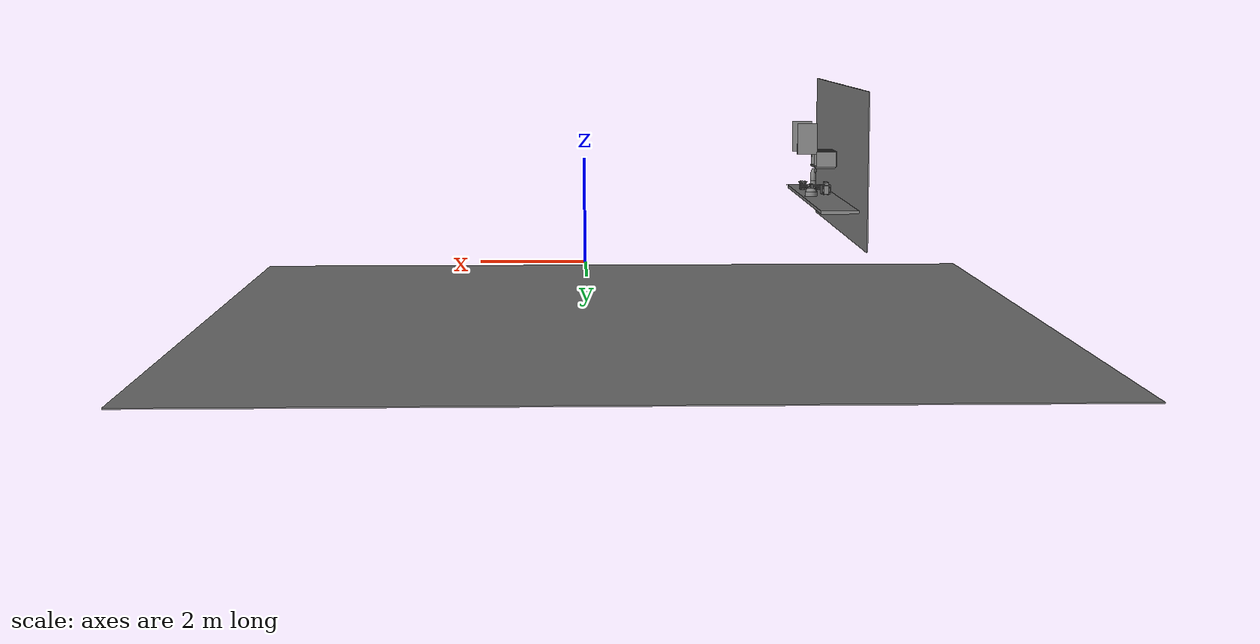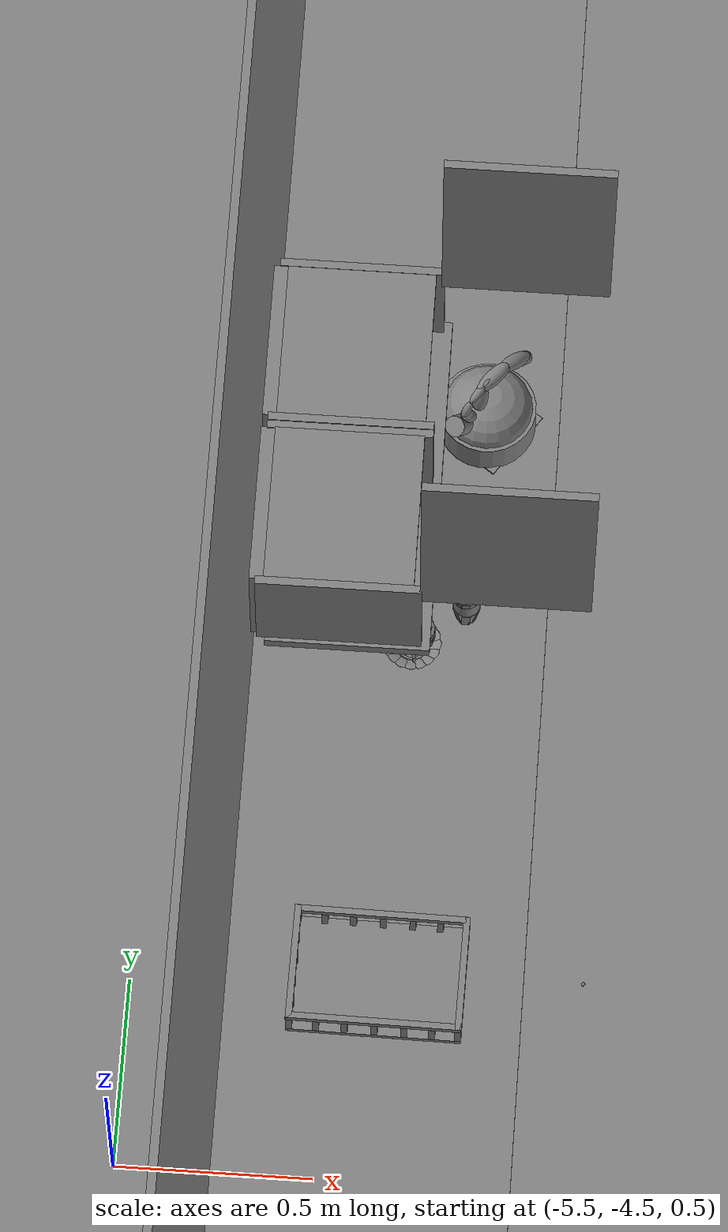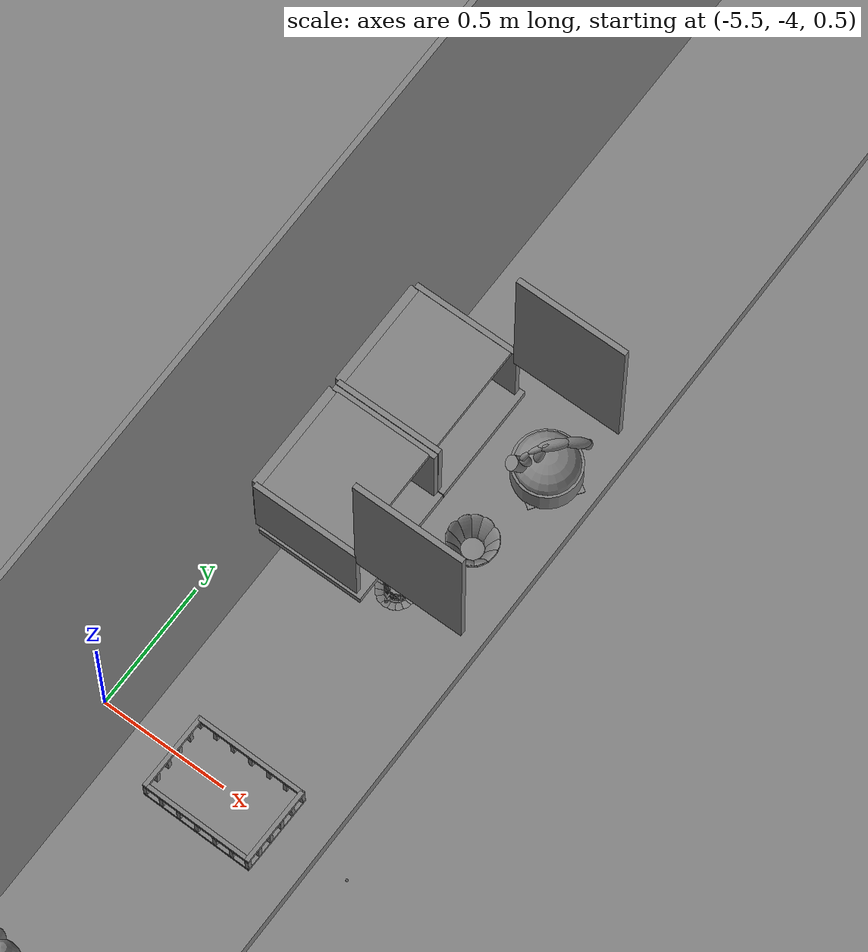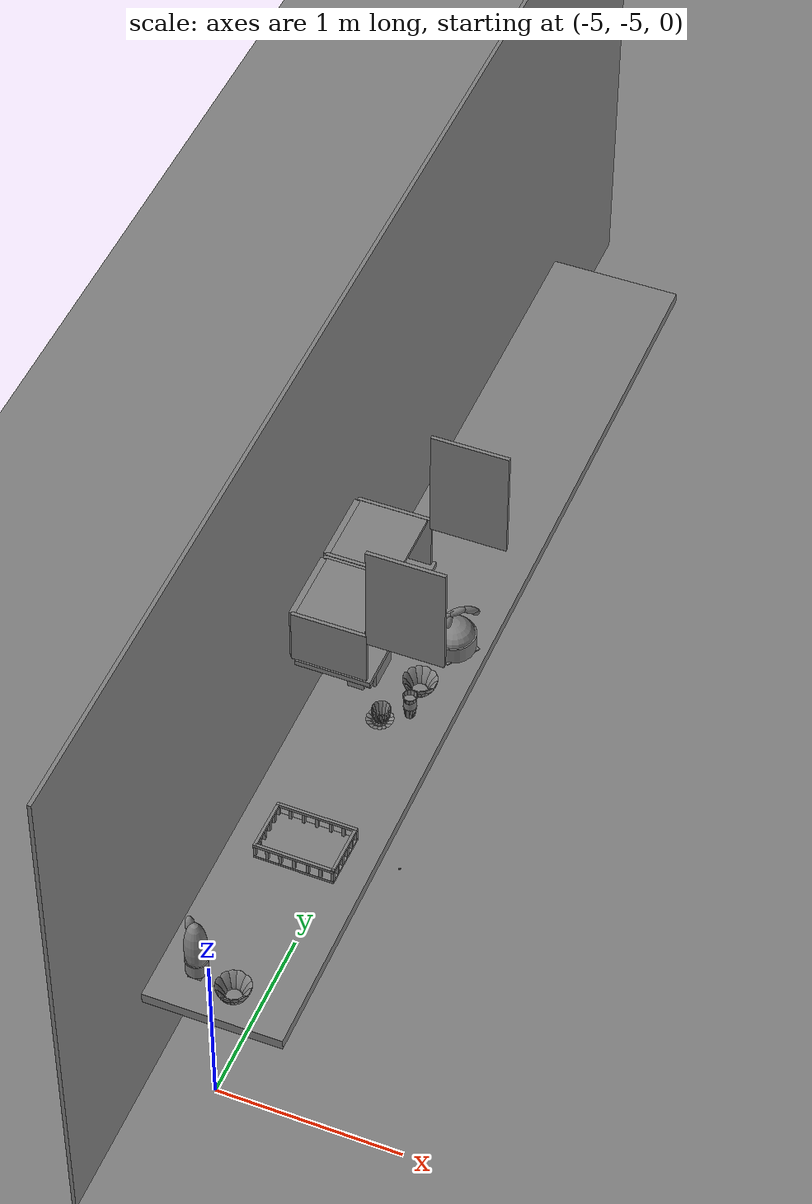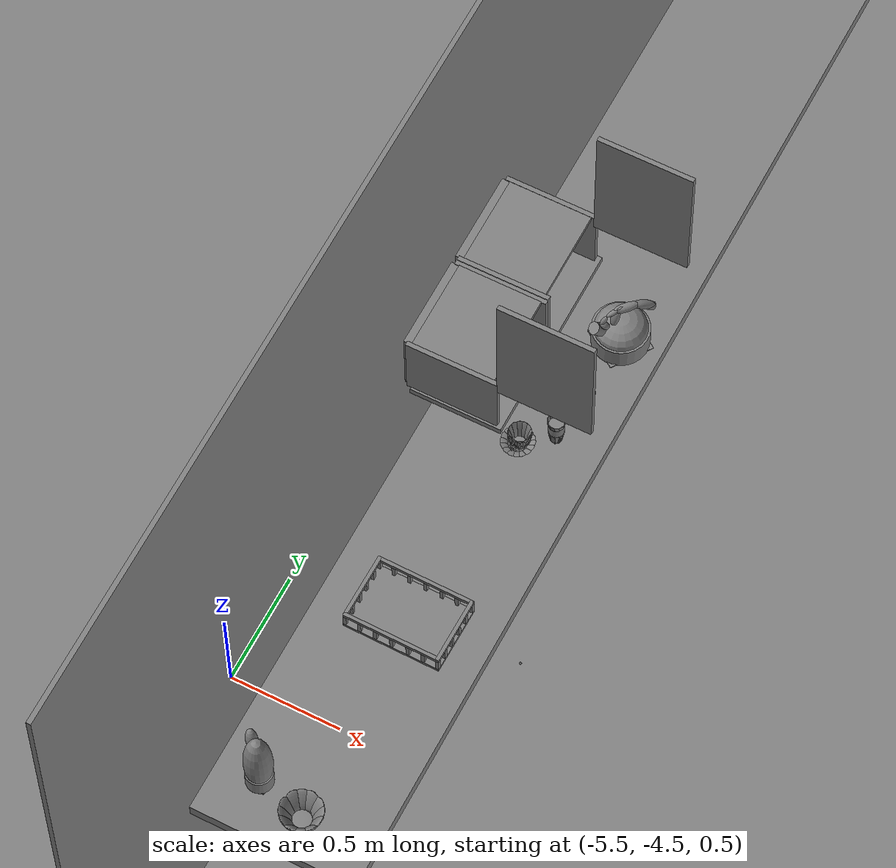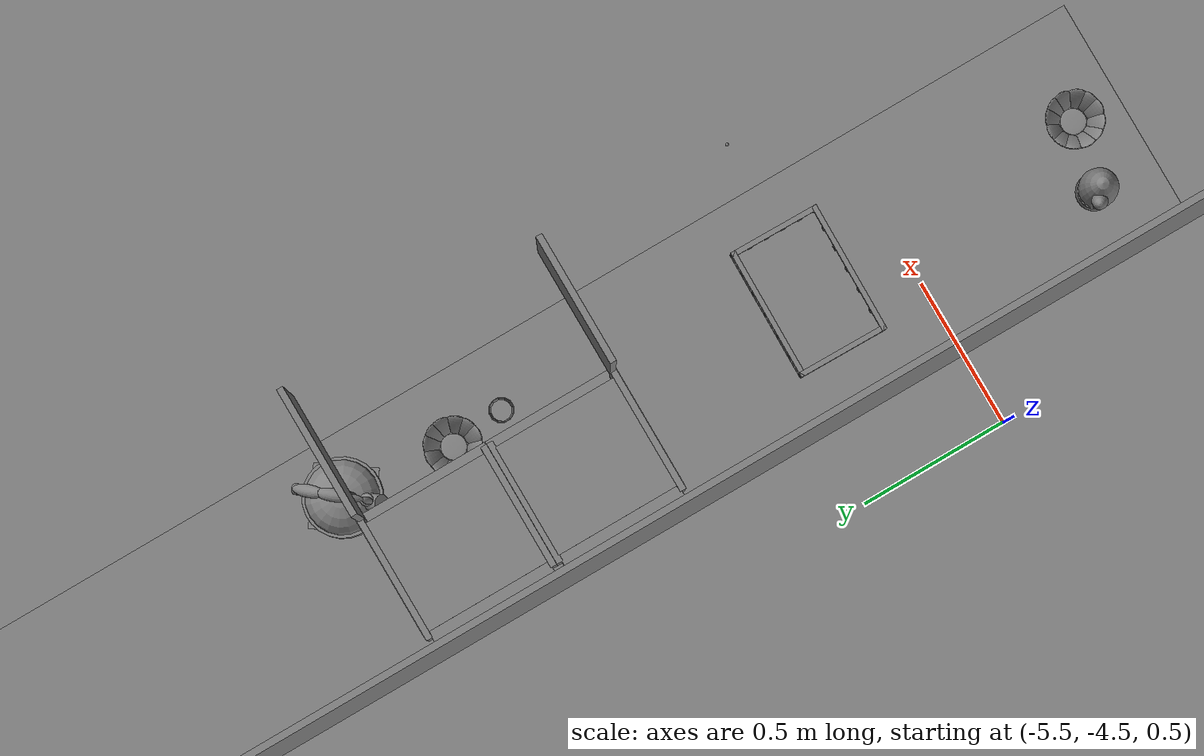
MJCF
<mujoco>
    <option gravity="0.000000000 0.000000000 -9.810000420" timestep="0.0049999999" integrator="implicitfast" density="9.8000002" viscosity="1.8000001e-05" noslip_iterations="10" iterations="100" sdf_iterations="50">
        <flag multiccd="disable"/>
    </option>
    <size memory="1000M"/>
    <compiler coordinate="local"/>
    <worldbody>
        <light cutoff="30" pos="0 1 1" dir="0 -1 -2"/>
        <light cutoff="30" pos="0 -1 1" dir="0 1 -2"/>
        <body pos="-4.860558510 -4.149443150 1.004824519" euler="0.000000000 0.000000000 -90.691093445" name="openloong_gripper_2f85_fix_base_usda_Basket_Kitchen_01">
            <geom contype="1" conaffinity="1" density="1000" type="box" material="" rgba="0.500000000 0.500000000 0.500000000 1.000000000" solimp="0.899999976 0.949999988 0.001000000" friction="1.000000000 0.005000000 0.000100000" solref="0.020000000 1.000000000" margin="0" condim="3" group="0" pos="0.086542509 0.207580954 0.047887992" quat="0.707107008 0.000000000 0.000000000 0.707106411" size="0.007600000 0.007600000 0.032000002" name="openloong_gripper_2f85_fix_base_usda_geom_12A32883_8B44_4B8B_A5A1_6C868352B18D"/>
            <geom contype="1" conaffinity="1" density="1000" type="box" material="" rgba="0.500000000 0.500000000 0.500000000 1.000000000" solimp="0.899999976 0.949999988 0.001000000" friction="1.000000000 0.005000000 0.000100000" solref="0.020000000 1.000000000" margin="0" condim="3" group="0" pos="-0.140816495 0.143605426 0.047889423" quat="0.707107008 0.000000000 0.000000000 0.707106411" size="0.007600000 0.007600000 0.032000002" name="openloong_gripper_2f85_fix_base_usda_geom_63930493_B412_4855_9265_0BDF377AFB1F"/>
            <geom contype="1" conaffinity="1" density="1000" type="box" material="" rgba="0.500000000 0.500000000 0.500000000 1.000000000" solimp="0.899999976 0.949999988 0.001000000" friction="1.000000000 0.005000000 0.000100000" solref="0.020000000 1.000000000" margin="0" condim="3" group="0" pos="-0.140816212 -0.070956804 0.047888946" quat="0.707107008 0.000000000 0.000000000 0.707106411" size="0.007600000 0.007600000 0.032000002" name="openloong_gripper_2f85_fix_base_usda_geom_F25A4E01_86A7_4A9A_A500_90C4EF3F2354"/>
            <geom contype="1" conaffinity="1" density="1000" type="box" material="" rgba="0.500000000 0.500000000 0.500000000 1.000000000" solimp="0.899999976 0.949999988 0.001000000" friction="1.000000000 0.005000000 0.000100000" solref="0.020000000 1.000000000" margin="0" condim="3" group="0" pos="0.140802577 0.207580566 0.047887899" quat="0.707107008 0.000000000 0.000000000 0.707106411" size="0.007600000 0.007600000 0.032000002" name="openloong_gripper_2f85_fix_base_usda_geom_09C7A568_E9ED_496C_8D17_5C9F386B1311"/>
            <geom contype="1" conaffinity="1" density="1000" type="box" material="" rgba="0.500000000 0.500000000 0.500000000 1.000000000" solimp="0.899999976 0.949999988 0.001000000" friction="1.000000000 0.005000000 0.000100000" solref="0.020000000 1.000000000" margin="0" condim="3" group="0" pos="0.086541750 -0.207636267 0.047888279" quat="0.707107008 0.000000000 0.000000000 0.707106411" size="0.007600000 0.007600000 0.032000002" name="openloong_gripper_2f85_fix_base_usda_geom_CAF0EAB3_90A1_4FC7_BE5A_6785FDB3E5D7"/>
            <geom contype="1" conaffinity="1" density="1000" type="box" material="" rgba="0.500000000 0.500000000 0.500000000 1.000000000" solimp="0.899999976 0.949999988 0.001000000" friction="1.000000000 0.005000000 0.000100000" solref="0.020000000 1.000000000" margin="0" condim="3" group="0" pos="0.140633777 -0.000001907 0.087263681" quat="0.707107008 0.000000000 0.000000000 0.707106411" size="0.215199992 0.008000000 0.008400000" name="openloong_gripper_2f85_fix_base_usda_geom_435E2E74_42FC_4A28_AC1D_6D70BB7D27ED"/>
            <geom contype="1" conaffinity="1" density="1000" type="box" material="" rgba="0.500000000 0.500000000 0.500000000 1.000000000" solimp="0.899999976 0.949999988 0.001000000" friction="1.000000000 0.005000000 0.000100000" solref="0.020000000 1.000000000" margin="0" condim="3" group="0" pos="-0.027960587 -0.207636639 0.047888566" quat="0.707107008 0.000000000 0.000000000 0.707106411" size="0.007600000 0.007600000 0.032000002" name="openloong_gripper_2f85_fix_base_usda_geom_7400A5B4_ED9D_4B3D_8BF1_B4D8148AC81F"/>
            <geom contype="1" conaffinity="1" density="1000" type="box" material="" rgba="0.500000000 0.500000000 0.500000000 1.000000000" solimp="0.899999976 0.949999988 0.001000000" friction="1.000000000 0.005000000 0.000100000" solref="0.020000000 1.000000000" margin="0" condim="3" group="0" pos="-0.140816122 -0.141625211 0.047888853" quat="0.707107008 0.000000000 0.000000000 0.707106411" size="0.007600000 0.007600000 0.032000002" name="openloong_gripper_2f85_fix_base_usda_geom_373EF4BF_BABB_4A12_97C2_655FD5EF310F"/>
            <geom contype="1" conaffinity="1" density="1000" type="box" material="" rgba="0.500000000 0.500000000 0.500000000 1.000000000" solimp="0.899999976 0.949999988 0.001000000" friction="1.000000000 0.005000000 0.000100000" solref="0.020000000 1.000000000" margin="0" condim="3" group="0" pos="-0.140816122 0.207580194 0.047888756" quat="0.707107008 0.000000000 0.000000000 0.707106411" size="0.007600000 0.007600000 0.032000002" name="openloong_gripper_2f85_fix_base_usda_geom_5C7BD72C_9CB8_4E68_B39D_E1A9ED727752"/>
            <geom contype="1" conaffinity="1" density="1000" type="box" material="" rgba="0.500000000 0.500000000 0.500000000 1.000000000" solimp="0.899999976 0.949999988 0.001000000" friction="1.000000000 0.005000000 0.000100000" solref="0.020000000 1.000000000" margin="0" condim="3" group="0" pos="0.140800864 -0.070956804 0.047888376" quat="0.707107008 0.000000000 0.000000000 0.707106411" size="0.007600000 0.007600000 0.032000002" name="openloong_gripper_2f85_fix_base_usda_geom_45A4381E_18F8_4067_8BFE_0596A471EF90"/>
            <geom contype="1" conaffinity="1" density="1000" type="box" material="" rgba="0.500000000 0.500000000 0.500000000 1.000000000" solimp="0.899999976 0.949999988 0.001000000" friction="1.000000000 0.005000000 0.000100000" solref="0.020000000 1.000000000" margin="0" condim="3" group="0" pos="0.140800476 0.002393341 0.047888376" quat="0.707107008 0.000000000 0.000000000 0.707106411" size="0.007600000 0.007600000 0.032000002" name="openloong_gripper_2f85_fix_base_usda_geom_58A72B76_1EA1_4F6D_88F1_453A6100F9CB"/>
            <geom contype="1" conaffinity="1" density="1000" type="box" material="" rgba="0.500000000 0.500000000 0.500000000 1.000000000" solimp="0.899999976 0.949999988 0.001000000" friction="1.000000000 0.005000000 0.000100000" solref="0.020000000 1.000000000" margin="0" condim="3" group="0" pos="-0.140543848 -0.000001526 0.087263964" quat="0.707107008 0.000000000 0.000000000 0.707106411" size="0.215199992 0.008000000 0.008400000" name="openloong_gripper_2f85_fix_base_usda_geom_38186304_46FD_4933_91BE_C99099B4CC01"/>
            <geom contype="1" conaffinity="1" density="1000" type="box" material="" rgba="0.500000000 0.500000000 0.500000000 1.000000000" solimp="0.899999976 0.949999988 0.001000000" friction="1.000000000 0.005000000 0.000100000" solref="0.020000000 1.000000000" margin="0" condim="3" group="0" pos="-0.140816018 0.075380705 0.047889233" quat="0.707107008 0.000000000 0.000000000 0.707106411" size="0.007600000 0.007600000 0.032000002" name="openloong_gripper_2f85_fix_base_usda_geom_9D32B5AB_B2C4_4DE7_A993_C4F9FD54BBC1"/>
            <geom contype="1" conaffinity="1" density="1000" type="box" material="" rgba="0.500000000 0.500000000 0.500000000 1.000000000" solimp="0.899999976 0.949999988 0.001000000" friction="1.000000000 0.005000000 0.000100000" solref="0.020000000 1.000000000" margin="0" condim="3" group="0" pos="0.140801147 -0.141625211 0.047888279" quat="0.707107008 0.000000000 0.000000000 0.707106411" size="0.007600000 0.007600000 0.032000002" name="openloong_gripper_2f85_fix_base_usda_geom_390280C0_222B_42FE_A69A_DC509D49C8A4"/>
            <geom contype="1" conaffinity="1" density="1000" type="box" material="" rgba="0.500000000 0.500000000 0.500000000 1.000000000" solimp="0.899999976 0.949999988 0.001000000" friction="1.000000000 0.005000000 0.000100000" solref="0.020000000 1.000000000" margin="0" condim="3" group="0" pos="0.000000000 -0.207717523 0.087263964" quat="0.707107008 0.000000000 0.000000000 0.707106411" size="0.008000000 0.148000002 0.008400000" name="openloong_gripper_2f85_fix_base_usda_geom_DE446CB0_862E_499F_BE43_8CEDD485A3FF"/>
            <geom contype="1" conaffinity="1" density="1000" type="box" material="" rgba="0.500000000 0.500000000 0.500000000 1.000000000" solimp="0.899999976 0.949999988 0.001000000" friction="1.000000000 0.005000000 0.000100000" solref="0.020000000 1.000000000" margin="0" condim="3" group="0" pos="0.029044246 -0.207635880 0.047888376" quat="0.707107008 0.000000000 0.000000000 0.707106411" size="0.007600000 0.007600000 0.032000002" name="openloong_gripper_2f85_fix_base_usda_geom_BB39EC49_1179_4509_9495_3EAD915B87DD"/>
            <geom contype="1" conaffinity="1" density="1000" type="box" material="" rgba="0.500000000 0.500000000 0.500000000 1.000000000" solimp="0.899999976 0.949999988 0.001000000" friction="1.000000000 0.005000000 0.000100000" solref="0.020000000 1.000000000" margin="0" condim="3" group="0" pos="0.140800476 0.075379565 0.047888566" quat="0.707107008 0.000000000 0.000000000 0.707106411" size="0.007600000 0.007600000 0.032000002" name="openloong_gripper_2f85_fix_base_usda_geom_C6A9429A_16AF_4060_9A42_BF33B4B448C3"/>
            <geom contype="1" conaffinity="1" density="1000" type="box" material="" rgba="0.500000000 0.500000000 0.500000000 1.000000000" solimp="0.899999976 0.949999988 0.001000000" friction="1.000000000 0.005000000 0.000100000" solref="0.020000000 1.000000000" margin="0" condim="3" group="0" pos="-0.027959539 0.207580566 0.047888376" quat="0.707107008 0.000000000 0.000000000 0.707106411" size="0.007600000 0.007600000 0.032000002" name="openloong_gripper_2f85_fix_base_usda_geom_DE651267_698F_4451_931A_C6927C10C318"/>
            <geom contype="1" conaffinity="1" density="1000" type="box" material="" rgba="0.500000000 0.500000000 0.500000000 1.000000000" solimp="0.899999976 0.949999988 0.001000000" friction="1.000000000 0.005000000 0.000100000" solref="0.020000000 1.000000000" margin="0" condim="3" group="0" pos="0.140799999 0.143604279 0.047888756" quat="0.707107008 0.000000000 0.000000000 0.707106411" size="0.007600000 0.007600000 0.032000002" name="openloong_gripper_2f85_fix_base_usda_geom_6DF216A2_E593_4839_9F40_887283331F4D"/>
            <geom contype="1" conaffinity="1" density="1000" type="box" material="" rgba="0.500000000 0.500000000 0.500000000 1.000000000" solimp="0.899999976 0.949999988 0.001000000" friction="1.000000000 0.005000000 0.000100000" solref="0.020000000 1.000000000" margin="0" condim="3" group="0" pos="-0.140816122 0.002393723 0.047889233" quat="0.707107008 0.000000000 0.000000000 0.707106411" size="0.007600000 0.007600000 0.032000002" name="openloong_gripper_2f85_fix_base_usda_geom_C967B220_D97A_4136_8D97_A4A89900F4A8"/>
            <geom contype="1" conaffinity="1" density="1000" type="box" material="" rgba="0.500000000 0.500000000 0.500000000 1.000000000" solimp="0.899999976 0.949999988 0.001000000" friction="1.000000000 0.005000000 0.000100000" solref="0.020000000 1.000000000" margin="0" condim="3" group="0" pos="-0.085476689 0.207580194 0.047888566" quat="0.707107008 0.000000000 0.000000000 0.707106411" size="0.007600000 0.007600000 0.032000002" name="openloong_gripper_2f85_fix_base_usda_geom_A4B42BF9_FA7B_4B96_8AEC_7E01E034A5FE"/>
            <geom contype="1" conaffinity="1" density="1000" type="box" material="" rgba="0.500000000 0.500000000 0.500000000 1.000000000" solimp="0.899999976 0.949999988 0.001000000" friction="1.000000000 0.005000000 0.000100000" solref="0.020000000 1.000000000" margin="0" condim="3" group="0" pos="0.000000000 0.207718283 0.087263964" quat="0.707107008 0.000000000 0.000000000 0.707106411" size="0.008000000 0.148000002 0.008400000" name="openloong_gripper_2f85_fix_base_usda_geom_266232AC_F4FF_407A_8D55_E17B9D31AD1C"/>
            <geom contype="1" conaffinity="1" density="1000" type="box" material="" rgba="0.500000000 0.500000000 0.500000000 1.000000000" solimp="0.899999976 0.949999988 0.001000000" friction="1.000000000 0.005000000 0.000100000" solref="0.020000000 1.000000000" margin="0" condim="3" group="0" pos="0.029045582 0.207581714 0.047888279" quat="0.707107008 0.000000000 0.000000000 0.707106411" size="0.007600000 0.007600000 0.032000002" name="openloong_gripper_2f85_fix_base_usda_geom_5D382D39_71D7_4B56_9BAD_884028F649BF"/>
            <geom contype="1" conaffinity="1" density="1000" type="box" material="" rgba="0.500000000 0.500000000 0.500000000 1.000000000" solimp="0.899999976 0.949999988 0.001000000" friction="1.000000000 0.005000000 0.000100000" solref="0.020000000 1.000000000" margin="0" condim="3" group="0" pos="-0.140816122 -0.207636267 0.047888853" quat="0.707107008 0.000000000 0.000000000 0.707106411" size="0.007600000 0.007600000 0.032000002" name="openloong_gripper_2f85_fix_base_usda_geom_9B8BA4AE_200D_4407_9F44_9C2227EE6F0C"/>
            <geom contype="1" conaffinity="1" density="1000" type="box" material="" rgba="0.500000000 0.500000000 0.500000000 1.000000000" solimp="0.899999976 0.949999988 0.001000000" friction="1.000000000 0.005000000 0.000100000" solref="0.020000000 1.000000000" margin="0" condim="3" group="0" pos="-0.085477069 -0.207636639 0.047888756" quat="0.707107008 0.000000000 0.000000000 0.707106411" size="0.007600000 0.007600000 0.032000002" name="openloong_gripper_2f85_fix_base_usda_geom_8878ED50_46FF_4B32_8DC4_5494466CD509"/>
            <geom contype="1" conaffinity="1" density="1000" type="box" material="" rgba="0.500000000 0.500000000 0.500000000 1.000000000" solimp="0.899999976 0.949999988 0.001000000" friction="1.000000000 0.005000000 0.000100000" solref="0.020000000 1.000000000" margin="0" condim="3" group="0" pos="-0.000012112 0.000000381 0.008534336" quat="0.707107008 0.000000000 0.000000000 0.707106411" size="0.215199992 0.148800001 0.008400000" name="openloong_gripper_2f85_fix_base_usda_geom_333430B4_5BC4_4D23_98EC_35CA8A3EAA51"/>
            <geom contype="1" conaffinity="1" density="1000" type="box" material="" rgba="0.500000000 0.500000000 0.500000000 1.000000000" solimp="0.899999976 0.949999988 0.001000000" friction="1.000000000 0.005000000 0.000100000" solref="0.020000000 1.000000000" margin="0" condim="3" group="0" pos="0.140801623 -0.207636267 0.047888186" quat="0.707107008 0.000000000 0.000000000 0.707106411" size="0.007600000 0.007600000 0.032000002" name="openloong_gripper_2f85_fix_base_usda_geom_1E35F3C8_ED43_46EE_9FAD_229E877F95F3"/>
            <freejoint name="openloong_gripper_2f85_fix_base_usda_Basket_Kitchen_01_joint"/>
            <site size="0.005000000 0.005000000 0.005000000" rgba="0.500000000 0.500000000 0.500000000 1.000000000" pos="0.000000000 0.000000000 0.000000000" quat="1.000000000 0.000000000 0.000000000 0.000000000" group="0" type="sphere" name="openloong_gripper_2f85_fix_base_usda_Basket_Kitchen_01site"/>
        </body>
        <body pos="-4.721817970 -2.990536690 1.027358174" euler="0.000000000 0.000000000 89.999946594" name="Interactive Objcets_bow_02">
            <geom contype="1" conaffinity="1" density="1000" type="ellipsoid" material="" rgba="0.500000000 0.500000000 0.500000000 1.000000000" solimp="0.899999976 0.949999988 0.001000000" friction="1.000000000 0.005000000 0.000100000" solref="0.020000000 1.000000000" margin="0" condim="3" group="0" pos="-0.058925860 -0.029528141 0.044118762" quat="0.223252773 0.231952101 0.054787740 -0.945174515" size="0.010000000 0.039999999 0.052000001" name="Interactive Objcets_geom_107205E9_DDDE_461B_A5BA_9498A371CA92"/>
            <geom contype="1" conaffinity="1" density="1000" type="ellipsoid" material="" rgba="0.500000000 0.500000000 0.500000000 1.000000000" solimp="0.899999976 0.949999988 0.001000000" friction="1.000000000 0.005000000 0.000100000" solref="0.020000000 1.000000000" margin="0" condim="3" group="0" pos="0.000082973 0.000000000 0.000446677" quat="1.000000000 0.000000000 0.000000000 0.000000000" size="0.039999999 0.039999999 0.002000000" name="Interactive Objcets_geom_A87F2B45_51CD_46CB_B72A_FBCBC9A549BC"/>
            <geom contype="1" conaffinity="1" density="1000" type="ellipsoid" material="" rgba="0.500000000 0.500000000 0.500000000 1.000000000" solimp="0.899999976 0.949999988 0.001000000" friction="1.000000000 0.005000000 0.000100000" solref="0.020000000 1.000000000" margin="0" condim="3" group="0" pos="0.029448029 -0.059084892 0.044118762" quat="0.825555801 0.125530601 0.202597082 -0.511521280" size="0.010000000 0.039999999 0.052000001" name="Interactive Objcets_geom_73D2CA58_51B3_4552_AF2C_07DFC3FDDD8E"/>
            <geom contype="1" conaffinity="1" density="1000" type="ellipsoid" material="" rgba="0.500000000 0.500000000 0.500000000 1.000000000" solimp="0.899999976 0.949999988 0.001000000" friction="1.000000000 0.005000000 0.000100000" solref="0.020000000 1.000000000" margin="0" condim="3" group="0" pos="0.000082973 0.000000000 0.005656481" quat="1.000000000 0.000000000 0.000000000 0.000000000" size="0.039999999 0.039999999 0.002000000" name="Interactive Objcets_geom_33674AC1_D4C8_4B8D_A9C7_29F366C04272"/>
            <geom contype="1" conaffinity="1" density="1000" type="ellipsoid" material="" rgba="0.500000000 0.500000000 0.500000000 1.000000000" solimp="0.899999976 0.949999988 0.001000000" friction="1.000000000 0.005000000 0.000100000" solref="0.020000000 1.000000000" margin="0" condim="3" group="0" pos="-0.040080305 -0.052354336 0.044118762" quat="0.429593205 0.213749886 0.105425082 -0.871003032" size="0.010000000 0.039999999 0.052000001" name="Interactive Objcets_geom_561E3273_E88D_46D2_B293_34FC615FFE64"/>
            <geom contype="1" conaffinity="1" density="1000" type="ellipsoid" material="" rgba="0.500000000 0.500000000 0.500000000 1.000000000" solimp="0.899999976 0.949999988 0.001000000" friction="1.000000000 0.005000000 0.000100000" solref="0.020000000 1.000000000" margin="0" condim="3" group="0" pos="-0.065898418 -0.000007629 0.044118762" quat="0.971183062 -0.000000142 -0.238334835 0.000000030" size="0.010000000 0.039999999 0.052000001" name="Interactive Objcets_geom_363731CC_FD6E_442E_A3DE_C3ABFC13ED0B"/>
            <geom contype="1" conaffinity="1" density="1000" type="ellipsoid" material="" rgba="0.500000000 0.500000000 0.500000000 1.000000000" solimp="0.899999976 0.949999988 0.001000000" friction="1.000000000 0.005000000 0.000100000" solref="0.020000000 1.000000000" margin="0" condim="3" group="0" pos="0.059080135 0.029512405 0.044118762" quat="0.223252743 -0.231952220 -0.054787420 -0.945174456" size="0.010000000 0.039999999 0.052000001" name="Interactive Objcets_geom_578D97A3_A48D_496A_8CB8_18638048C821"/>
            <geom contype="1" conaffinity="1" density="1000" type="ellipsoid" material="" rgba="0.500000000 0.500000000 0.500000000 1.000000000" solimp="0.899999976 0.949999988 0.001000000" friction="1.000000000 0.005000000 0.000100000" solref="0.020000000 1.000000000" margin="0" condim="3" group="0" pos="0.066052437 -0.000007629 0.044118762" quat="0.971183062 -0.000000156 0.238334835 0.000000030" size="0.010000000 0.039999999 0.052000001" name="Interactive Objcets_geom_A0C0F7F1_A91D_40D3_8500_E2C1F7646A32"/>
            <geom contype="1" conaffinity="1" density="1000" type="ellipsoid" material="" rgba="0.500000000 0.500000000 0.500000000 1.000000000" solimp="0.899999976 0.949999988 0.001000000" friction="1.000000000 0.005000000 0.000100000" solref="0.020000000 1.000000000" margin="0" condim="3" group="0" pos="0.000243668 -0.065982819 0.044118762" quat="0.687598705 0.168314636 0.168741375 -0.685860336" size="0.010000000 0.039999999 0.052000001" name="Interactive Objcets_geom_7C94F1DD_A7ED_4CF1_9716_4BB04964DFC9"/>
            <geom contype="1" conaffinity="1" density="1000" type="ellipsoid" material="" rgba="0.500000000 0.500000000 0.500000000 1.000000000" solimp="0.899999976 0.949999988 0.001000000" friction="1.000000000 0.005000000 0.000100000" solref="0.020000000 1.000000000" margin="0" condim="3" group="0" pos="-0.000090118 0.065967560 0.044118762" quat="0.687598705 -0.168314859 -0.168741152 -0.685860336" size="0.010000000 0.039999999 0.052000001" name="Interactive Objcets_geom_B23BA93C_F3F6_435E_A4FD_15306C86C58E"/>
            <geom contype="1" conaffinity="1" density="1000" type="ellipsoid" material="" rgba="0.500000000 0.500000000 0.500000000 1.000000000" solimp="0.899999976 0.949999988 0.001000000" friction="1.000000000 0.005000000 0.000100000" solref="0.020000000 1.000000000" margin="0" condim="3" group="0" pos="0.052321676 -0.040297508 0.044118762" quat="0.919264674 0.076882742 0.225593731 -0.313287675" size="0.010000000 0.039999999 0.052000001" name="Interactive Objcets_geom_C5D1237E_EAA0_4BE5_BF2B_DFD218DE26F7"/>
            <geom contype="1" conaffinity="1" density="1000" type="ellipsoid" material="" rgba="0.500000000 0.500000000 0.500000000 1.000000000" solimp="0.899999976 0.949999988 0.001000000" friction="1.000000000 0.005000000 0.000100000" solref="0.020000000 1.000000000" margin="0" condim="3" group="0" pos="0.040234569 0.052338600 0.044118762" quat="0.429593176 -0.213750035 -0.105424814 -0.871002913" size="0.010000000 0.039999999 0.052000001" name="Interactive Objcets_geom_25D9A045_2C83_4E25_AD7B_844782EB8DD8"/>
            <geom contype="1" conaffinity="1" density="1000" type="ellipsoid" material="" rgba="0.500000000 0.500000000 0.500000000 1.000000000" solimp="0.899999976 0.949999988 0.001000000" friction="1.000000000 0.005000000 0.000100000" solref="0.020000000 1.000000000" margin="0" condim="3" group="0" pos="-0.052167647 0.040282249 0.044118762" quat="0.919264615 -0.076883025 -0.225593641 -0.313287735" size="0.010000000 0.039999999 0.052000001" name="Interactive Objcets_geom_51499B9F_E935_4C58_8B89_6AFE2F3679BF"/>
            <geom contype="1" conaffinity="1" density="1000" type="ellipsoid" material="" rgba="0.500000000 0.500000000 0.500000000 1.000000000" solimp="0.899999976 0.949999988 0.001000000" friction="1.000000000 0.005000000 0.000100000" solref="0.020000000 1.000000000" margin="0" condim="3" group="0" pos="-0.029293532 0.059069633 0.044118762" quat="0.825555801 -0.125530809 -0.202596903 -0.511521280" size="0.010000000 0.039999999 0.052000001" name="Interactive Objcets_geom_35C6A0B4_A4C8_418D_8C68_C32F57AC73EE"/>
            <freejoint name="Interactive Objcets_bow_02"/>
        </body>
        <body pos="-4.802892208 -3.488179445 1.876015186" euler="89.999992371 -89.999946594 0.000000000" name="Interactive Objcets_guimen_01">
            <geom contype="1" conaffinity="1" density="1000" type="box" material="" rgba="0.500000000 0.500000000 0.500000000 1.000000000" solimp="0.899999976 0.949999988 0.001000000" friction="1.000000000 0.005000000 0.000100000" solref="0.020000000 1.000000000" margin="0" condim="3" group="0" pos="0.006727934 0.314709902 -0.203009605" quat="1.000000000 0.000000119 -0.000000119 0.000000000" size="0.010000000 0.317999989 0.204999998" name="Interactive Objcets_geom_E5F5EC4D_0F36_47E8_B819_ABE51C3057E0"/>
            <joint armature="0" stiffness="0" damping="1" axis="0.000000 1.000000 0.000000" type="hinge" name="Interactive Objcets_guimen_01"/>
        </body>
        <body pos="-4.827295780 -3.287638187 1.074643731" euler="0.000000000 0.000000000 89.999992371" name="Interactive Objcets_coffeecup_01">
            <geom contype="1" conaffinity="1" density="1000" type="ellipsoid" material="" rgba="0.500000000 0.500000000 0.500000000 1.000000000" solimp="0.899999976 0.949999988 0.001000000" friction="1.000000000 0.005000000 0.000100000" solref="0.020000000 1.000000000" margin="0" condim="3" group="0" pos="0.053700209 0.033117294 0.002976775" quat="0.496025741 -0.082236379 -0.047260769 -0.863111615" size="0.005000000 0.029999999 0.048999999" name="Interactive Objcets_geom_FE0FC6F1_72E7_4903_8100_D6F318A41CF1"/>
            <geom contype="1" conaffinity="1" density="1000" type="ellipsoid" material="" rgba="0.500000000 0.500000000 0.500000000 1.000000000" solimp="0.899999976 0.949999988 0.001000000" friction="1.000000000 0.005000000 0.000100000" solref="0.020000000 1.000000000" margin="0" condim="3" group="0" pos="0.068445444 0.017385960 0.002976775" quat="0.228377223 -0.092319682 -0.021759447 -0.968941331" size="0.005000000 0.029999999 0.048999999" name="Interactive Objcets_geom_05535392_755B_48B4_AB14_8DADD3569EE7"/>
            <geom contype="1" conaffinity="1" density="1000" type="capsule" material="" rgba="0.500000000 0.500000000 0.500000000 1.000000000" solimp="0.899999976 0.949999988 0.001000000" friction="1.000000000 0.005000000 0.000100000" solref="0.020000000 1.000000000" margin="0" condim="3" group="0" pos="-0.030251026 0.000000000 0.004966617" quat="0.480583906 -0.000000000 0.876948774 -0.000000126" size="0.004000000 0.005000000 1.000000000" name="Interactive Objcets_geom_6B567840_DCA8_477E_BFAC_2DE505186FF9"/>
            <geom contype="1" conaffinity="1" density="1000" type="ellipsoid" material="" rgba="0.500000000 0.500000000 0.500000000 1.000000000" solimp="0.899999976 0.949999988 0.001000000" friction="1.000000000 0.005000000 0.000100000" solref="0.020000000 1.000000000" margin="0" condim="3" group="0" pos="0.034471050 -0.037125111 0.002976775" quat="0.701517045 0.067293778 0.066836871 -0.706313014" size="0.005000000 0.029999999 0.048999999" name="Interactive Objcets_geom_95B8AA4F_2FC3_462C_8DA3_735B9F6DD166"/>
            <geom contype="1" conaffinity="1" density="1000" type="ellipsoid" material="" rgba="0.500000000 0.500000000 0.500000000 1.000000000" solimp="0.899999976 0.949999988 0.001000000" friction="1.000000000 0.005000000 0.000100000" solref="0.020000000 1.000000000" margin="0" condim="3" group="0" pos="0.035336256 0.000558376 -0.045152068" quat="0.999999881 0.000000000 0.000000000 0.000000000" size="0.029999999 0.029999999 0.001000000" name="Interactive Objcets_geom_13F76DF8_60E4_4D57_A33C_AA02DF1F107F"/>
            <geom contype="1" conaffinity="1" density="1000" type="capsule" material="" rgba="0.500000000 0.500000000 0.500000000 1.000000000" solimp="0.899999976 0.949999988 0.001000000" friction="1.000000000 0.005000000 0.000100000" solref="0.020000000 1.000000000" margin="0" condim="3" group="0" pos="-0.021276474 0.000000000 0.038509369" quat="0.633189917 0.000000000 0.773996413 0.000000000" size="0.004000000 0.009000000 1.000000000" name="Interactive Objcets_geom_28CFC1D3_08F3_4ED3_B6F8_8BD6438EA510"/>
            <geom contype="1" conaffinity="1" density="1000" type="capsule" material="" rgba="0.500000000 0.500000000 0.500000000 1.000000000" solimp="0.899999976 0.949999988 0.001000000" friction="1.000000000 0.005000000 0.000100000" solref="0.020000000 1.000000000" margin="0" condim="3" group="0" pos="-0.018014431 0.000000000 0.001762271" quat="0.707106769 -0.000000004 0.707106709 -0.000000088" size="0.004000000 0.005000000 1.000000000" name="Interactive Objcets_geom_760E3BD7_2766_4F4A_BC15_6E1489F45546"/>
            <geom contype="1" conaffinity="1" density="1000" type="ellipsoid" material="" rgba="0.500000000 0.500000000 0.500000000 1.000000000" solimp="0.899999976 0.949999988 0.001000000" friction="1.000000000 0.005000000 0.000100000" solref="0.020000000 1.000000000" margin="0" condim="3" group="0" pos="0.001010895 -0.016271591 0.002976775" quat="0.228377163 0.092315644 0.021758538 -0.968941689" size="0.005000000 0.029999999 0.048999999" name="Interactive Objcets_geom_33E35217_43D3_4F5E_B4AF_078A375722C6"/>
            <geom contype="1" conaffinity="1" density="1000" type="capsule" material="" rgba="0.500000000 0.500000000 0.500000000 1.000000000" solimp="0.899999976 0.949999988 0.001000000" friction="1.000000000 0.005000000 0.000100000" solref="0.020000000 1.000000000" margin="0" condim="3" group="0" pos="-0.008219719 0.000000000 -0.000944734" quat="0.364379913 0.000000063 0.931250274 -0.000000063" size="0.004000000 0.003000000 1.000000000" name="Interactive Objcets_geom_A18345CD_D4B9_4AA2_826D_22F1048FA679"/>
            <geom contype="1" conaffinity="1" density="1000" type="ellipsoid" material="" rgba="0.500000000 0.500000000 0.500000000 1.000000000" solimp="0.899999976 0.949999988 0.001000000" friction="1.000000000 0.005000000 0.000100000" solref="0.020000000 1.000000000" margin="0" condim="3" group="0" pos="0.002039194 0.019308567 0.002976775" quat="0.961933970 -0.024419386 -0.091652036 -0.256293654" size="0.005000000 0.029999999 0.048999999" name="Interactive Objcets_geom_A448006D_788A_43BA_B859_C1158AC7CDC2"/>
            <geom contype="1" conaffinity="1" density="1000" type="capsule" material="" rgba="0.500000000 0.500000000 0.500000000 1.000000000" solimp="0.899999976 0.949999988 0.001000000" friction="1.000000000 0.005000000 0.000100000" solref="0.020000000 1.000000000" margin="0" condim="3" group="0" pos="-0.033022881 0.000000000 0.037873149" quat="0.874267220 0.000000042 0.485444903 -0.000000084" size="0.004000000 0.004000000 1.000000000" name="Interactive Objcets_geom_4C7DDB84_914F_471B_B160_FB27A9E8C8DA"/>
            <geom contype="1" conaffinity="1" density="1000" type="ellipsoid" material="" rgba="0.500000000 0.500000000 0.500000000 1.000000000" solimp="0.899999976 0.949999988 0.001000000" friction="1.000000000 0.005000000 0.000100000" solref="0.020000000 1.000000000" margin="0" condim="3" group="0" pos="0.034984604 0.038240910 0.002976775" quat="0.701516926 -0.067296736 -0.066839755 -0.706312656" size="0.005000000 0.029999999 0.048999999" name="Interactive Objcets_geom_C6EFCDD5_0445_4F85_9262_80ED11EF4A59"/>
            <geom contype="1" conaffinity="1" density="1000" type="ellipsoid" material="" rgba="0.500000000 0.500000000 0.500000000 1.000000000" solimp="0.899999976 0.949999988 0.001000000" friction="1.000000000 0.005000000 0.000100000" solref="0.020000000 1.000000000" margin="0" condim="3" group="0" pos="-0.002956629 0.000558376 0.002976775" quat="0.995491505 0.000000004 -0.094849378 -0.000000089" size="0.005000000 0.029999999 0.048999999" name="Interactive Objcets_geom_4CF1FD23_0B5D_46DE_A7E0_AF84549DFA24"/>
            <geom contype="1" conaffinity="1" density="1000" type="ellipsoid" material="" rgba="0.500000000 0.500000000 0.500000000 1.000000000" solimp="0.899999976 0.949999988 0.001000000" friction="1.000000000 0.005000000 0.000100000" solref="0.020000000 1.000000000" margin="0" condim="3" group="0" pos="0.017669693 0.034160614 0.002976775" quat="0.848410904 -0.049618516 -0.080835648 -0.520770907" size="0.005000000 0.029999999 0.048999999" name="Interactive Objcets_geom_C47A4D23_05EB_4FE3_9807_0DD7991831DA"/>
            <geom contype="1" conaffinity="1" density="1000" type="ellipsoid" material="" rgba="0.500000000 0.500000000 0.500000000 1.000000000" solimp="0.899999976 0.949999988 0.001000000" friction="1.000000000 0.005000000 0.000100000" solref="0.020000000 1.000000000" margin="0" condim="3" group="0" pos="0.051787138 -0.033043861 0.002976775" quat="0.848411202 0.049616337 0.080832161 -0.520771146" size="0.005000000 0.029999999 0.048999999" name="Interactive Objcets_geom_5F42288D_6E56_4CEF_886B_9F0A970B46FA"/>
            <geom contype="1" conaffinity="1" density="1000" type="ellipsoid" material="" rgba="0.500000000 0.500000000 0.500000000 1.000000000" solimp="0.899999976 0.949999988 0.001000000" friction="1.000000000 0.005000000 0.000100000" solref="0.020000000 1.000000000" margin="0" condim="3" group="0" pos="0.035336256 0.000558376 -0.043215394" quat="0.999999881 0.000000000 0.000000000 0.000000000" size="0.029999999 0.029999999 0.001000000" name="Interactive Objcets_geom_C0ED7CE8_2A42_46CA_8987_A47B15F1738D"/>
            <geom contype="1" conaffinity="1" density="1000" type="capsule" material="" rgba="0.500000000 0.500000000 0.500000000 1.000000000" solimp="0.899999976 0.949999988 0.001000000" friction="1.000000000 0.005000000 0.000100000" solref="0.020000000 1.000000000" margin="0" condim="3" group="0" pos="-0.036300898 0.000000000 0.021037936" quat="0.044551343 -0.000000000 0.999007046 -0.000000126" size="0.004000000 0.012000000 1.000000000" name="Interactive Objcets_geom_7580E4FA_A8A6_4A5C_9C40_CF7D73819B67"/>
            <geom contype="1" conaffinity="1" density="1000" type="ellipsoid" material="" rgba="0.500000000 0.500000000 0.500000000 1.000000000" solimp="0.899999976 0.949999988 0.001000000" friction="1.000000000 0.005000000 0.000100000" solref="0.020000000 1.000000000" margin="0" condim="3" group="0" pos="0.067416430 -0.018191338 0.002976775" quat="0.961934388 0.024418317 0.091648072 -0.256293803" size="0.005000000 0.029999999 0.048999999" name="Interactive Objcets_geom_9266EFBC_DE50_4826_A7A7_02D1726032ED"/>
            <geom contype="1" conaffinity="1" density="1000" type="ellipsoid" material="" rgba="0.500000000 0.500000000 0.500000000 1.000000000" solimp="0.899999976 0.949999988 0.001000000" friction="1.000000000 0.005000000 0.000100000" solref="0.020000000 1.000000000" margin="0" condim="3" group="0" pos="0.015755907 -0.032001972 0.002976775" quat="0.496025920 0.082232773 0.047258731 -0.863112032" size="0.005000000 0.029999999 0.048999999" name="Interactive Objcets_geom_212F1657_94F5_45C2_8EDD_834E8F236BB1"/>
            <geom contype="1" conaffinity="1" density="1000" type="ellipsoid" material="" rgba="0.500000000 0.500000000 0.500000000 1.000000000" solimp="0.899999976 0.949999988 0.001000000" friction="1.000000000 0.005000000 0.000100000" solref="0.020000000 1.000000000" margin="0" condim="3" group="0" pos="0.072411790 0.000558376 0.002976775" quat="0.995491922 -0.000000019 0.094845265 -0.000000089" size="0.005000000 0.029999999 0.048999999" name="Interactive Objcets_geom_35A61137_C272_4DE4_BA5C_9A73A15B3C87"/>
            <freejoint name="Interactive Objcets_coffeecup_01"/>
        </body>
        <body pos="-4.805274963 -2.665403366 1.876015186" euler="89.999877930 89.999969482 0.000000000" name="Interactive Objcets_guimen_02">
            <geom contype="1" conaffinity="1" density="1000" type="box" material="" rgba="0.500000000 0.500000000 0.500000000 1.000000000" solimp="0.899999976 0.949999988 0.001000000" friction="1.000000000 0.005000000 0.000100000" solref="0.020000000 1.000000000" margin="0" condim="3" group="0" pos="0.006727815 0.314709663 0.203009367" quat="0.999999940 0.000000000 0.000000000 0.000000000" size="0.010000000 0.317999989 0.204999998" name="Interactive Objcets_geom_09C72CC8_FED3_4D80_A346_9B1E21918A9E"/>
            <joint armature="0" stiffness="0" damping="1" axis="0.000000 1.000000 0.000000" type="hinge" name="Interactive Objcets_guimen_02"/>
        </body>
        <body pos="-4.705342293 -3.169416904 1.103703976" euler="0.000000000 0.000000000 0.000000000" name="Interactive Objcets_cup_02">
            <geom contype="1" conaffinity="1" density="1000" type="box" material="" rgba="0.500000000 0.500000000 0.500000000 1.000000000" solimp="0.899999976 0.949999988 0.001000000" friction="1.000000000 0.005000000 0.000100000" solref="0.020000000 1.000000000" margin="0" condim="3" group="0" pos="-0.016875744 0.022189617 -0.037281752" quat="0.944716334 -0.074092269 -0.024973858 0.318430305" size="0.010000000 0.001000000 0.035000000" name="Interactive Objcets_geom_B5CFC263_099A_49CC_BC84_E70A9DAACA63"/>
            <geom contype="1" conaffinity="1" density="1000" type="box" material="" rgba="0.500000000 0.500000000 0.500000000 1.000000000" solimp="0.899999976 0.949999988 0.001000000" friction="1.000000000 0.005000000 0.000100000" solref="0.020000000 1.000000000" margin="0" condim="3" group="0" pos="0.029378891 -0.018181801 0.062637210" quat="0.870895982 0.068302706 0.038053915 0.485208035" size="0.010000000 0.001000000 0.015000000" name="Interactive Objcets_geom_F8328B27_5772_4F73_8749_1DA0BBCC7BC4"/>
            <geom contype="1" conaffinity="1" density="1000" type="box" material="" rgba="0.500000000 0.500000000 0.500000000 1.000000000" solimp="0.899999976 0.949999988 0.001000000" friction="1.000000000 0.005000000 0.000100000" solref="0.020000000 1.000000000" margin="0" condim="3" group="0" pos="0.027999878 0.000000000 -0.037281752" quat="0.704941988 -0.055288255 0.055288251 -0.704942048" size="0.010000000 0.001000000 0.035000000" name="Interactive Objcets_geom_414E3516_E676_4C89_966E_6EAC3AB424FC"/>
            <geom contype="1" conaffinity="1" density="1000" type="box" material="" rgba="0.500000000 0.500000000 0.500000000 1.000000000" solimp="0.899999976 0.949999988 0.001000000" friction="1.000000000 0.005000000 0.000100000" solref="0.020000000 1.000000000" margin="0" condim="3" group="0" pos="0.022285938 0.016949892 -0.037281752" quat="0.893179297 -0.070051625 0.034732576 -0.442851186" size="0.010000000 0.001000000 0.035000000" name="Interactive Objcets_geom_EBE4A101_5CA5_47E5_89FD_D787C6955DF2"/>
            <geom contype="1" conaffinity="1" density="1000" type="cylinder" material="" rgba="0.500000000 0.500000000 0.500000000 1.000000000" solimp="0.899999976 0.949999988 0.001000000" friction="1.000000000 0.005000000 0.000100000" solref="0.020000000 1.000000000" margin="0" condim="3" group="0" pos="0.000000000 0.000000000 0.022491097" quat="1.000000000 0.000000030 0.000000000 0.000000000" size="0.033000000 0.025000000 1.000000000" name="Interactive Objcets_geom_68E6BDEC_77D1_4936_9526_E921FE6AC470"/>
            <geom contype="1" conaffinity="1" density="1000" type="box" material="" rgba="0.500000000 0.500000000 0.500000000 1.000000000" solimp="0.899999976 0.949999988 0.001000000" friction="1.000000000 0.005000000 0.000100000" solref="0.020000000 1.000000000" margin="0" condim="3" group="0" pos="0.000000000 0.034549713 0.062637210" quat="0.996938646 -0.078187965 0.000000000 0.000000000" size="0.010000000 0.001000000 0.015000000" name="Interactive Objcets_geom_77F91CDA_9187_4038_BEBF_DE0BB8A6649E"/>
            <geom contype="1" conaffinity="1" density="1000" type="box" material="" rgba="0.500000000 0.500000000 0.500000000 1.000000000" solimp="0.899999976 0.949999988 0.001000000" friction="1.000000000 0.005000000 0.000100000" solref="0.020000000 1.000000000" margin="0" condim="3" group="0" pos="-0.018181324 -0.029377937 0.062637210" quat="0.958910167 0.075206861 -0.021389510 -0.272722572" size="0.010000000 0.001000000 0.015000000" name="Interactive Objcets_geom_11F2FC41_55C0_4DCB_8828_BC4AA574AA88"/>
            <geom contype="1" conaffinity="1" density="1000" type="box" material="" rgba="0.500000000 0.500000000 0.500000000 1.000000000" solimp="0.899999976 0.949999988 0.001000000" friction="1.000000000 0.005000000 0.000100000" solref="0.020000000 1.000000000" margin="0" condim="3" group="0" pos="-0.034549713 0.000000000 0.062637210" quat="0.704941988 0.055288255 -0.055288251 -0.704942048" size="0.010000000 0.001000000 0.015000000" name="Interactive Objcets_geom_64326272_55DC_4A83_A613_439A8BBEE262"/>
            <geom contype="1" conaffinity="1" density="1000" type="box" material="" rgba="0.500000000 0.500000000 0.500000000 1.000000000" solimp="0.899999976 0.949999988 0.001000000" friction="1.000000000 0.005000000 0.000100000" solref="0.020000000 1.000000000" margin="0" condim="3" group="0" pos="0.011943817 0.025323629 -0.037281752" quat="0.972834349 -0.076298930 0.017089661 -0.217898533" size="0.010000000 0.001000000 0.035000000" name="Interactive Objcets_geom_2678F97E_4666_4BD6_AE11_03D16ED2BE39"/>
            <geom contype="1" conaffinity="1" density="1000" type="box" material="" rgba="0.500000000 0.500000000 0.500000000 1.000000000" solimp="0.899999976 0.949999988 0.001000000" friction="1.000000000 0.005000000 0.000100000" solref="0.020000000 1.000000000" margin="0" condim="3" group="0" pos="0.017436981 -0.029826880 0.062637210" quat="0.962265730 0.075468659 0.020441191 0.260636479" size="0.010000000 0.001000000 0.015000000" name="Interactive Objcets_geom_2782650E_7CFA_4B3B_B4DD_606BA67B3A9D"/>
            <geom contype="1" conaffinity="1" density="1000" type="box" material="" rgba="0.500000000 0.500000000 0.500000000 1.000000000" solimp="0.899999976 0.949999988 0.001000000" friction="1.000000000 0.005000000 0.000100000" solref="0.020000000 1.000000000" margin="0" condim="3" group="0" pos="0.000000000 -0.034549713 0.062637210" quat="0.996938646 0.078187965 0.000000000 0.000000000" size="0.010000000 0.001000000 0.015000000" name="Interactive Objcets_geom_60765477_53E4_4288_820F_03CBE67F9964"/>
            <geom contype="1" conaffinity="1" density="1000" type="box" material="" rgba="0.500000000 0.500000000 0.500000000 1.000000000" solimp="0.899999976 0.949999988 0.001000000" friction="1.000000000 0.005000000 0.000100000" solref="0.020000000 1.000000000" margin="0" condim="3" group="0" pos="0.016875744 -0.022189379 -0.037281752" quat="0.944716334 0.074092269 0.024973858 0.318430305" size="0.010000000 0.001000000 0.035000000" name="Interactive Objcets_geom_3A88662B_C6DB_4675_8F51_B85E7A379ED0"/>
            <geom contype="1" conaffinity="1" density="1000" type="box" material="" rgba="0.500000000 0.500000000 0.500000000 1.000000000" solimp="0.899999976 0.949999988 0.001000000" friction="1.000000000 0.005000000 0.000100000" solref="0.020000000 1.000000000" margin="0" condim="3" group="0" pos="-0.025214195 0.011891127 -0.037281752" quat="0.841975451 -0.066034243 -0.041866414 0.533820212" size="0.010000000 0.001000000 0.035000000" name="Interactive Objcets_geom_60EA2270_5606_463D_8C14_13ECA136B35E"/>
            <geom contype="1" conaffinity="1" density="1000" type="box" material="" rgba="0.500000000 0.500000000 0.500000000 1.000000000" solimp="0.899999976 0.949999988 0.001000000" friction="1.000000000 0.005000000 0.000100000" solref="0.020000000 1.000000000" margin="0" condim="3" group="0" pos="0.000000000 0.027877331 -0.037281752" quat="0.996938646 -0.078187965 0.000000000 0.000000000" size="0.010000000 0.001000000 0.035000000" name="Interactive Objcets_geom_E26A0AC9_5436_40FB_8E70_32093DD9586D"/>
            <geom contype="1" conaffinity="1" density="1000" type="box" material="" rgba="0.500000000 0.500000000 0.500000000 1.000000000" solimp="0.899999976 0.949999988 0.001000000" friction="1.000000000 0.005000000 0.000100000" solref="0.020000000 1.000000000" margin="0" condim="3" group="0" pos="0.000000000 0.000000000 -0.075536966" quat="1.000000000 0.000000000 0.000000000 0.000000000" size="0.015000000 0.015000000 0.002000000" name="Interactive Objcets_geom_3212CB08_7F04_4DEE_9173_88E01BAD5470"/>
            <geom contype="1" conaffinity="1" density="1000" type="box" material="" rgba="0.500000000 0.500000000 0.500000000 1.000000000" solimp="0.899999976 0.949999988 0.001000000" friction="1.000000000 0.005000000 0.000100000" solref="0.020000000 1.000000000" margin="0" condim="3" group="0" pos="-0.022286415 -0.016949654 -0.037281752" quat="0.893179297 0.070051625 -0.034732576 -0.442851186" size="0.010000000 0.001000000 0.035000000" name="Interactive Objcets_geom_E5EA2904_5549_40F5_8EF2_F26F6E7844FC"/>
            <geom contype="1" conaffinity="1" density="1000" type="box" material="" rgba="0.500000000 0.500000000 0.500000000 1.000000000" solimp="0.899999976 0.949999988 0.001000000" friction="1.000000000 0.005000000 0.000100000" solref="0.020000000 1.000000000" margin="0" condim="3" group="0" pos="-0.017436504 0.029826880 0.062637210" quat="0.962265730 -0.075468659 -0.020441191 0.260636479" size="0.010000000 0.001000000 0.015000000" name="Interactive Objcets_geom_17441860_256A_4CB3_8A58_B016C975D7DD"/>
            <geom contype="1" conaffinity="1" density="1000" type="box" material="" rgba="0.500000000 0.500000000 0.500000000 1.000000000" solimp="0.899999976 0.949999988 0.001000000" friction="1.000000000 0.005000000 0.000100000" solref="0.020000000 1.000000000" margin="0" condim="3" group="0" pos="0.034549713 0.000000000 0.062637210" quat="0.704941988 -0.055288255 0.055288251 -0.704942048" size="0.010000000 0.001000000 0.015000000" name="Interactive Objcets_geom_BDF18CBA_D78D_4039_906C_414B5B36185A"/>
            <geom contype="1" conaffinity="1" density="1000" type="box" material="" rgba="0.500000000 0.500000000 0.500000000 1.000000000" solimp="0.899999976 0.949999988 0.001000000" friction="1.000000000 0.005000000 0.000100000" solref="0.020000000 1.000000000" margin="0" condim="3" group="0" pos="0.029827118 0.017437220 0.062637210" quat="0.864722252 -0.067819774 0.038910985 -0.496126890" size="0.010000000 0.001000000 0.015000000" name="Interactive Objcets_geom_65AC27E9_01DF_474F_A0EC_CD8F97A75D0C"/>
            <geom contype="1" conaffinity="1" density="1000" type="box" material="" rgba="0.500000000 0.500000000 0.500000000 1.000000000" solimp="0.899999976 0.949999988 0.001000000" friction="1.000000000 0.005000000 0.000100000" solref="0.020000000 1.000000000" margin="0" condim="3" group="0" pos="0.018182278 0.029379368 0.062637210" quat="0.958910167 -0.075206861 0.021389510 -0.272722572" size="0.010000000 0.001000000 0.015000000" name="Interactive Objcets_geom_01902136_FC2F_4075_97DE_665F86F7F1D1"/>
            <geom contype="1" conaffinity="1" density="1000" type="box" material="" rgba="0.500000000 0.500000000 0.500000000 1.000000000" solimp="0.899999976 0.949999988 0.001000000" friction="1.000000000 0.005000000 0.000100000" solref="0.020000000 1.000000000" margin="0" condim="3" group="0" pos="-0.027999878 0.000000000 -0.037281752" quat="0.704941988 0.055288255 -0.055288251 -0.704942048" size="0.010000000 0.001000000 0.035000000" name="Interactive Objcets_geom_14D535BE_D41E_4127_89A8_1DE405F11992"/>
            <geom contype="1" conaffinity="1" density="1000" type="box" material="" rgba="0.500000000 0.500000000 0.500000000 1.000000000" solimp="0.899999976 0.949999988 0.001000000" friction="1.000000000 0.005000000 0.000100000" solref="0.020000000 1.000000000" margin="0" condim="3" group="0" pos="0.000000000 -0.027877331 -0.037281752" quat="0.996938646 0.078187965 0.000000000 0.000000000" size="0.010000000 0.001000000 0.035000000" name="Interactive Objcets_geom_33AE4D9B_D236_4C6B_8657_D06B4B528CC9"/>
            <geom contype="1" conaffinity="1" density="1000" type="box" material="" rgba="0.500000000 0.500000000 0.500000000 1.000000000" solimp="0.899999976 0.949999988 0.001000000" friction="1.000000000 0.005000000 0.000100000" solref="0.020000000 1.000000000" margin="0" condim="3" group="0" pos="-0.029377937 0.018182278 0.062637210" quat="0.870895982 -0.068302706 -0.038053915 0.485208035" size="0.010000000 0.001000000 0.015000000" name="Interactive Objcets_geom_1B3360B6_9A5A_4049_85EC_8FF07EA9430D"/>
            <geom contype="1" conaffinity="1" density="1000" type="box" material="" rgba="0.500000000 0.500000000 0.500000000 1.000000000" solimp="0.899999976 0.949999988 0.001000000" friction="1.000000000 0.005000000 0.000100000" solref="0.020000000 1.000000000" margin="0" condim="3" group="0" pos="0.025214195 -0.011892319 -0.037281752" quat="0.841975451 0.066034243 0.041866414 0.533820212" size="0.010000000 0.001000000 0.035000000" name="Interactive Objcets_geom_56971895_DA2B_4692_99F4_DCF19A301F15"/>
            <geom contype="1" conaffinity="1" density="1000" type="box" material="" rgba="0.500000000 0.500000000 0.500000000 1.000000000" solimp="0.899999976 0.949999988 0.001000000" friction="1.000000000 0.005000000 0.000100000" solref="0.020000000 1.000000000" margin="0" condim="3" group="0" pos="-0.029826641 -0.017436504 0.062637210" quat="0.864722252 0.067819774 -0.038910985 -0.496126890" size="0.010000000 0.001000000 0.015000000" name="Interactive Objcets_geom_400D7988_0666_432A_9558_780E4945C000"/>
            <freejoint name="Interactive Objcets_cup_02"/>
        </body>
        <body pos="-5.020127296 -2.953741550 1.135127425" euler="89.999946594 0.000000000 0.000000000" name="Interactive Objcets_Bread">
            <geom contype="1" conaffinity="1" density="1000" type="ellipsoid" material="" rgba="0.500000000 0.500000000 0.500000000 1.000000000" solimp="0.899999976 0.949999988 0.001000000" friction="1.000000000 0.005000000 0.000100000" solref="0.020000000 1.000000000" margin="0" condim="3" group="0" pos="-0.069190502 -0.026057363 0.101458766" quat="0.707107067 -0.707106471 0.000000021 -0.000000021" size="0.020000000 0.029999999 0.094999999" name="Interactive Objcets_geom_AA916099_320C_476A_950C_A3224F706D1B"/>
            <geom contype="1" conaffinity="1" density="1000" type="box" material="" rgba="0.500000000 0.500000000 0.500000000 1.000000000" solimp="0.899999976 0.949999988 0.001000000" friction="1.000000000 0.005000000 0.000100000" solref="0.020000000 1.000000000" margin="0" condim="3" group="0" pos="-0.008702755 -0.017670274 -0.135069147" quat="0.707107067 -0.707106471 0.000000021 -0.000000021" size="0.045000002 0.020000000 0.079999998" name="Interactive Objcets_geom_39F7541B_41E0_40F7_8F4A_6B7FAB0E5F30"/>
            <geom contype="1" conaffinity="1" density="1000" type="box" material="" rgba="0.500000000 0.500000000 0.500000000 1.000000000" solimp="0.899999976 0.949999988 0.001000000" friction="1.000000000 0.005000000 0.000100000" solref="0.020000000 1.000000000" margin="0" condim="3" group="0" pos="0.033925056 -0.123201847 0.086778767" quat="0.707107067 -0.707106471 0.000000021 -0.000000021" size="0.020000000 0.020000000 0.005000000" name="Interactive Objcets_geom_BD020E4E_51DA_40DD_BC7A_0551496A7EDB"/>
            <geom contype="1" conaffinity="1" density="1000" type="box" material="" rgba="0.500000000 0.500000000 0.500000000 1.000000000" solimp="0.899999976 0.949999988 0.001000000" friction="1.000000000 0.005000000 0.000100000" solref="0.020000000 1.000000000" margin="0" condim="3" group="0" pos="-0.008702755 0.104617000 -0.003706597" quat="0.707107067 -0.707106471 0.000000021 -0.000000021" size="0.039999999 0.119999997 0.030999999" name="Interactive Objcets_geom_C6F6747F_1665_4A2A_95DF_FD482A7EEC7D"/>
            <geom contype="1" conaffinity="1" density="1000" type="ellipsoid" material="" rgba="0.500000000 0.500000000 0.500000000 1.000000000" solimp="0.899999976 0.949999988 0.001000000" friction="1.000000000 0.005000000 0.000100000" solref="0.020000000 1.000000000" margin="0" condim="3" group="0" pos="0.052222252 -0.026057363 0.101459242" quat="0.707107067 -0.707106471 0.000000021 -0.000000021" size="0.020000000 0.029999999 0.094999999" name="Interactive Objcets_geom_CAC30FA2_CE04_441D_8AFE_82D779ED4EB3"/>
            <geom contype="1" conaffinity="1" density="1000" type="ellipsoid" material="" rgba="0.500000000 0.500000000 0.500000000 1.000000000" solimp="0.899999976 0.949999988 0.001000000" friction="1.000000000 0.005000000 0.000100000" solref="0.020000000 1.000000000" margin="0" condim="3" group="0" pos="0.052222252 -0.026057243 -0.106481344" quat="0.707107067 -0.707106471 0.000000021 -0.000000021" size="0.020000000 0.029999999 0.094999999" name="Interactive Objcets_geom_FEA9E781_A725_478F_93BA_4E25A79A98CC"/>
            <geom contype="1" conaffinity="1" density="1000" type="box" material="" rgba="0.500000000 0.500000000 0.500000000 1.000000000" solimp="0.899999976 0.949999988 0.001000000" friction="1.000000000 0.005000000 0.000100000" solref="0.020000000 1.000000000" margin="0" condim="3" group="0" pos="-0.050020695 -0.123201847 0.086778767" quat="0.707107067 -0.707106471 0.000000021 -0.000000021" size="0.020000000 0.020000000 0.005000000" name="Interactive Objcets_geom_2448F274_5934_45B6_B1B1_9161FDD911A3"/>
            <geom contype="1" conaffinity="1" density="1000" type="box" material="" rgba="0.500000000 0.500000000 0.500000000 1.000000000" solimp="0.899999976 0.949999988 0.001000000" friction="1.000000000 0.005000000 0.000100000" solref="0.020000000 1.000000000" margin="0" condim="3" group="0" pos="0.033925056 -0.123201728 -0.092369899" quat="0.707107067 -0.707106471 0.000000021 -0.000000021" size="0.020000000 0.020000000 0.005000000" name="Interactive Objcets_geom_DF10D036_2AE9_4D3B_82E5_182CA77E4554"/>
            <geom contype="1" conaffinity="1" density="1000" type="box" material="" rgba="0.500000000 0.500000000 0.500000000 1.000000000" solimp="0.899999976 0.949999988 0.001000000" friction="1.000000000 0.005000000 0.000100000" solref="0.020000000 1.000000000" margin="0" condim="3" group="0" pos="-0.050020695 -0.123201728 -0.092370376" quat="0.707107067 -0.707106471 0.000000021 -0.000000021" size="0.020000000 0.020000000 0.005000000" name="Interactive Objcets_geom_F6130AF8_8D7A_444B_8BFF_D79006ADACF1"/>
            <geom contype="1" conaffinity="1" density="1000" type="box" material="" rgba="0.500000000 0.500000000 0.500000000 1.000000000" solimp="0.899999976 0.949999988 0.001000000" friction="1.000000000 0.005000000 0.000100000" solref="0.020000000 1.000000000" margin="0" condim="3" group="0" pos="-0.008702755 -0.017670155 0.134585604" quat="0.707107067 -0.707106471 0.000000021 -0.000000021" size="0.045000002 0.020000000 0.079999998" name="Interactive Objcets_geom_6E197693_3ADE_4C7F_A20D_4EA9DD0A16C3"/>
            <geom contype="1" conaffinity="1" density="1000" type="box" material="" rgba="0.500000000 0.500000000 0.500000000 1.000000000" solimp="0.899999976 0.949999988 0.001000000" friction="1.000000000 0.005000000 0.000100000" solref="0.020000000 1.000000000" margin="0" condim="3" group="0" pos="-0.008702755 -0.016588926 0.000174277" quat="0.707107067 -0.707106471 0.000000021 -0.000000021" size="0.090000004 0.100000001 0.094999999" name="Interactive Objcets_geom_4A671FFC_C640_4F51_804D_B0021E755C5C"/>
            <geom contype="1" conaffinity="1" density="1000" type="ellipsoid" material="" rgba="0.500000000 0.500000000 0.500000000 1.000000000" solimp="0.899999976 0.949999988 0.001000000" friction="1.000000000 0.005000000 0.000100000" solref="0.020000000 1.000000000" margin="0" condim="3" group="0" pos="-0.067312241 -0.026057482 -0.101716787" quat="0.707107067 -0.707106471 0.000000021 -0.000000021" size="0.020000000 0.029999999 0.094999999" name="Interactive Objcets_geom_10613CE4_27EE_41EE_9ED2_AB2BD0209692"/>
            <freejoint name="Interactive Objcets_Bread"/>
        </body>
        <body pos="-4.835184574 -3.254794121 1.033557892" euler="0.000000000 0.000000000 0.000000000" name="Interactive Objcets_cupplate_01">
            <geom contype="1" conaffinity="1" density="1000" type="ellipsoid" material="" rgba="0.500000000 0.500000000 0.500000000 1.000000000" solimp="0.899999976 0.949999988 0.001000000" friction="1.000000000 0.005000000 0.000100000" solref="0.020000000 1.000000000" margin="0" condim="3" group="0" pos="0.052457333 0.022318602 0.000154614" quat="0.165263638 -0.548659503 -0.111679509 -0.811904132" size="0.002000000 0.020000000 0.017000001" name="Interactive Objcets_geom_236F4F91_F063_4456_AE2F_79519424B68B"/>
            <geom contype="1" conaffinity="1" density="1000" type="ellipsoid" material="" rgba="0.500000000 0.500000000 0.500000000 1.000000000" solimp="0.899999976 0.949999988 0.001000000" friction="1.000000000 0.005000000 0.000100000" solref="0.020000000 1.000000000" margin="0" condim="3" group="0" pos="0.000000000 0.000000000 -0.007192612" quat="1.000000000 0.000000000 0.000000000 0.000000000" size="0.039999999 0.039999999 0.001000000" name="Interactive Objcets_geom_E1F502F9_59AB_4118_B6DC_CF44B6DEF10A"/>
            <geom contype="1" conaffinity="1" density="1000" type="ellipsoid" material="" rgba="0.500000000 0.500000000 0.500000000 1.000000000" solimp="0.899999976 0.949999988 0.001000000" friction="1.000000000 0.005000000 0.000100000" solref="0.020000000 1.000000000" margin="0" condim="3" group="0" pos="0.022432804 0.052464008 0.000154614" quat="0.455865860 -0.467545629 -0.308059722 -0.691871881" size="0.002000000 0.020000000 0.017000001" name="Interactive Objcets_geom_022E26D2_5042_48F2_ABA2_0392A8D23D07"/>
            <geom contype="1" conaffinity="1" density="1000" type="ellipsoid" material="" rgba="0.500000000 0.500000000 0.500000000 1.000000000" solimp="0.899999976 0.949999988 0.001000000" friction="1.000000000 0.005000000 0.000100000" solref="0.020000000 1.000000000" margin="0" condim="3" group="0" pos="-0.052522659 0.022613287 0.000154614" quat="0.811438143 -0.113215551 -0.548344791 -0.167535841" size="0.002000000 0.020000000 0.017000001" name="Interactive Objcets_geom_5823C54B_BE14_4C8F_A506_5F60931B4BD9"/>
            <geom contype="1" conaffinity="1" density="1000" type="ellipsoid" material="" rgba="0.500000000 0.500000000 0.500000000 1.000000000" solimp="0.899999976 0.949999988 0.001000000" friction="1.000000000 0.005000000 0.000100000" solref="0.020000000 1.000000000" margin="0" condim="3" group="0" pos="0.057000160 0.000000477 0.000000000" quat="0.828553081 0.000000000 0.559910476 0.000000000" size="0.002000000 0.020000000 0.017000001" name="Interactive Objcets_geom_14B84EF9_F586_46F9_90AD_72F164343FCE"/>
            <geom contype="1" conaffinity="1" density="1000" type="ellipsoid" material="" rgba="0.500000000 0.500000000 0.500000000 1.000000000" solimp="0.899999976 0.949999988 0.001000000" friction="1.000000000 0.005000000 0.000100000" solref="0.020000000 1.000000000" margin="0" condim="3" group="0" pos="-0.039110661 0.041686535 0.000154614" quat="0.760133922 -0.222795680 -0.513674736 -0.329691947" size="0.002000000 0.020000000 0.017000001" name="Interactive Objcets_geom_7BB970BC_BB55_4F7C_9780_783F7CC3988F"/>
            <geom contype="1" conaffinity="1" density="1000" type="ellipsoid" material="" rgba="0.500000000 0.500000000 0.500000000 1.000000000" solimp="0.899999976 0.949999988 0.001000000" friction="1.000000000 0.005000000 0.000100000" solref="0.020000000 1.000000000" margin="0" condim="3" group="0" pos="-0.041719437 -0.039082766 0.000000000" quat="0.304989874 0.520597219 0.206102297 -0.770377457" size="0.002000000 0.020000000 0.017000001" name="Interactive Objcets_geom_ECDA9A5C_1366_4C39_822D_5AB648890DD2"/>
            <geom contype="1" conaffinity="1" density="1000" type="ellipsoid" material="" rgba="0.500000000 0.500000000 0.500000000 1.000000000" solimp="0.899999976 0.949999988 0.001000000" friction="1.000000000 0.005000000 0.000100000" solref="0.020000000 1.000000000" margin="0" condim="3" group="0" pos="-0.000003815 -0.057095528 0.000000000" quat="0.586347640 0.395597160 0.396235406 -0.585402966" size="0.002000000 0.020000000 0.017000001" name="Interactive Objcets_geom_1FE40958_890F_4BE0_86A7_4843BDF1FD03"/>
            <geom contype="1" conaffinity="1" density="1000" type="ellipsoid" material="" rgba="0.500000000 0.500000000 0.500000000 1.000000000" solimp="0.899999976 0.949999988 0.001000000" friction="1.000000000 0.005000000 0.000100000" solref="0.020000000 1.000000000" margin="0" condim="3" group="0" pos="0.041527748 0.039082766 0.000154614" quat="0.304989874 -0.520597219 -0.206102297 -0.770377457" size="0.002000000 0.020000000 0.017000001" name="Interactive Objcets_geom_EDAC23D8_F41C_4292_9F23_51C216D93A72"/>
            <geom contype="1" conaffinity="1" density="1000" type="ellipsoid" material="" rgba="0.500000000 0.500000000 0.500000000 1.000000000" solimp="0.899999976 0.949999988 0.001000000" friction="1.000000000 0.005000000 0.000100000" solref="0.020000000 1.000000000" margin="0" condim="3" group="0" pos="0.022139072 -0.052588940 0.000000119" quat="0.690592766 0.309367865 0.466681093 -0.457801163" size="0.002000000 0.020000000 0.017000001" name="Interactive Objcets_geom_6A899265_A2C5_4042_B20D_7F25C462A1D9"/>
            <geom contype="1" conaffinity="1" density="1000" type="ellipsoid" material="" rgba="0.500000000 0.500000000 0.500000000 1.000000000" solimp="0.899999976 0.949999988 0.001000000" friction="1.000000000 0.005000000 0.000100000" solref="0.020000000 1.000000000" margin="0" condim="3" group="0" pos="-0.057191849 0.000000477 0.000154614" quat="0.828553081 0.000000000 -0.559910476 0.000000000" size="0.002000000 0.020000000 0.017000001" name="Interactive Objcets_geom_3F21D134_3A74_411F_AC15_3698B82B9604"/>
            <geom contype="1" conaffinity="1" density="1000" type="ellipsoid" material="" rgba="0.500000000 0.500000000 0.500000000 1.000000000" solimp="0.899999976 0.949999988 0.001000000" friction="1.000000000 0.005000000 0.000100000" solref="0.020000000 1.000000000" margin="0" condim="3" group="0" pos="-0.052649021 -0.022319317 0.000000119" quat="0.165263638 0.548659503 0.111679509 -0.811904132" size="0.002000000 0.020000000 0.017000001" name="Interactive Objcets_geom_6BE33ABC_A805_4DB5_9096_B165224B5F4E"/>
            <geom contype="1" conaffinity="1" density="1000" type="ellipsoid" material="" rgba="0.500000000 0.500000000 0.500000000 1.000000000" solimp="0.899999976 0.949999988 0.001000000" friction="1.000000000 0.005000000 0.000100000" solref="0.020000000 1.000000000" margin="0" condim="3" group="0" pos="0.038919926 -0.041685820 0.000000000" quat="0.760133922 0.222795680 0.513674736 -0.329691947" size="0.002000000 0.020000000 0.017000001" name="Interactive Objcets_geom_96A5CDC4_283F_4B0A_82C2_91CB7E7081B1"/>
            <geom contype="1" conaffinity="1" density="1000" type="ellipsoid" material="" rgba="0.500000000 0.500000000 0.500000000 1.000000000" solimp="0.899999976 0.949999988 0.001000000" friction="1.000000000 0.005000000 0.000100000" solref="0.020000000 1.000000000" margin="0" condim="3" group="0" pos="-0.000187874 0.057096481 0.000154614" quat="0.586347640 -0.395597160 -0.396235406 -0.585402966" size="0.002000000 0.020000000 0.017000001" name="Interactive Objcets_geom_759C5730_EBC8_49F4_B518_02A96149CC6B"/>
            <geom contype="1" conaffinity="1" density="1000" type="ellipsoid" material="" rgba="0.500000000 0.500000000 0.500000000 1.000000000" solimp="0.899999976 0.949999988 0.001000000" friction="1.000000000 0.005000000 0.000100000" solref="0.020000000 1.000000000" margin="0" condim="3" group="0" pos="0.052331448 -0.022612572 0.000000000" quat="0.811438143 0.113215551 0.548344791 -0.167535841" size="0.002000000 0.020000000 0.017000001" name="Interactive Objcets_geom_13459046_2EBE_4CD6_A614_941D7F723107"/>
            <geom contype="1" conaffinity="1" density="1000" type="ellipsoid" material="" rgba="0.500000000 0.500000000 0.500000000 1.000000000" solimp="0.899999976 0.949999988 0.001000000" friction="1.000000000 0.005000000 0.000100000" solref="0.020000000 1.000000000" margin="0" condim="3" group="0" pos="0.000000000 0.000000000 -0.006308794" quat="1.000000000 0.000000000 0.000000000 0.000000000" size="0.035000000 0.035000000 0.001000000" name="Interactive Objcets_geom_133731A2_7E36_481A_995A_06C3E0CB46C3"/>
            <geom contype="1" conaffinity="1" density="1000" type="ellipsoid" material="" rgba="0.500000000 0.500000000 0.500000000 1.000000000" solimp="0.899999976 0.949999988 0.001000000" friction="1.000000000 0.005000000 0.000100000" solref="0.020000000 1.000000000" margin="0" condim="3" group="0" pos="-0.022624493 -0.052463770 0.000000000" quat="0.455865860 0.467545629 0.308059722 -0.691871881" size="0.002000000 0.020000000 0.017000001" name="Interactive Objcets_geom_40727D92_3F85_4FD0_8F67_64C7DF0CBC79"/>
            <geom contype="1" conaffinity="1" density="1000" type="ellipsoid" material="" rgba="0.500000000 0.500000000 0.500000000 1.000000000" solimp="0.899999976 0.949999988 0.001000000" friction="1.000000000 0.005000000 0.000100000" solref="0.020000000 1.000000000" margin="0" condim="3" group="0" pos="-0.022329807 0.052588463 0.000154614" quat="0.690592766 -0.309367865 -0.466681093 -0.457801163" size="0.002000000 0.020000000 0.017000001" name="Interactive Objcets_geom_C1D4479F_7029_48B4_B41B_072872F3CA5D"/>
            <freejoint name="Interactive Objcets_cupplate_01"/>
        </body>
        <body pos="-5.046103477 -5.051773071 1.001502514" euler="0.000000000 0.000000000 0.000000000" name="Interactive Objcets_huapen">
            <geom contype="1" conaffinity="1" density="1000" type="ellipsoid" material="" rgba="0.500000000 0.500000000 0.500000000 1.000000000" solimp="0.899999976 0.949999988 0.001000000" friction="1.000000000 0.005000000 0.000100000" solref="0.020000000 1.000000000" margin="0" condim="3" group="0" pos="0.008062840 0.004346371 0.205056787" quat="1.000000000 0.000000000 0.000000000 0.000000000" size="0.059999999 0.059999999 0.180000007" name="Interactive Objcets_huapen_hua_8F8D20AD_F73F_43B0_8076_3ACE6054BEB6"/>
            <geom contype="1" conaffinity="1" density="1000" type="cylinder" material="" rgba="0.500000000 0.500000000 0.500000000 1.000000000" solimp="0.899999976 0.949999988 0.001000000" friction="1.000000000 0.005000000 0.000100000" solref="0.020000000 1.000000000" margin="0" condim="3" group="0" pos="0.008062840 0.003952026 0.080107450" quat="1.000000000 0.000000000 0.000000000 0.000000000" size="0.057999998 0.039999999 1.000000000" name="Interactive Objcets_huapen_hua_325F9495_9C11_4686_B8C7_6A1A5EBC5CAF"/>
            <geom contype="1" conaffinity="1" density="1000" type="box" material="" rgba="0.500000000 0.500000000 0.500000000 1.000000000" solimp="0.899999976 0.949999988 0.001000000" friction="1.000000000 0.005000000 0.000100000" solref="0.020000000 1.000000000" margin="0" condim="3" group="0" pos="0.008062840 0.003952503 0.020566106" quat="1.000000000 0.000000000 0.000000000 0.000000000" size="0.035000000 0.035000000 0.020000000" name="Interactive Objcets_huapen_hua_52CD3D2D_3CD2_4E4C_B5A6_CEB1B8A13AA2"/>
            <geom contype="1" conaffinity="1" density="1000" type="ellipsoid" material="" rgba="0.500000000 0.500000000 0.500000000 1.000000000" solimp="0.899999976 0.949999988 0.001000000" friction="1.000000000 0.005000000 0.000100000" solref="0.020000000 1.000000000" margin="0" condim="3" group="0" pos="-0.029900074 0.033599377 0.321917295" quat="0.992658079 -0.083605267 -0.087364964 0.002748166" size="0.025000000 0.025000000 0.059999999" name="Interactive Objcets_huapen_hua_9D6DDF73_C93B_4000_8D0E_B4D576AF4D22"/>
            <freejoint name="Interactive Objcets_huapen"/>
        </body>
        <body pos="-4.821335316 -5.105734825 1.007418752" euler="0.000000000 0.000000000 89.999946594" name="Interactive Objcets_bow_04">
            <geom contype="1" conaffinity="1" density="1000" type="ellipsoid" material="" rgba="0.500000000 0.500000000 0.500000000 1.000000000" solimp="0.899999976 0.949999988 0.001000000" friction="1.000000000 0.005000000 0.000100000" solref="0.020000000 1.000000000" margin="0" condim="3" group="0" pos="-0.000090122 0.065967083 0.044118762" quat="0.687598825 -0.168314755 -0.168741047 -0.685860395" size="0.010000000 0.039999999 0.052000001" name="Interactive Objcets_geom_731FC0C7_1939_45F4_A8C4_88B546037265"/>
            <geom contype="1" conaffinity="1" density="1000" type="ellipsoid" material="" rgba="0.500000000 0.500000000 0.500000000 1.000000000" solimp="0.899999976 0.949999988 0.001000000" friction="1.000000000 0.005000000 0.000100000" solref="0.020000000 1.000000000" margin="0" condim="3" group="0" pos="-0.040080309 -0.052354813 0.044118762" quat="0.429593146 0.213749856 0.105425127 -0.871003032" size="0.010000000 0.039999999 0.052000001" name="Interactive Objcets_geom_D031D2A9_2821_429C_AA99_CB7E4CA69634"/>
            <geom contype="1" conaffinity="1" density="1000" type="ellipsoid" material="" rgba="0.500000000 0.500000000 0.500000000 1.000000000" solimp="0.899999976 0.949999988 0.001000000" friction="1.000000000 0.005000000 0.000100000" solref="0.020000000 1.000000000" margin="0" condim="3" group="0" pos="-0.029293537 0.059069157 0.044118762" quat="0.825556040 -0.125530839 -0.202596709 -0.511521041" size="0.010000000 0.039999999 0.052000001" name="Interactive Objcets_geom_E24B93BA_4960_42C5_B992_079A6190845F"/>
            <geom contype="1" conaffinity="1" density="1000" type="ellipsoid" material="" rgba="0.500000000 0.500000000 0.500000000 1.000000000" solimp="0.899999976 0.949999988 0.001000000" friction="1.000000000 0.005000000 0.000100000" solref="0.020000000 1.000000000" margin="0" condim="3" group="0" pos="-0.065898657 -0.000007629 0.044118762" quat="0.971183062 -0.000000142 -0.238334835 0.000000030" size="0.010000000 0.039999999 0.052000001" name="Interactive Objcets_geom_8C6E8210_1061_4FFD_AEBF_DC1AAEA50170"/>
            <geom contype="1" conaffinity="1" density="1000" type="ellipsoid" material="" rgba="0.500000000 0.500000000 0.500000000 1.000000000" solimp="0.899999976 0.949999988 0.001000000" friction="1.000000000 0.005000000 0.000100000" solref="0.020000000 1.000000000" margin="0" condim="3" group="0" pos="0.000082970 0.000000000 0.000446677" quat="1.000000000 0.000000000 0.000000000 0.000000000" size="0.039999999 0.039999999 0.002000000" name="Interactive Objcets_geom_67AD360E_0EC1_43CE_A204_3E582ACE255E"/>
            <geom contype="1" conaffinity="1" density="1000" type="ellipsoid" material="" rgba="0.500000000 0.500000000 0.500000000 1.000000000" solimp="0.899999976 0.949999988 0.001000000" friction="1.000000000 0.005000000 0.000100000" solref="0.020000000 1.000000000" margin="0" condim="3" group="0" pos="0.000243664 -0.065983295 0.044118762" quat="0.687598884 0.168314576 0.168741226 -0.685860336" size="0.010000000 0.039999999 0.052000001" name="Interactive Objcets_geom_779F3D65_06BE_400F_ABA1_FB61E5D60AC3"/>
            <geom contype="1" conaffinity="1" density="1000" type="ellipsoid" material="" rgba="0.500000000 0.500000000 0.500000000 1.000000000" solimp="0.899999976 0.949999988 0.001000000" friction="1.000000000 0.005000000 0.000100000" solref="0.020000000 1.000000000" margin="0" condim="3" group="0" pos="0.000082970 0.000000000 0.003118873" quat="1.000000000 0.000000000 0.000000000 0.000000000" size="0.039999999 0.039999999 0.002000000" name="Interactive Objcets_geom_1FFC72F0_AFD5_448E_90B1_91D76874748E"/>
            <geom contype="1" conaffinity="1" density="1000" type="ellipsoid" material="" rgba="0.500000000 0.500000000 0.500000000 1.000000000" solimp="0.899999976 0.949999988 0.001000000" friction="1.000000000 0.005000000 0.000100000" solref="0.020000000 1.000000000" margin="0" condim="3" group="0" pos="0.040234327 0.052339077 0.044118762" quat="0.429593533 -0.213750005 -0.105424747 -0.871002972" size="0.010000000 0.039999999 0.052000001" name="Interactive Objcets_geom_DE399B85_0FDF_477E_B433_D134299BCC82"/>
            <geom contype="1" conaffinity="1" density="1000" type="ellipsoid" material="" rgba="0.500000000 0.500000000 0.500000000 1.000000000" solimp="0.899999976 0.949999988 0.001000000" friction="1.000000000 0.005000000 0.000100000" solref="0.020000000 1.000000000" margin="0" condim="3" group="0" pos="0.066051960 -0.000007629 0.044118762" quat="0.971183062 -0.000000156 0.238334835 0.000000030" size="0.010000000 0.039999999 0.052000001" name="Interactive Objcets_geom_472D22DB_E35D_4C46_A95C_1AF55D39B107"/>
            <geom contype="1" conaffinity="1" density="1000" type="ellipsoid" material="" rgba="0.500000000 0.500000000 0.500000000 1.000000000" solimp="0.899999976 0.949999988 0.001000000" friction="1.000000000 0.005000000 0.000100000" solref="0.020000000 1.000000000" margin="0" condim="3" group="0" pos="-0.058925867 -0.029528618 0.044118762" quat="0.223252863 0.231952116 0.054787725 -0.945174456" size="0.010000000 0.039999999 0.052000001" name="Interactive Objcets_geom_5348793F_D473_485D_887B_372F0E5E1904"/>
            <geom contype="1" conaffinity="1" density="1000" type="ellipsoid" material="" rgba="0.500000000 0.500000000 0.500000000 1.000000000" solimp="0.899999976 0.949999988 0.001000000" friction="1.000000000 0.005000000 0.000100000" solref="0.020000000 1.000000000" margin="0" condim="3" group="0" pos="0.029448032 -0.059085369 0.044118762" quat="0.825555801 0.125530601 0.202597082 -0.511521280" size="0.010000000 0.039999999 0.052000001" name="Interactive Objcets_geom_46167229_4E3B_4529_A2FA_3FED725ABB7F"/>
            <geom contype="1" conaffinity="1" density="1000" type="ellipsoid" material="" rgba="0.500000000 0.500000000 0.500000000 1.000000000" solimp="0.899999976 0.949999988 0.001000000" friction="1.000000000 0.005000000 0.000100000" solref="0.020000000 1.000000000" margin="0" condim="3" group="0" pos="0.059080124 0.029511929 0.044118762" quat="0.223252952 -0.231952190 -0.054787360 -0.945174456" size="0.010000000 0.039999999 0.052000001" name="Interactive Objcets_geom_D472C99E_36D4_4599_8099_34D09EFCF2BE"/>
            <geom contype="1" conaffinity="1" density="1000" type="ellipsoid" material="" rgba="0.500000000 0.500000000 0.500000000 1.000000000" solimp="0.899999976 0.949999988 0.001000000" friction="1.000000000 0.005000000 0.000100000" solref="0.020000000 1.000000000" margin="0" condim="3" group="0" pos="-0.052167892 0.040281773 0.044118762" quat="0.919264615 -0.076883025 -0.225593626 -0.313287735" size="0.010000000 0.039999999 0.052000001" name="Interactive Objcets_geom_1BF3B299_61E6_4EC7_83E7_3989A2A4042B"/>
            <geom contype="1" conaffinity="1" density="1000" type="ellipsoid" material="" rgba="0.500000000 0.500000000 0.500000000 1.000000000" solimp="0.899999976 0.949999988 0.001000000" friction="1.000000000 0.005000000 0.000100000" solref="0.020000000 1.000000000" margin="0" condim="3" group="0" pos="0.052321672 -0.040297985 0.044118762" quat="0.919264674 0.076882720 0.225593746 -0.313287675" size="0.010000000 0.039999999 0.052000001" name="Interactive Objcets_geom_D4DC5B6B_5DC5_4A52_845F_FC2DDBAC0B06"/>
            <freejoint name="Interactive Objcets_bow_04"/>
        </body>
        <body pos="-4.685121059 -2.618872881 1.139834642" euler="-89.999885559 -75.046211243 -179.999633789" name="Interactive Objcets_shuihu">
            <geom contype="1" conaffinity="1" density="1000" type="ellipsoid" material="" rgba="0.500000000 0.500000000 0.500000000 1.000000000" solimp="0.899999976 0.949999988 0.001000000" friction="1.000000000 0.005000000 0.000100000" solref="0.020000000 1.000000000" margin="0" condim="3" group="0" pos="0.031587839 0.066336274 0.011863232" quat="0.813834965 -0.098448642 0.568551302 0.068776846" size="0.020000000 0.059999999 0.015000000" name="Interactive Objcets_geom_11A4E8C1_8D46_4951_88EA_CD52F0580C70"/>
            <geom contype="1" conaffinity="1" density="1000" type="cylinder" material="" rgba="0.500000000 0.500000000 0.500000000 1.000000000" solimp="0.899999976 0.949999988 0.001000000" friction="1.000000000 0.005000000 0.000100000" solref="0.020000000 1.000000000" margin="0" condim="3" group="0" pos="0.097564876 0.019223809 0.042538166" quat="0.757945418 -0.330064029 0.507527351 0.242883876" size="0.027000001 0.032499999 1.000000000" name="Interactive Objcets_geom_A4512BA1_CF37_4680_BBDC_57E0070D60D2"/>
            <geom contype="1" conaffinity="1" density="1000" type="ellipsoid" material="" rgba="0.500000000 0.500000000 0.500000000 1.000000000" solimp="0.899999976 0.949999988 0.001000000" friction="1.000000000 0.005000000 0.000100000" solref="0.020000000 1.000000000" margin="0" condim="3" group="0" pos="0.079775751 0.074323297 0.032407284" quat="0.807211578 -0.212389767 0.536951303 0.122406662" size="0.011000000 0.029999999 0.010000000" name="Interactive Objcets_geom_164619E0_916D_416F_BEE9_A518E49141EF"/>
            <geom contype="1" conaffinity="1" density="1000" type="cylinder" material="" rgba="0.500000000 0.500000000 0.500000000 1.000000000" solimp="0.899999976 0.949999988 0.001000000" friction="1.000000000 0.005000000 0.000100000" solref="0.020000000 1.000000000" margin="0" condim="3" group="0" pos="0.006719470 -0.083229184 -0.000185013" quat="0.579664290 -0.579662681 0.404957741 0.404956520" size="0.123000003 0.050000001 1.000000000" name="Interactive Objcets_geom_4FD83300_F319_4C4B_8FAB_2D78AFD15C27"/>
            <geom contype="1" conaffinity="1" density="1000" type="cylinder" material="" rgba="0.500000000 0.500000000 0.500000000 1.000000000" solimp="0.899999976 0.949999988 0.001000000" friction="1.000000000 0.005000000 0.000100000" solref="0.020000000 1.000000000" margin="0" condim="3" group="0" pos="-0.109747589 0.061178923 -0.054180622" quat="0.791120291 -0.252390862 0.522301614 0.193980843" size="0.017000001 0.015000000 1.000000000" name="Interactive Objcets_geom_7CFBBC3F_350D_4D8B_B691_B13D44860995"/>
            <geom contype="1" conaffinity="1" density="1000" type="ellipsoid" material="" rgba="0.500000000 0.500000000 0.500000000 1.000000000" solimp="0.899999976 0.949999988 0.001000000" friction="1.000000000 0.005000000 0.000100000" solref="0.020000000 1.000000000" margin="0" condim="3" group="0" pos="-0.012925148 0.115441918 -0.008463383" quat="0.573223114 -0.617213011 0.363985062 0.397464871" size="0.020000000 0.059999999 0.017999999" name="Interactive Objcets_geom_A32FBCB2_3957_404D_859D_53313CA736ED"/>
            <geom contype="1" conaffinity="1" density="1000" type="ellipsoid" material="" rgba="0.500000000 0.500000000 0.500000000 1.000000000" solimp="0.899999976 0.949999988 0.001000000" friction="1.000000000 0.005000000 0.000100000" solref="0.020000000 1.000000000" margin="0" condim="3" group="0" pos="0.076839805 0.041928887 0.028444767" quat="0.777403057 0.260122687 0.543099582 -0.181723833" size="0.020000000 0.029999999 0.015000000" name="Interactive Objcets_geom_BE6A35E3_AF2E_433A_8E1E_F58E80C3A35F"/>
            <geom contype="1" conaffinity="1" density="1000" type="ellipsoid" material="" rgba="0.500000000 0.500000000 0.500000000 1.000000000" solimp="0.899999976 0.949999988 0.001000000" friction="1.000000000 0.005000000 0.000100000" solref="0.020000000 1.000000000" margin="0" condim="3" group="0" pos="-0.081469536 0.090929627 -0.040654182" quat="0.423473954 -0.728255510 0.250199795 0.477193654" size="0.020000000 0.059999999 0.017999999" name="Interactive Objcets_geom_089ADDB1_BD89_4CB4_BF3C_EC3D3BA64490"/>
            <geom contype="1" conaffinity="1" density="1000" type="ellipsoid" material="" rgba="0.500000000 0.500000000 0.500000000 1.000000000" solimp="0.899999976 0.949999988 0.001000000" friction="1.000000000 0.005000000 0.000100000" solref="0.020000000 1.000000000" margin="0" condim="3" group="0" pos="0.036164403 0.116219044 0.012343884" quat="0.691036344 -0.468154669 0.465933800 0.293608427" size="0.011000000 0.039999999 0.010000000" name="Interactive Objcets_geom_77ED6CE1_154A_4480_8BFA_02565BE13570"/>
            <geom contype="1" conaffinity="1" density="1000" type="box" material="" rgba="0.500000000 0.500000000 0.500000000 1.000000000" solimp="0.899999976 0.949999988 0.001000000" friction="1.000000000 0.005000000 0.000100000" solref="0.020000000 1.000000000" margin="0" condim="3" group="0" pos="0.006720424 -0.132364750 -0.000183582" quat="0.579664230 -0.579662681 0.404957652 0.404956520" size="0.100000001 0.100000001 0.005000000" name="Interactive Objcets_geom_927F792F_905A_440D_B26B_53E631B64646"/>
            <geom contype="1" conaffinity="1" density="1000" type="ellipsoid" material="" rgba="0.500000000 0.500000000 0.500000000 1.000000000" solimp="0.899999976 0.949999988 0.001000000" friction="1.000000000 0.005000000 0.000100000" solref="0.020000000 1.000000000" margin="0" condim="3" group="0" pos="0.006307602 -0.038442492 -0.000561237" quat="0.579664290 -0.579662681 0.404957741 0.404956520" size="0.115000002 0.115000002 0.079999998" name="Interactive Objcets_geom_EAB83C55_17CA_4B18_A60E_0364CCC5DBE6"/>
            <freejoint name="Interactive Objcets_shuihu"/>
        </body>
        <body pos="0.000000000 0.000000000 0.000000000" euler="0.000000000 0.000000000 0.000000000" name="Static Objcets_Static Objcets">
            <geom contype="1" conaffinity="1" density="1000" type="box" material="" rgba="0.500000000 0.500000000 0.500000000 1.000000000" solimp="0.899999976 0.949999988 0.001000000" friction="1.000000000 0.005000000 0.000100000" solref="0.020000000 1.000000000" margin="0" condim="3" group="0" pos="-4.999745846 -3.497932911 1.764780521" quat="0.707107067 0.707106471 0.000000000 0.000000000" size="0.200000003 0.159999996 0.010000000" name="Static Objcets_geom_3CF6D1AD_6D98_41DD_84D5_C704353C5225"/>
            <geom contype="1" conaffinity="1" density="1000" type="box" material="" rgba="0.500000000 0.500000000 0.500000000 1.000000000" solimp="0.899999976 0.949999988 0.001000000" friction="1.000000000 0.005000000 0.000100000" solref="0.020000000 1.000000000" margin="0" condim="3" group="0" pos="-4.979488373 -3.297635794 1.591412544" quat="0.707106829 0.707106709 0.000000000 0.000000000" size="0.200000003 0.015000000 0.219999999" name="Static Objcets_geom_21B6DCD0_EFFD_45E8_93F1_16053D84A8F7"/>
            <geom contype="1" conaffinity="1" density="1000" type="box" material="" rgba="0.500000000 0.500000000 0.500000000 1.000000000" solimp="0.899999976 0.949999988 0.001000000" friction="1.000000000 0.005000000 0.000100000" solref="0.020000000 1.000000000" margin="0" condim="3" group="0" pos="-4.999745846 -3.087441683 1.763863802" quat="0.707107067 0.707106471 0.000000000 0.000000000" size="0.200000003 0.159999996 0.010000000" name="Static Objcets_geom_58E86162_9C13_4091_A59F_0CE35FDA8ADA"/>
            <geom contype="1" conaffinity="1" density="1000" type="box" material="" rgba="0.500000000 0.500000000 0.500000000 1.000000000" solimp="0.899999976 0.949999988 0.001000000" friction="1.000000000 0.005000000 0.000100000" solref="0.020000000 1.000000000" margin="0" condim="3" group="0" pos="-5.189302921 -3.293644905 1.760152459" quat="0.707107067 0.707106471 0.000000000 0.000000000" size="0.025000000 0.159999996 0.200000003" name="Static Objcets_geom_ECB379B1_F997_4E0A_91D6_985F3F191B29"/>
            <geom contype="1" conaffinity="1" density="1000" type="box" material="" rgba="0.500000000 0.500000000 0.500000000 1.000000000" solimp="0.899999976 0.949999988 0.001000000" friction="1.000000000 0.005000000 0.000100000" solref="0.020000000 1.000000000" margin="0" condim="3" group="0" pos="-5.000125408 -3.294431210 1.913951039" quat="0.707107067 0.707106471 0.000000000 0.000000000" size="0.180000007 0.010000000 0.200000003" name="Static Objcets_geom_6159CE1D_7D7A_4B08_A80B_9FA4557D011F"/>
            <geom contype="1" conaffinity="1" density="1000" type="box" material="" rgba="0.500000000 0.500000000 0.500000000 1.000000000" solimp="0.899999976 0.949999988 0.001000000" friction="1.000000000 0.005000000 0.000100000" solref="0.020000000 1.000000000" margin="0" condim="3" group="0" pos="-5.000125408 -2.861802340 1.913950682" quat="0.707107067 0.707106471 0.000000000 0.000000000" size="0.180000007 0.010000000 0.200000003" name="Static Objcets_geom_CDA56776_9869_4F71_AD1F_BFC7DCA79196"/>
            <geom contype="1" conaffinity="1" density="1000" type="box" material="" rgba="0.500000000 0.500000000 0.500000000 1.000000000" solimp="0.899999976 0.949999988 0.001000000" friction="1.000000000 0.005000000 0.000100000" solref="0.020000000 1.000000000" margin="0" condim="3" group="0" pos="-4.979488373 -2.855390549 1.591412187" quat="0.707106709 0.707106769 0.000000000 0.000000000" size="0.200000003 0.015000000 0.219999999" name="Static Objcets_geom_47E4D11E_ECCF_49C4_91E1_5DEAB0F04049"/>
            <geom contype="1" conaffinity="1" density="1000" type="box" material="" rgba="0.500000000 0.500000000 0.500000000 1.000000000" solimp="0.899999976 0.949999988 0.001000000" friction="1.000000000 0.005000000 0.000100000" solref="0.020000000 1.000000000" margin="0" condim="3" group="0" pos="-4.999745846 -3.066934109 1.765979409" quat="0.707107067 0.707106471 0.000000000 0.000000000" size="0.200000003 0.159999996 0.010000000" name="Static Objcets_geom_BD4A2E1C_45BB_4867_930D_3B36A65135D7"/>
            <geom contype="1" conaffinity="1" density="1000" type="box" material="" rgba="0.500000000 0.500000000 0.500000000 1.000000000" solimp="0.899999976 0.949999988 0.001000000" friction="1.000000000 0.005000000 0.000100000" solref="0.020000000 1.000000000" margin="0" condim="3" group="0" pos="-4.999745846 -2.653569937 1.764779806" quat="0.707107067 0.707106471 0.000000000 0.000000000" size="0.200000003 0.159999996 0.010000000" name="Static Objcets_geom_E294B945_F29B_47F9_9524_E95FBB769C29"/>
            <geom contype="1" conaffinity="1" density="1000" type="box" material="" rgba="0.500000000 0.500000000 0.500000000 1.000000000" solimp="0.899999976 0.949999988 0.001000000" friction="1.000000000 0.005000000 0.000100000" solref="0.020000000 1.000000000" margin="0" condim="3" group="0" pos="-5.189302921 -2.861564636 1.760152102" quat="0.707107067 0.707106471 0.000000000 0.000000000" size="0.025000000 0.159999996 0.200000003" name="Static Objcets_geom_5A6707BD_147B_4A1C_BBFE_B9DC144AD4E6"/>
            <geom contype="1" conaffinity="1" density="1000" type="box" material="" rgba="0.500000000 0.500000000 0.500000000 1.000000000" solimp="0.899999976 0.949999988 0.001000000" friction="1.000000000 0.005000000 0.000100000" solref="0.020000000 1.000000000" margin="0" condim="3" group="0" pos="-4.873187065 -2.461376429 0.977675021" quat="0.707107067 0.707106471 0.000000000 0.000000000" size="0.370000005 0.029999999 2.799999952" name="Static Objcets_geom_B173AFF8_F82D_4144_9017_D3965A43FECC"/>
            <geom contype="1" conaffinity="1" density="1000" type="box" material="" rgba="0.500000000 0.500000000 0.500000000 1.000000000" solimp="0.899999976 0.949999988 0.001000000" friction="1.000000000 0.005000000 0.000100000" solref="0.020000000 1.000000000" margin="0" condim="3" group="0" pos="-5.244853973 -2.375543594 1.820221663" quat="0.707107008 0.707106531 0.000000000 0.000000000" size="0.010000000 1.500000000 3.700000048" name="Static Objcets_geom_F5FD7A95_B04F_49DC_B39C_1E1DE3F4997A"/>
            <geom contype="1" conaffinity="1" density="1000" type="box" material="" rgba="0.500000000 0.500000000 0.500000000 1.000000000" solimp="0.899999976 0.949999988 0.001000000" friction="1.000000000 0.005000000 0.000100000" solref="0.020000000 1.000000000" margin="0" condim="3" group="0" pos="-0.720102787 0.222944975 -1.102830648" quat="0.000000954 1.000000000 0.000000000 0.000000000" size="8.000000000 8.000000000 0.010000000" name="Static Objcets_geom_3E714CC2_40E8_4ADB_A1C2_13E8C0AD36D1"/>
        </body>
        <body pos="-4.356668472 -4.161190033 -0.097664952" euler="0.000000000 0.000000000 180.000000000" mocap="true" name="openloong_gripper_2f85_fix_base_usda_leftHandMocap"/>
        <body pos="-4.356668472 -4.161190033 -0.097664952" euler="0.000000000 0.000000000 180.000000000" mocap="true" name="openloong_gripper_2f85_fix_base_usda_rightHandMocap"/>
        <body pos="-4.356668472 -4.161190033 1.102335095" euler="0.000000000 0.000000000 180.000000000" name="openloong_gripper_2f85_fix_base_usda_base_link">
            <geom contype="1" conaffinity="1" density="1000" type="mesh" material="" rgba="0.783999979 0.783999979 0.783999979 1.000000000" solimp="0.899999976 0.949999988 0.001000000" friction="1.000000000 0.005000000 0.000100000" solref="0.020000000 1.000000000" margin="0" condim="3" group="3" mesh="base_link" pos="0.000000000 0.000000000 0.000000000" quat="1.000000000 0.000000000 0.000000000 0.000000000" size="1.000000000 1.000000000 1.000000000" name="openloong_gripper_2f85_fix_base_usda__geom_7_CF251D17_6693_41FA_A91E_BC433F60B55B"/>
            <site size="0.005000000 0.005000000 0.005000000" rgba="0.500000000 0.500000000 0.500000000 1.000000000" pos="0.000000000 0.000000000 0.000000000" quat="1.000000000 0.000000000 0.000000000 0.000000000" group="0" type="sphere" name="openloong_gripper_2f85_fix_base_usda_imu"/>
            <inertial mass="22.447001" pos="-0.005664100 -0.001336700 0.238289997" diaginertia="0.374352545 0.277180195 0.220617250" quat="0.999247074 0.035235517 -0.015086859 0.006023135"/>
            <body pos="0.000000000 0.000000000 0.300000072" euler="0.000000000 0.000000000 0.000000000" name="openloong_gripper_2f85_fix_base_usda_dummy_body">
                <geom contype="1" conaffinity="1" density="1000" type="sphere" material="" rgba="0.783999979 0.783999979 0.783999979 1.000000000" solimp="0.899999976 0.949999988 0.001000000" friction="1.000000000 0.005000000 0.000100000" solref="0.020000000 1.000000000" margin="0" condim="3" group="3" pos="0.000000000 0.000000000 0.000000000" quat="1.000000000 0.000000000 0.000000000 0.000000000" size="0.010000000 0.000000000 0.000000000" name="openloong_gripper_2f85_fix_base_usda__geom_8_EE84EF71_567E_4753_ACC5_E816E07CC102"/>
                <joint armature="0.0099999998" stiffness="0" damping="0.1" axis="0.000000 0.000000 1.000000" type="hinge" name="openloong_gripper_2f85_fix_base_usda_dummy_joint"/>
                <site size="0.010000000 0.005000000 0.005000000" rgba="0.500000000 0.500000000 0.500000000 1.000000000" pos="0.000000000 0.000000000 0.000000000" quat="1.000000000 0.000000000 0.000000000 0.000000000" group="3" type="sphere" name="openloong_gripper_2f85_fix_base_usda_dummy_site"/>
            </body>
            <body pos="0.009000063 0.000000000 0.406399965" euler="0.000000000 0.000000000 0.000000000" name="openloong_gripper_2f85_fix_base_usda_Link_head_yaw">
                <geom contype="1" conaffinity="1" density="1000" type="mesh" material="" rgba="0.783999979 0.783999979 0.783999979 1.000000000" solimp="0.899999976 0.949999988 0.001000000" friction="1.000000000 0.005000000 0.000100000" solref="0.020000000 1.000000000" margin="0" condim="3" group="3" mesh="Link_head_yaw" pos="0.000000000 0.000000000 0.000000000" quat="1.000000000 0.000000000 0.000000000 0.000000000" size="1.000000000 1.000000000 1.000000000" name="openloong_gripper_2f85_fix_base_usda__geom_10_C97A4964_1AB2_40CE_96BB_AE8476C54C9F"/>
                <inertial mass="0.84249002" pos="0.000000000 -0.002081400 0.044801001" diaginertia="0.000700588 0.000629000 0.000553812" quat="0.706933022 -0.015675601 0.015677100 0.706933022"/>
                <body pos="0.000000000 -0.034600019 0.048499942" euler="0.000000000 0.000000000 0.000000000" name="openloong_gripper_2f85_fix_base_usda_Link_head_pitch">
                    <geom contype="1" conaffinity="1" density="1000" type="mesh" material="" rgba="0.783999979 0.783999979 0.783999979 1.000000000" solimp="0.899999976 0.949999988 0.001000000" friction="1.000000000 0.005000000 0.000100000" solref="0.020000000 1.000000000" margin="0" condim="3" group="3" mesh="Link_head_pitch" pos="0.000000000 0.000000000 0.000000000" quat="1.000000000 0.000000000 0.000000000 0.000000000" size="1.000000000 1.000000000 1.000000000" name="openloong_gripper_2f85_fix_base_usda__geom_12_AE091A02_CDF7_4539_9BD3_E7D7341A48A0"/>
                    <inertial mass="1.3943" pos="0.020569000 0.033004001 0.125000000" diaginertia="0.006381400 0.006289940 0.004481460" quat="0.973390222 0.008406822 0.228157058 0.019624906"/>
                    <body pos="0.000000000 0.029999971 0.000000000" euler="0.000000000 0.000000000 0.000000000" name="openloong_gripper_2f85_fix_base_usda_neck_center_body">
                        <site size="0.010000000 0.005000000 0.005000000" rgba="0.500000000 0.500000000 0.500000000 1.000000000" pos="0.000000000 0.000000000 0.000000000" quat="1.000000000 0.000000000 0.000000000 0.000000000" group="3" type="sphere" name="openloong_gripper_2f85_fix_base_usda_neck_center_site"/>
                        <body pos="0.019999981 0.000000000 0.149999976" euler="-0.000002229 39.998176575 -90.000205994" name="openloong_gripper_2f85_fix_base_usda_camera_head">
                            <site size="0.010000000 0.005000000 0.005000000" rgba="0.500000000 0.500000000 0.500000000 1.000000000" pos="0.000000000 0.000000000 0.000000000" quat="1.000000000 0.000000000 0.000000000 0.000000000" group="3" type="sphere" name="openloong_gripper_2f85_fix_base_usda_camera_head_site"/>
                        </body>
                    </body>
                </body>
            </body>
            <body pos="0.003999949 -0.161599994 0.392199993" euler="0.000000000 0.000000000 0.000000000" name="openloong_gripper_2f85_fix_base_usda_Link_arm_r_01">
                <geom contype="1" conaffinity="1" density="1000" type="mesh" material="" rgba="0.783999979 0.783999979 0.783999979 1.000000000" solimp="0.899999976 0.949999988 0.001000000" friction="1.000000000 0.005000000 0.000100000" solref="0.020000000 1.000000000" margin="0" condim="3" group="3" mesh="Link_arm_r_01" pos="0.000000000 0.000000000 0.000000000" quat="1.000000000 0.000000000 0.000000000 0.000000000" size="1.000000000 1.000000000 1.000000000" name="openloong_gripper_2f85_fix_base_usda__geom_14_4220517F_DD3F_4C77_925F_29E1AEE61AB3"/>
                <joint armature="0.0099999998" stiffness="0" damping="1" axis="0.000000 -1.000000 0.000000" limited="true" range="-170.000015259 170.000015259" type="hinge" name="openloong_gripper_2f85_fix_base_usda_J_arm_r_01"/>
                <inertial mass="0.75641" pos="0.004494600 -0.038293999 -0.000001874" diaginertia="0.000842990 0.000803050 0.000587120" quat="-0.000163502 0.707098067 0.000812463 0.707115054"/>
                <body pos="-0.042000055 -0.041000009 0.000000000" euler="0.000000000 0.000000000 0.000000000" name="openloong_gripper_2f85_fix_base_usda_Link_arm_r_02">
                    <geom contype="1" conaffinity="1" density="1000" type="mesh" material="" rgba="0.783999979 0.783999979 0.783999979 1.000000000" solimp="0.899999976 0.949999988 0.001000000" friction="1.000000000 0.005000000 0.000100000" solref="0.020000000 1.000000000" margin="0" condim="3" group="3" mesh="Link_arm_r_02" pos="0.000000000 0.000000000 0.000000000" quat="1.000000000 0.000000000 0.000000000 0.000000000" size="1.000000000 1.000000000 1.000000000" name="openloong_gripper_2f85_fix_base_usda__geom_16_729FCF62_249B_475D_85BD_6F53D0061ECF"/>
                    <joint armature="0.0099999998" stiffness="0" damping="1" axis="-1.000000 0.000000 0.000000" limited="true" range="-105.000244141 105.000244141" type="hinge" name="openloong_gripper_2f85_fix_base_usda_J_arm_r_02"/>
                    <inertial mass="0.98500001" pos="0.041999999 -0.067430697 0.000000000" diaginertia="0.002262690 0.001730990 0.001154020" quat="0.500000000 0.500000000 -0.500000000 0.500000000"/>
                    <body pos="0.042000055 -0.122600019 0.000000000" euler="0.000000000 0.000000000 0.000000000" name="openloong_gripper_2f85_fix_base_usda_Link_arm_r_03">
                        <geom contype="1" conaffinity="1" density="1000" type="mesh" material="" rgba="0.783999979 0.783999979 0.783999979 1.000000000" solimp="0.899999976 0.949999988 0.001000000" friction="1.000000000 0.005000000 0.000100000" solref="0.020000000 1.000000000" margin="0" condim="3" group="3" mesh="Link_arm_r_03" pos="0.000000000 0.000000000 0.000000000" quat="1.000000000 0.000000000 0.000000000 0.000000000" size="1.000000000 1.000000000 1.000000000" name="openloong_gripper_2f85_fix_base_usda__geom_18_56879B1C_5A29_41DA_AF99_587CC2C662BF"/>
                        <joint armature="0.0099999998" stiffness="0" damping="1" axis="0.000000 -1.000000 0.000000" limited="true" range="-170.000015259 170.000015259" type="hinge" name="openloong_gripper_2f85_fix_base_usda_J_arm_r_03"/>
                        <inertial mass="0.95899999" pos="-0.001413580 -0.164663002 0.020757901" diaginertia="0.002101340 0.002064590 0.000754802" quat="0.560480952 0.454391927 -0.443732947 0.531497955"/>
                        <body pos="0.035300016 -0.177399993 0.024000049" euler="0.000000000 0.000000000 0.000000000" name="openloong_gripper_2f85_fix_base_usda_Link_arm_r_04">
                            <geom contype="1" conaffinity="1" density="1000" type="mesh" material="" rgba="0.783999979 0.783999979 0.783999979 1.000000000" solimp="0.899999976 0.949999988 0.001000000" friction="1.000000000 0.005000000 0.000100000" solref="0.020000000 1.000000000" margin="0" condim="3" group="3" mesh="Link_arm_r_04" pos="0.000000000 0.000000000 0.000000000" quat="1.000000000 0.000000000 0.000000000 0.000000000" size="1.000000000 1.000000000 1.000000000" name="openloong_gripper_2f85_fix_base_usda__geom_20_99CC5B31_462F_4851_87D1_50FE7C935E0C"/>
                            <joint armature="0.0099999998" stiffness="0" damping="1" axis="-1.000000 0.000000 0.000000" limited="true" range="0.000000000 170.000015259" type="hinge" name="openloong_gripper_2f85_fix_base_usda_J_arm_r_04"/>
                            <inertial mass="0.60000002" pos="-0.038727000 -0.060766999 -0.021003000" diaginertia="0.001092610 0.000712422 0.000645102" quat="0.327701002 0.632602990 -0.467366993 0.523443997"/>
                            <body pos="-0.035300016 -0.103500009 -0.024000049" euler="0.000000000 0.000000000 0.000000000" name="openloong_gripper_2f85_fix_base_usda_Link_arm_r_05">
                                <geom contype="1" conaffinity="1" density="1000" type="mesh" material="" rgba="0.783999979 0.783999979 0.783999979 1.000000000" solimp="0.899999976 0.949999988 0.001000000" friction="1.000000000 0.005000000 0.000100000" solref="0.020000000 1.000000000" margin="0" condim="3" group="3" mesh="Link_arm_r_05" pos="0.000000000 0.000000000 0.000000000" quat="1.000000000 0.000000000 0.000000000 0.000000000" size="1.000000000 1.000000000 1.000000000" name="openloong_gripper_2f85_fix_base_usda__geom_22_446B2DFE_B5F6_4863_BE20_89248A5334B1"/>
                                <joint armature="0.0099999998" stiffness="0" damping="1" axis="0.000000 -1.000000 0.000000" limited="true" range="-170.000015259 170.000015259" type="hinge" name="openloong_gripper_2f85_fix_base_usda_J_arm_r_05"/>
                                <inertial mass="0.68976003" pos="0.000032712 -0.068658002 -0.000111780" diaginertia="0.002522510 0.002411100 0.000448695" quat="0.707660973 0.706543028 -0.002603360 0.002470550"/>
                                <body pos="-0.026499987 -0.196500003 0.000000000" euler="0.000000000 0.000000000 0.000000000" name="openloong_gripper_2f85_fix_base_usda_Link_arm_r_06">
                                    <geom contype="1" conaffinity="1" density="1000" type="mesh" material="" rgba="0.783999979 0.783999979 0.783999979 1.000000000" solimp="0.899999976 0.949999988 0.001000000" friction="1.000000000 0.005000000 0.000100000" solref="0.020000000 1.000000000" margin="0" condim="3" group="3" mesh="Link_arm_r_06" pos="0.000000000 0.000000000 0.000000000" quat="1.000000000 0.000000000 0.000000000 0.000000000" size="1.000000000 1.000000000 1.000000000" name="openloong_gripper_2f85_fix_base_usda__geom_24_C4E4105C_A5A3_41E9_94C6_607F459B3E16"/>
                                    <joint armature="0.0099999998" stiffness="0" damping="1" axis="1.000000 0.000000 0.000000" limited="true" range="-105.000244141 105.000244141" type="hinge" name="openloong_gripper_2f85_fix_base_usda_J_arm_r_06"/>
                                    <inertial mass="0.28" pos="0.026078001 -0.000000896 0.001663700" diaginertia="0.000156930 0.000145601 0.000104979" quat="0.707080841 0.001851080 0.001883810 0.707127810"/>
                                    <body pos="0.026499987 0.000000000 0.031800032" euler="0.000000000 0.000000000 0.000000000" name="openloong_gripper_2f85_fix_base_usda_Link_arm_r_07">
                                        <geom contype="1" conaffinity="1" density="1000" type="mesh" material="" rgba="0.783999979 0.783999979 0.783999979 1.000000000" solimp="0.899999976 0.949999988 0.001000000" friction="1.000000000 0.005000000 0.000100000" solref="0.020000000 1.000000000" margin="0" condim="3" group="3" mesh="Link_arm_r_07" pos="0.000000000 0.000000000 0.000000000" quat="1.000000000 0.000000000 0.000000000 0.000000000" size="1.000000000 1.000000000 1.000000000" name="openloong_gripper_2f85_fix_base_usda__geom_26_12343F9A_8121_40CB_90C2_3D69CA38A8B2"/>
                                        <joint armature="0.0099999998" stiffness="0" damping="1" axis="0.000000 0.000000 1.000000" limited="true" range="-60.000133514 60.000133514" type="hinge" name="openloong_gripper_2f85_fix_base_usda_J_arm_r_07"/>
                                        <inertial mass="0.61353999" pos="-0.007859000 -0.158170000 -0.027736001" diaginertia="0.003037610 0.002570910 0.000729379" quat="0.427542925 0.443532884 -0.553093910 0.560867906"/>
                                        <body pos="0.000000000 0.287000000 -0.269999981" euler="150.000350952 0.000000000 0.000000000" name="openloong_gripper_2f85_fix_base_usda_camera_wrist_r">
                                            <site size="0.010000000 0.005000000 0.005000000" rgba="0.500000000 0.500000000 0.500000000 1.000000000" pos="0.000000000 0.000000000 0.000000000" quat="1.000000000 0.000000000 0.000000000 0.000000000" group="3" type="sphere" name="openloong_gripper_2f85_fix_base_usda_camera_wrist_r_site"/>
                                        </body>
                                        <body pos="0.000000000 -0.219999999 -0.032999992" euler="0.000000000 0.000000000 179.999969482" name="openloong_gripper_2f85_fix_base_usda_ee_center_body_r">
                                            <site size="0.010000000 0.005000000 0.005000000" rgba="0.500000000 0.500000000 0.500000000 1.000000000" pos="0.000000000 0.000000000 0.000000000" quat="1.000000000 0.000000000 0.000000000 0.000000000" group="3" type="sphere" name="openloong_gripper_2f85_fix_base_usda_ee_center_site_r"/>
                                        </body>
                                        <body pos="0.000000000 -0.065999985 -0.031000018" euler="89.999984741 0.000000000 180.000000000" name="openloong_gripper_2f85_fix_base_usda_zbr_base_link">
                                            <geom contype="1" conaffinity="1" density="1000" type="mesh" material="" rgba="0.783999979 0.783999979 0.783999979 1.000000000" solimp="0.899999976 0.949999988 0.001000000" friction="1.000000000 0.005000000 0.000100000" solref="0.020000000 1.000000000" margin="0" condim="3" group="3" mesh="base" pos="0.000000238 0.000000000 0.000000000" quat="1.000000000 0.000000000 0.000000000 0.000000000" size="1.000000238 1.000000238 1.000000238" name="openloong_gripper_2f85_fix_base_usda__geom_30_6A010754_C891_4058_BC72_396B73EB3F79"/>
                                            <inertial mass="0.77744102" pos="0.000000000 -0.000027039 0.035467502" diaginertia="0.000260285 0.000225381 0.000152708" quat="0.999998808 -0.001528488 0.000000000 0.000000000"/>
                                            <body pos="-0.030600794 0.004750014 0.065704525" euler="-89.999977112 0.000000000 0.000000000" name="openloong_gripper_2f85_fix_base_usda_r_left_driver">
                                                <geom contype="1" conaffinity="1" density="1000" type="mesh" material="" rgba="0.783999979 0.783999979 0.783999979 1.000000000" solimp="0.899999976 0.949999988 0.001000000" friction="1.000000000 0.005000000 0.000100000" solref="0.020000000 1.000000000" margin="0" condim="3" group="3" mesh="driver" pos="0.030601032 0.054904506 -0.004699946" quat="0.707106709 0.707106590 0.000000000 0.000000000" size="1.000000238 1.000000238 1.000000238" name="openloong_gripper_2f85_fix_base_usda__geom_32_13EFE899_B02A_4F65_ADC9_1FF0A1F8D220"/>
                                                <joint armature="0.0049999999" stiffness="0" damping="0.1" axis="0.000000 0.000000 1.000000" limited="true" range="0.000000000 51.566200256" type="hinge" name="openloong_gripper_2f85_fix_base_usda_r_left_driver_joint"/>
                                                <inertial mass="0.0089956298" pos="0.000000000 0.017754700 0.001073140" diaginertia="0.000001724 0.000001609 0.000000322" quat="0.681301236 0.732003212 0.000000000 0.000000000"/>
                                                <body pos="-0.031425007 0.004532234 -0.010199907" euler="0.000000000 0.000000000 180.000000000" name="openloong_gripper_2f85_fix_base_usda_r_left_coupler">
                                                    <geom contype="1" conaffinity="1" density="1000" type="mesh" material="" rgba="0.783999979 0.783999979 0.783999979 1.000000000" solimp="0.899999976 0.949999988 0.001000000" friction="1.000000000 0.005000000 0.000100000" solref="0.020000000 1.000000000" margin="0" condim="3" group="3" mesh="coupler" pos="-0.062026039 -0.050372269 0.005499841" quat="0.707106709 -0.707106590 0.000000000 0.000000000" size="1.000000238 1.000000238 1.000000238" name="openloong_gripper_2f85_fix_base_usda__geom_34_1ABA2576_04DB_4C50_8648_4FBCDF1F0204"/>
                                                    <inertial mass="0.0140974" pos="0.000000000 0.003012090 0.023217499" diaginertia="0.000004162 0.000003522 0.000000888" quat="0.705635548 -0.045590367 0.045590367 0.705635548"/>
                                                </body>
                                            </body>
                                            <body pos="-0.012699845 -0.011999848 0.072220027" euler="-89.999977112 0.000000000 0.000000000" name="openloong_gripper_2f85_fix_base_usda_r_left_spring_link">
                                                <geom contype="1" conaffinity="1" density="1000" type="mesh" material="" rgba="0.783999979 0.783999979 0.783999979 1.000000000" solimp="0.899999976 0.949999988 0.001000000" friction="1.000000000 0.005000000 0.000100000" solref="0.020000000 1.000000000" margin="0" condim="3" group="3" mesh="spring_link" pos="0.012700084 0.061420009 0.012049797" quat="0.707106709 0.707106590 0.000000000 0.000000000" size="1.000000238 1.000000238 1.000000238" name="openloong_gripper_2f85_fix_base_usda__geom_36_CF0ECD5D_ED02_4748_A972_20E367E510B9"/>
                                                <joint armature="0.001" stiffness="0.050000001" damping="0.00125" axis="0.000000 0.000000 1.000000" limited="true" range="-17.000000000 51.566200256" type="hinge" name="openloong_gripper_2f85_fix_base_usda_r_left_spring_link_joint"/>
                                                <inertial mass="0.0221642" pos="-0.000000009 0.018162400 0.021265799" diaginertia="0.000008969 0.000006717 0.000002639" quat="0.663403213 -0.244737089 0.244737089 0.663403213"/>
                                                <body pos="-0.038208015 -0.042500284 0.002949954" euler="180.000000000 0.000000000 -0.002179886" name="openloong_gripper_2f85_fix_base_usda_r_left_follower">
                                                    <geom contype="1" conaffinity="1" density="1000" type="mesh" material="" rgba="0.783999979 0.783999979 0.783999979 1.000000000" solimp="0.899999976 0.949999988 0.001000000" friction="1.000000000 0.005000000 0.000100000" solref="0.020000000 1.000000000" margin="0" condim="3" group="3" mesh="tongue" pos="0.050908100 -0.103919990 -0.009099843" quat="0.707106709 -0.707106590 0.000000000 -0.000000000" size="1.000000238 1.000000238 1.000000238" name="openloong_gripper_2f85_fix_base_usda__geom_40_B1F7F270_02C7_460F_94AB_DA0B8886DD27"/>
                                                    <geom contype="1" conaffinity="1" density="1000" type="mesh" material="" rgba="0.783999979 0.783999979 0.783999979 1.000000000" solimp="0.899999976 0.949999988 0.001000000" friction="1.000000000 0.005000000 0.000100000" solref="0.020000000 1.000000000" margin="0" condim="3" group="3" mesh="follower" pos="0.050908100 -0.103919990 -0.009099843" quat="0.707106709 -0.707106590 0.000000000 -0.000000000" size="1.000000238 1.000000238 1.000000238" name="openloong_gripper_2f85_fix_base_usda__geom_39_17544A69_FCBD_4731_AC95_7CD95B8DC78C"/>
                                                    <joint armature="0.001" stiffness="0" damping="0.1" axis="0.000000 0.000000 1.000000" limited="true" range="-49.999961853 51.566200256" type="hinge" name="openloong_gripper_2f85_fix_base_usda_r_left_follower"/>
                                                    <inertial mass="0.0125222" pos="0.000000000 -0.011046000 0.012478600" diaginertia="0.000002674 0.000002456 0.000000602" quat="0.986436546 0.164143041 0.000000000 0.000000000"/>
                                                    <body pos="-0.037789591 -0.103915967 -0.009099843" euler="-89.999961853 0.000000000 -0.000000000" name="openloong_gripper_2f85_fix_base_usda_r_left_pad">
                                                        <geom contype="1" conaffinity="1" density="1000" type="box" material="" rgba="0.550000012 0.550000012 0.550000012 1.000000000" solimp="0.949999988 0.990000010 0.001000000" friction="0.699999988 0.005000000 0.000100000" solref="0.020000000 1.000000000" margin="0" condim="3" group="3" mass="1e-06" pos="0.043258440 0.000000000 0.120000005" quat="0.999999821 0.000000000 0.000000000 0.000000000" size="0.002000001 0.011000003 0.009375002" name="openloong_gripper_2f85_fix_base_usda_r_left_pad1_321A31B7_7366_4829_8A75_61F44995FE82"/>
                                                        <geom contype="1" conaffinity="1" density="1000" type="box" material="" rgba="0.449999988 0.449999988 0.449999988 1.000000000" solimp="0.949999988 0.990000010 0.001000000" friction="0.600000024 0.005000000 0.000100000" solref="0.020000000 1.000000000" margin="0" condim="3" group="3" mass="1e-06" pos="0.043258201 0.000000000 0.138750002" quat="0.999999821 0.000000000 0.000000000 0.000000000" size="0.002000001 0.011000003 0.009375002" name="openloong_gripper_2f85_fix_base_usda_r_left_pad2_B7933501_CA2F_4EDF_B9EA_65277F5FA73A"/>
                                                    </body>
                                                </body>
                                            </body>
                                            <body pos="0.030601032 -0.004749895 0.065704525" euler="89.999984741 0.000000000 180.000000000" name="openloong_gripper_2f85_fix_base_usda_r_right_driver">
                                                <geom contype="1" conaffinity="1" density="1000" type="mesh" material="" rgba="0.783999979 0.783999979 0.783999979 1.000000000" solimp="0.899999976 0.949999988 0.001000000" friction="1.000000000 0.005000000 0.000100000" solref="0.020000000 1.000000000" margin="0" condim="3" group="3" mesh="driver" pos="0.030601032 0.054904506 -0.004699946" quat="0.707106829 0.707106709 0.000000000 0.000000000" size="1.000000238 1.000000238 1.000000238" name="openloong_gripper_2f85_fix_base_usda__geom_42_4561685A_123B_42BA_BF8D_4CBC80E4B279"/>
                                                <joint armature="0.0049999999" stiffness="0" damping="0.1" axis="0.000000 0.000000 1.000000" limited="true" range="0.000000000 51.566200256" type="hinge" name="openloong_gripper_2f85_fix_base_usda_r_right_driver_joint"/>
                                                <inertial mass="0.0089956298" pos="0.000000000 0.017754700 0.001073140" diaginertia="0.000001724 0.000001609 0.000000322" quat="0.681301236 0.732003212 0.000000000 0.000000000"/>
                                                <body pos="-0.031425007 0.004532234 -0.010200026" euler="0.000000000 0.000000000 180.000000000" name="openloong_gripper_2f85_fix_base_usda_r_right_coupler">
                                                    <geom contype="1" conaffinity="1" density="1000" type="mesh" material="" rgba="0.783999979 0.783999979 0.783999979 1.000000000" solimp="0.899999976 0.949999988 0.001000000" friction="1.000000000 0.005000000 0.000100000" solref="0.020000000 1.000000000" margin="0" condim="3" group="3" mesh="coupler" pos="-0.062026039 -0.050372299 0.005499960" quat="0.707106829 -0.707106709 0.000000000 0.000000000" size="1.000000238 1.000000238 1.000000238" name="openloong_gripper_2f85_fix_base_usda__geom_44_8009FC31_9CD5_4706_97AB_29DA12307CF6"/>
                                                    <inertial mass="0.0140974" pos="0.000000000 0.003012090 0.023217499" diaginertia="0.000004162 0.000003522 0.000000888" quat="0.705635548 -0.045590367 0.045590367 0.705635548"/>
                                                </body>
                                            </body>
                                            <body pos="0.012700084 0.012000087 0.072220027" euler="89.999984741 0.000000000 180.000000000" name="openloong_gripper_2f85_fix_base_usda_r_right_spring_link">
                                                <geom contype="1" conaffinity="1" density="1000" type="mesh" material="" rgba="0.783999979 0.783999979 0.783999979 1.000000000" solimp="0.899999976 0.949999988 0.001000000" friction="1.000000000 0.005000000 0.000100000" solref="0.020000000 1.000000000" margin="0" condim="3" group="3" mesh="spring_link" pos="0.012700084 0.061420009 0.012050035" quat="0.707106829 0.707106709 0.000000000 0.000000000" size="1.000000238 1.000000238 1.000000238" name="openloong_gripper_2f85_fix_base_usda__geom_46_EA9F2C20_E2E9_494F_8BD8_EB36599022CF"/>
                                                <joint armature="0.001" stiffness="0.050000001" damping="0.00125" axis="0.000000 0.000000 1.000000" limited="true" range="-17.000000000 51.566200256" type="hinge" name="openloong_gripper_2f85_fix_base_usda_r_right_spring_link_joint"/>
                                                <inertial mass="0.0221642" pos="-0.000000009 0.018162400 0.021265799" diaginertia="0.000008969 0.000006717 0.000002639" quat="0.663403213 -0.244737089 0.244737089 0.663403213"/>
                                                <body pos="-0.038208015 -0.042500298 0.002949954" euler="180.000000000 0.000000000 0.000000000" name="openloong_gripper_2f85_fix_base_usda_r_right_follower">
                                                    <geom contype="1" conaffinity="1" density="1000" type="mesh" material="" rgba="0.783999979 0.783999979 0.783999979 1.000000000" solimp="0.899999976 0.949999988 0.001000000" friction="1.000000000 0.005000000 0.000100000" solref="0.020000000 1.000000000" margin="0" condim="3" group="3" mesh="tongue" pos="0.050907861 -0.103920005 -0.009099962" quat="0.707106829 -0.707106709 0.000000000 0.000000000" size="1.000000238 1.000000238 1.000000238" name="openloong_gripper_2f85_fix_base_usda__geom_49_0FC1314B_7F4B_4B2F_AA32_0BA656666EEF"/>
                                                    <geom contype="1" conaffinity="1" density="1000" type="mesh" material="" rgba="0.783999979 0.783999979 0.783999979 1.000000000" solimp="0.899999976 0.949999988 0.001000000" friction="1.000000000 0.005000000 0.000100000" solref="0.020000000 1.000000000" margin="0" condim="3" group="3" mesh="follower" pos="0.050907861 -0.103920005 -0.009099962" quat="0.707106829 -0.707106709 0.000000000 0.000000000" size="1.000000238 1.000000238 1.000000238" name="openloong_gripper_2f85_fix_base_usda__geom_50_EB06AC7B_66B7_4A92_8103_457754FD1625"/>
                                                    <joint armature="0.001" stiffness="0" damping="0.1" axis="0.000000 0.000000 1.000000" limited="true" range="-49.999961853 51.566200256" type="hinge" name="openloong_gripper_2f85_fix_base_usda_r_right_follower_joint"/>
                                                    <inertial mass="0.0125222" pos="0.000000000 -0.011046000 0.012478600" diaginertia="0.000002674 0.000002456 0.000000602" quat="0.986436546 0.164143041 0.000000000 0.000000000"/>
                                                    <body pos="-0.037789829 -0.103916012 -0.009099962" euler="-89.999984741 0.000000000 0.000000000" name="openloong_gripper_2f85_fix_base_usda_r_right_pad">
                                                        <geom contype="1" conaffinity="1" density="1000" type="box" material="" rgba="0.550000012 0.550000012 0.550000012 1.000000000" solimp="0.949999988 0.990000010 0.001000000" friction="0.699999988 0.005000000 0.000100000" solref="0.020000000 1.000000000" margin="0" condim="3" group="3" mass="1e-06" pos="0.043257963 0.000000000 0.119999975" quat="1.000000000 0.000000000 0.000000000 0.000000000" size="0.002000001 0.011000003 0.009375002" name="openloong_gripper_2f85_fix_base_usda_r_right_pad1_B7F761F0_9127_498B_9605_9387668F320B"/>
                                                        <geom contype="1" conaffinity="1" density="1000" type="box" material="" rgba="0.449999988 0.449999988 0.449999988 1.000000000" solimp="0.949999988 0.990000010 0.001000000" friction="0.600000024 0.005000000 0.000100000" solref="0.020000000 1.000000000" margin="0" condim="3" group="3" mass="1e-06" pos="0.043257963 0.000000000 0.138750046" quat="1.000000000 0.000000000 0.000000000 0.000000000" size="0.002000001 0.011000003 0.009375002" name="openloong_gripper_2f85_fix_base_usda_r_right_pad2_0372C5A6_E0BF_4089_99D3_BEF1316FA6C1"/>
                                                    </body>
                                                </body>
                                            </body>
                                        </body>
                                    </body>
                                </body>
                            </body>
                        </body>
                    </body>
                </body>
            </body>
            <body pos="0.003999949 0.161599994 0.392199993" euler="0.000000000 0.000000000 0.000000000" name="openloong_gripper_2f85_fix_base_usda_Link_arm_l_01">
                <geom contype="1" conaffinity="1" density="1000" type="mesh" material="" rgba="0.783999979 0.783999979 0.783999979 1.000000000" solimp="0.899999976 0.949999988 0.001000000" friction="1.000000000 0.005000000 0.000100000" solref="0.020000000 1.000000000" margin="0" condim="3" group="3" mesh="Link_arm_l_01" pos="0.000000000 0.000000000 0.000000000" quat="1.000000000 0.000000000 0.000000000 0.000000000" size="1.000000000 1.000000000 1.000000000" name="openloong_gripper_2f85_fix_base_usda__geom_52_F70E4411_62A6_4DB1_BB6C_A79E242C3756"/>
                <joint armature="0.0099999998" stiffness="0" damping="1" axis="0.000000 1.000000 0.000000" limited="true" range="-170.000015259 170.000015259" type="hinge" name="openloong_gripper_2f85_fix_base_usda_J_arm_l_01"/>
                <inertial mass="0.75640601" pos="-0.004494650 0.038294200 -0.000001874" diaginertia="0.000842986 0.000803053 0.000587115" quat="-0.000812496 0.707115054 0.000163424 0.707098067"/>
                <body pos="0.042000055 0.041000009 0.000000000" euler="0.000000000 0.000000000 0.000000000" name="openloong_gripper_2f85_fix_base_usda_Link_arm_l_02">
                    <geom contype="1" conaffinity="1" density="1000" type="mesh" material="" rgba="0.783999979 0.783999979 0.783999979 1.000000000" solimp="0.899999976 0.949999988 0.001000000" friction="1.000000000 0.005000000 0.000100000" solref="0.020000000 1.000000000" margin="0" condim="3" group="3" mesh="Link_arm_l_02" pos="0.000000000 0.000000000 0.000000000" quat="1.000000000 0.000000000 0.000000000 0.000000000" size="1.000000000 1.000000000 1.000000000" name="openloong_gripper_2f85_fix_base_usda__geom_54_CD6B6ACA_3603_4813_9EBC_DC71F2B6960B"/>
                    <joint armature="0.0099999998" stiffness="0" damping="1" axis="-1.000000 0.000000 0.000000" limited="true" range="-105.000244141 105.000244141" type="hinge" name="openloong_gripper_2f85_fix_base_usda_J_arm_l_02"/>
                    <inertial mass="0.98500001" pos="-0.041999999 0.067430697 0.000000000" diaginertia="0.002262690 0.001730990 0.001154020" quat="0.500000000 0.500000000 -0.500000000 0.500000000"/>
                    <body pos="-0.042000055 0.122599959 0.000000000" euler="0.000000000 0.000000000 0.000000000" name="openloong_gripper_2f85_fix_base_usda_Link_arm_l_03">
                        <geom contype="1" conaffinity="1" density="1000" type="mesh" material="" rgba="0.783999979 0.783999979 0.783999979 1.000000000" solimp="0.899999976 0.949999988 0.001000000" friction="1.000000000 0.005000000 0.000100000" solref="0.020000000 1.000000000" margin="0" condim="3" group="3" mesh="Link_arm_l_03" pos="0.000000000 0.000000000 0.000000000" quat="1.000000000 0.000000000 0.000000000 0.000000000" size="1.000000000 1.000000000 1.000000000" name="openloong_gripper_2f85_fix_base_usda__geom_56_BE029FE9_84B4_4C17_802F_9E108D5E0C93"/>
                        <joint armature="0.0099999998" stiffness="0" damping="1" axis="0.000000 1.000000 0.000000" limited="true" range="-170.000015259 170.000015259" type="hinge" name="openloong_gripper_2f85_fix_base_usda_J_arm_l_03"/>
                        <inertial mass="0.95899999" pos="0.001413580 0.164663002 0.020757901" diaginertia="0.002101340 0.002064590 0.000754802" quat="0.443732947 0.531497955 -0.560480952 0.454391927"/>
                        <body pos="-0.035300016 0.177399993 0.024000049" euler="0.000000000 0.000000000 0.000000000" name="openloong_gripper_2f85_fix_base_usda_Link_arm_l_04">
                            <geom contype="1" conaffinity="1" density="1000" type="mesh" material="" rgba="0.783999979 0.783999979 0.783999979 1.000000000" solimp="0.899999976 0.949999988 0.001000000" friction="1.000000000 0.005000000 0.000100000" solref="0.020000000 1.000000000" margin="0" condim="3" group="3" mesh="Link_arm_l_04" pos="0.000000000 0.000000000 0.000000000" quat="1.000000000 0.000000000 0.000000000 0.000000000" size="1.000000000 1.000000000 1.000000000" name="openloong_gripper_2f85_fix_base_usda__geom_58_A3109C8D_56B4_4B85_9EA5_20C725A5440A"/>
                            <joint armature="0.0099999998" stiffness="0" damping="1" axis="1.000000 0.000000 0.000000" limited="true" range="0.000000000 170.000015259" type="hinge" name="openloong_gripper_2f85_fix_base_usda_J_arm_l_04"/>
                            <inertial mass="0.60000002" pos="0.038727000 0.060767200 -0.021003200" diaginertia="0.001092570 0.000712419 0.000645098" quat="0.467370987 0.523440003 -0.327692002 0.632607996"/>
                            <body pos="0.035300016 0.103500009 -0.024000049" euler="0.000000000 0.000000000 0.000000000" name="openloong_gripper_2f85_fix_base_usda_Link_arm_l_05">
                                <geom contype="1" conaffinity="1" density="1000" type="mesh" material="" rgba="0.783999979 0.783999979 0.783999979 1.000000000" solimp="0.899999976 0.949999988 0.001000000" friction="1.000000000 0.005000000 0.000100000" solref="0.020000000 1.000000000" margin="0" condim="3" group="3" mesh="Link_arm_l_05" pos="0.000000000 0.000000000 0.000000000" quat="1.000000000 0.000000000 0.000000000 0.000000000" size="1.000000000 1.000000000 1.000000000" name="openloong_gripper_2f85_fix_base_usda__geom_60_13E8C513_C869_43DF_8A49_F305E3C638CF"/>
                                <joint armature="0.0099999998" stiffness="0" damping="1" axis="0.000000 1.000000 0.000000" limited="true" range="-170.000015259 170.000015259" type="hinge" name="openloong_gripper_2f85_fix_base_usda_J_arm_l_05"/>
                                <inertial mass="0.68976003" pos="-0.000032712 0.068658002 -0.000111780" diaginertia="0.002522510 0.002411100 0.000448695" quat="0.706543028 0.707660973 0.002470550 -0.002603360"/>
                                <body pos="0.026499987 0.196499944 0.000000000" euler="0.000000000 0.000000000 0.000000000" name="openloong_gripper_2f85_fix_base_usda_Link_arm_l_06">
                                    <geom contype="1" conaffinity="1" density="1000" type="mesh" material="" rgba="0.783999979 0.783999979 0.783999979 1.000000000" solimp="0.899999976 0.949999988 0.001000000" friction="1.000000000 0.005000000 0.000100000" solref="0.020000000 1.000000000" margin="0" condim="3" group="3" mesh="Link_arm_l_06" pos="0.000000000 0.000000000 0.000000000" quat="1.000000000 0.000000000 0.000000000 0.000000000" size="1.000000000 1.000000000 1.000000000" name="openloong_gripper_2f85_fix_base_usda__geom_62_DCB91E6B_C197_4827_B518_ADA069EA0739"/>
                                    <joint armature="0.0099999998" stiffness="0" damping="1" axis="-1.000000 0.000000 0.000000" limited="true" range="-105.000244141 105.000244141" type="hinge" name="openloong_gripper_2f85_fix_base_usda_J_arm_l_06"/>
                                    <inertial mass="0.28" pos="-0.026077701 0.000000896 0.001663730" diaginertia="0.000156927 0.000145598 0.000104981" quat="0.707080841 -0.001851280 -0.001884020 0.707127810"/>
                                    <body pos="-0.026499987 0.000000000 0.031800032" euler="0.000000000 0.000000000 0.000000000" name="openloong_gripper_2f85_fix_base_usda_Link_arm_l_07">
                                        <geom contype="1" conaffinity="1" density="1000" type="mesh" material="" rgba="0.783999979 0.783999979 0.783999979 1.000000000" solimp="0.899999976 0.949999988 0.001000000" friction="1.000000000 0.005000000 0.000100000" solref="0.020000000 1.000000000" margin="0" condim="3" group="3" mesh="Link_arm_l_07" pos="0.000000000 0.000000000 0.000000000" quat="1.000000000 0.000000000 0.000000000 0.000000000" size="1.000000000 1.000000000 1.000000000" name="openloong_gripper_2f85_fix_base_usda__geom_64_3F41EA5A_1614_4B6C_A33F_28D0996E14D4"/>
                                        <joint armature="0.0099999998" stiffness="0" damping="1" axis="0.000000 0.000000 1.000000" limited="true" range="-60.000133514 60.000133514" type="hinge" name="openloong_gripper_2f85_fix_base_usda_J_arm_l_07"/>
                                        <inertial mass="0.61353999" pos="-0.007787200 0.157049999 -0.027733000" diaginertia="0.003037200 0.002570420 0.000729374" quat="0.443562120 0.427539080 -0.560871124 0.553070128"/>
                                        <body pos="0.000000000 -0.286999941 -0.269999981" euler="-150.000350952 -0.000000001 179.976669312" name="openloong_gripper_2f85_fix_base_usda_camera_wrist_l">
                                            <site size="0.010000000 0.005000000 0.005000000" rgba="0.500000000 0.500000000 0.500000000 1.000000000" pos="0.000000000 0.000000000 0.000000000" quat="1.000000000 0.000000000 0.000000000 0.000000000" group="3" type="sphere" name="openloong_gripper_2f85_fix_base_usda_camera_wrist_l_site"/>
                                        </body>
                                        <body pos="0.000000000 0.220000029 -0.032999992" euler="0.000000000 0.000000000 0.000000000" name="openloong_gripper_2f85_fix_base_usda_ee_center_body">
                                            <site size="0.010000000 0.005000000 0.005000000" rgba="0.500000000 0.500000000 0.500000000 1.000000000" pos="0.000000000 0.000000000 0.000000000" quat="1.000000000 0.000000000 0.000000000 0.000000000" group="3" type="sphere" name="openloong_gripper_2f85_fix_base_usda_ee_center_site"/>
                                        </body>
                                        <body pos="0.000000000 0.065999985 -0.031000018" euler="-90.000007629 0.000000000 0.000000000" name="openloong_gripper_2f85_fix_base_usda_zbll_base_link">
                                            <geom contype="1" conaffinity="1" density="1000" type="mesh" material="" rgba="0.783999979 0.783999979 0.783999979 1.000000000" solimp="0.899999976 0.949999988 0.001000000" friction="1.000000000 0.005000000 0.000100000" solref="0.020000000 1.000000000" margin="0" condim="3" group="3" mesh="base" pos="0.000000000 0.000000000 0.000000000" quat="1.000000000 0.000000000 0.000000000 0.000000000" size="1.000000000 1.000000000 1.000000000" name="openloong_gripper_2f85_fix_base_usda__geom_68_8EF0E6FB_B50B_4BB7_A749_6871A510C7E9"/>
                                            <inertial mass="0.77744102" pos="0.000000000 -0.000027039 0.035467502" diaginertia="0.000260285 0.000225381 0.000152708" quat="0.999998808 -0.001528488 0.000000000 0.000000000"/>
                                            <body pos="-0.030601025 0.004750252 0.065704346" euler="-89.999992371 0.000000000 0.000000000" name="openloong_gripper_2f85_fix_base_usda_l_left_driver">
                                                <geom contype="1" conaffinity="1" density="1000" type="mesh" material="" rgba="0.783999979 0.783999979 0.783999979 1.000000000" solimp="0.899999976 0.949999988 0.001000000" friction="1.000000000 0.005000000 0.000100000" solref="0.020000000 1.000000000" margin="0" condim="3" group="3" mesh="driver" pos="0.030601025 0.054904461 -0.004699945" quat="0.707106829 0.707106709 0.000000000 0.000000000" size="1.000000000 1.000000000 1.000000000" name="openloong_gripper_2f85_fix_base_usda__geom_70_6AFD0D2F_E201_4ACC_82F7_BB40AC33CB66"/>
                                                <joint armature="0.0049999999" stiffness="0" damping="0.1" axis="0.000000 0.000000 1.000000" limited="true" range="0.000000000 51.566200256" type="hinge" name="openloong_gripper_2f85_fix_base_usda_l_left_driver_joint"/>
                                                <inertial mass="0.0089956298" pos="0.000000000 0.017754700 0.001073140" diaginertia="0.000001724 0.000001609 0.000000322" quat="0.681301236 0.732003212 0.000000000 0.000000000"/>
                                                <body pos="-0.031424999 0.004532337 -0.010200024" euler="0.000000000 0.000000000 180.000000000" name="openloong_gripper_2f85_fix_base_usda_l_left_coupler">
                                                    <geom contype="1" conaffinity="1" density="1000" type="mesh" material="" rgba="0.783999979 0.783999979 0.783999979 1.000000000" solimp="0.899999976 0.949999988 0.001000000" friction="1.000000000 0.005000000 0.000100000" solref="0.020000000 1.000000000" margin="0" condim="3" group="3" mesh="coupler" pos="-0.062026024 -0.050372362 0.005499959" quat="0.707106829 -0.707106709 0.000000000 0.000000000" size="1.000000000 1.000000000 1.000000000" name="openloong_gripper_2f85_fix_base_usda__geom_72_CFF73078_056B_42F8_8B17_4E7DB24DE7E2"/>
                                                    <inertial mass="0.0140974" pos="0.000000000 0.003012090 0.023217499" diaginertia="0.000004162 0.000003522 0.000000888" quat="0.705635548 -0.045590367 0.045590367 0.705635548"/>
                                                </body>
                                            </body>
                                            <body pos="-0.012700081 -0.011999846 0.072219849" euler="-89.999992371 0.000000000 0.000000000" name="openloong_gripper_2f85_fix_base_usda_l_left_spring_link">
                                                <geom contype="1" conaffinity="1" density="1000" type="mesh" material="" rgba="0.783999979 0.783999979 0.783999979 1.000000000" solimp="0.899999976 0.949999988 0.001000000" friction="1.000000000 0.005000000 0.000100000" solref="0.020000000 1.000000000" margin="0" condim="3" group="3" mesh="spring_link" pos="0.012700081 0.061419964 0.012050033" quat="0.707106829 0.707106709 0.000000000 0.000000000" size="1.000000000 1.000000000 1.000000000" name="openloong_gripper_2f85_fix_base_usda__geom_74_FF1D2959_9AE2_4534_BB70_6E30FB2C0667"/>
                                                <joint armature="0.001" stiffness="0.050000001" damping="0.00125" axis="0.000000 0.000000 1.000000" limited="true" range="-17.000000000 51.566200256" type="hinge" name="openloong_gripper_2f85_fix_base_usda_l_left_spring_link_joint"/>
                                                <inertial mass="0.0221642" pos="-0.000000009 0.018162400 0.021265799" diaginertia="0.000008969 0.000006717 0.000002639" quat="0.663403213 -0.244737089 0.244737089 0.663403213"/>
                                                <body pos="-0.038208008 -0.042500257 0.002949953" euler="180.000000000 0.000000000 -0.002179887" name="openloong_gripper_2f85_fix_base_usda_l_left_follower">
                                                    <geom contype="1" conaffinity="1" density="1000" type="mesh" material="" rgba="0.783999979 0.783999979 0.783999979 1.000000000" solimp="0.899999976 0.949999988 0.001000000" friction="1.000000000 0.005000000 0.000100000" solref="0.020000000 1.000000000" margin="0" condim="3" group="3" mesh="tongue" pos="0.050907850 -0.103919983 -0.009099960" quat="0.707106829 -0.707106709 0.000000000 -0.000000000" size="1.000000000 1.000000000 1.000000000" name="openloong_gripper_2f85_fix_base_usda__geom_78_125189A1_8016_4075_B3F3_07CCE9D2E30A"/>
                                                    <geom contype="1" conaffinity="1" density="1000" type="mesh" material="" rgba="0.783999979 0.783999979 0.783999979 1.000000000" solimp="0.899999976 0.949999988 0.001000000" friction="1.000000000 0.005000000 0.000100000" solref="0.020000000 1.000000000" margin="0" condim="3" group="3" mesh="follower" pos="0.050907850 -0.103919983 -0.009099960" quat="0.707106829 -0.707106709 0.000000000 -0.000000000" size="1.000000000 1.000000000 1.000000000" name="openloong_gripper_2f85_fix_base_usda__geom_77_D8718C69_E8AF_4A48_82FA_83E7DDBC5041"/>
                                                    <joint armature="0.001" stiffness="0" damping="0.1" axis="0.000000 0.000000 1.000000" limited="true" range="-49.999961853 51.566200256" type="hinge" name="openloong_gripper_2f85_fix_base_usda_l_left_follower"/>
                                                    <inertial mass="0.0125222" pos="0.000000000 -0.011046000 0.012478600" diaginertia="0.000002674 0.000002456 0.000000602" quat="0.986436546 0.164143041 0.000000000 0.000000000"/>
                                                    <body pos="-0.037789822 -0.103915930 -0.009099960" euler="-89.999984741 0.000000000 -0.000000000" name="openloong_gripper_2f85_fix_base_usda_l_left_pad">
                                                        <geom contype="1" conaffinity="1" density="1000" type="box" material="" rgba="0.449999988 0.449999988 0.449999988 1.000000000" solimp="0.949999988 0.990000010 0.001000000" friction="0.600000024 0.005000000 0.000100000" solref="0.020000000 1.000000000" margin="0" condim="3" group="3" mass="1e-06" pos="0.043257713 0.000000000 0.138749838" quat="1.000000000 0.000000000 0.000000000 0.000000000" size="0.002000000 0.011000000 0.009375000" name="openloong_gripper_2f85_fix_base_usda_l_left_pad2_C1B7A2B6_30F1_42D5_9E02_FA77B338E533"/>
                                                        <geom contype="1" conaffinity="1" density="1000" type="box" material="" rgba="0.550000012 0.550000012 0.550000012 1.000000000" solimp="0.949999988 0.990000010 0.001000000" friction="0.699999988 0.005000000 0.000100000" solref="0.020000000 1.000000000" margin="0" condim="3" group="3" mass="1e-06" pos="0.043257713 0.000000000 0.119999647" quat="1.000000000 0.000000000 0.000000000 0.000000000" size="0.002000000 0.011000000 0.009375000" name="openloong_gripper_2f85_fix_base_usda_l_left_pad1_CB8683CE_B03F_4BCB_ABD3_325571FE9294"/>
                                                    </body>
                                                </body>
                                            </body>
                                            <body pos="0.030601025 -0.004749775 0.065704346" euler="89.999992371 0.000000000 180.000000000" name="openloong_gripper_2f85_fix_base_usda_l_right_driver">
                                                <geom contype="1" conaffinity="1" density="1000" type="mesh" material="" rgba="0.783999979 0.783999979 0.783999979 1.000000000" solimp="0.899999976 0.949999988 0.001000000" friction="1.000000000 0.005000000 0.000100000" solref="0.020000000 1.000000000" margin="0" condim="3" group="3" mesh="driver" pos="0.030601025 0.054904222 -0.004699945" quat="0.707106829 0.707106709 0.000000000 0.000000000" size="1.000000000 1.000000000 1.000000000" name="openloong_gripper_2f85_fix_base_usda__geom_80_BE0A3064_C294_45E7_9CFE_EEEA20ADBB96"/>
                                                <joint armature="0.0049999999" stiffness="0" damping="0.1" axis="0.000000 0.000000 1.000000" limited="true" range="0.000000000 51.566200256" type="hinge" name="openloong_gripper_2f85_fix_base_usda_l_right_driver_joint"/>
                                                <inertial mass="0.0089956298" pos="0.000000000 0.017754700 0.001073140" diaginertia="0.000001724 0.000001609 0.000000322" quat="0.681301236 0.732003212 0.000000000 0.000000000"/>
                                                <body pos="-0.031424999 0.004532099 -0.010200024" euler="0.000000000 0.000000000 180.000000000" name="openloong_gripper_2f85_fix_base_usda_l_right_coupler">
                                                    <geom contype="1" conaffinity="1" density="1000" type="mesh" material="" rgba="0.783999979 0.783999979 0.783999979 1.000000000" solimp="0.899999976 0.949999988 0.001000000" friction="1.000000000 0.005000000 0.000100000" solref="0.020000000 1.000000000" margin="0" condim="3" group="3" mesh="coupler" pos="-0.062026024 -0.050372362 0.005499959" quat="0.707106829 -0.707106709 0.000000000 0.000000000" size="1.000000000 1.000000000 1.000000000" name="openloong_gripper_2f85_fix_base_usda__geom_82_25E4EAE8_4827_4144_B1E3_3BE470A492DB"/>
                                                    <inertial mass="0.0140974" pos="0.000000000 0.003012090 0.023217499" diaginertia="0.000004162 0.000003522 0.000000888" quat="0.705635548 -0.045590367 0.045590367 0.705635548"/>
                                                </body>
                                            </body>
                                            <body pos="0.012700081 0.012000322 0.072219849" euler="89.999992371 0.000000000 180.000000000" name="openloong_gripper_2f85_fix_base_usda_l_right_spring_link">
                                                <geom contype="1" conaffinity="1" density="1000" type="mesh" material="" rgba="0.783999979 0.783999979 0.783999979 1.000000000" solimp="0.899999976 0.949999988 0.001000000" friction="1.000000000 0.005000000 0.000100000" solref="0.020000000 1.000000000" margin="0" condim="3" group="3" mesh="spring_link" pos="0.012700081 0.061419964 0.012050033" quat="0.707106829 0.707106709 0.000000000 0.000000000" size="1.000000000 1.000000000 1.000000000" name="openloong_gripper_2f85_fix_base_usda__geom_84_40AEC8FC_BE47_4B7A_893B_524EDD708507"/>
                                                <joint armature="0.001" stiffness="0.050000001" damping="0.00125" axis="0.000000 0.000000 1.000000" limited="true" range="-17.000000000 51.566200256" type="hinge" name="openloong_gripper_2f85_fix_base_usda_l_right_spring_link_joint"/>
                                                <inertial mass="0.0221642" pos="-0.000000009 0.018162400 0.021265799" diaginertia="0.000008969 0.000006717 0.000002639" quat="0.663403213 -0.244737089 0.244737089 0.663403213"/>
                                                <body pos="-0.038208008 -0.042500257 0.002949953" euler="180.000000000 0.000000000 0.000000000" name="openloong_gripper_2f85_fix_base_usda_l_right_follower">
                                                    <geom contype="1" conaffinity="1" density="1000" type="mesh" material="" rgba="0.783999979 0.783999979 0.783999979 1.000000000" solimp="0.899999976 0.949999988 0.001000000" friction="1.000000000 0.005000000 0.000100000" solref="0.020000000 1.000000000" margin="0" condim="3" group="3" mesh="follower" pos="0.050907850 -0.103919983 -0.009100080" quat="0.707106829 -0.707106709 0.000000000 0.000000000" size="1.000000000 1.000000000 1.000000000" name="openloong_gripper_2f85_fix_base_usda__geom_88_97B6F640_6E91_4AC9_9D27_BCBEA0B88BD2"/>
                                                    <geom contype="1" conaffinity="1" density="1000" type="mesh" material="" rgba="0.783999979 0.783999979 0.783999979 1.000000000" solimp="0.899999976 0.949999988 0.001000000" friction="1.000000000 0.005000000 0.000100000" solref="0.020000000 1.000000000" margin="0" condim="3" group="3" mesh="tongue" pos="0.050907850 -0.103919983 -0.009100080" quat="0.707106829 -0.707106709 0.000000000 0.000000000" size="1.000000000 1.000000000 1.000000000" name="openloong_gripper_2f85_fix_base_usda__geom_87_AA15BC96_981D_4C33_8367_180427DC9FBF"/>
                                                    <joint armature="0.001" stiffness="0" damping="0.1" axis="0.000000 0.000000 1.000000" limited="true" range="-49.999961853 51.566200256" type="hinge" name="openloong_gripper_2f85_fix_base_usda_l_right_follower_joint"/>
                                                    <inertial mass="0.0125222" pos="0.000000000 -0.011046000 0.012478600" diaginertia="0.000002674 0.000002456 0.000000602" quat="0.986436546 0.164143041 0.000000000 0.000000000"/>
                                                    <body pos="-0.037789583 -0.103915930 -0.009100080" euler="-89.999984741 0.000000000 0.000000000" name="openloong_gripper_2f85_fix_base_usda_l_right_pad">
                                                        <geom contype="1" conaffinity="1" density="1000" type="box" material="" rgba="0.449999988 0.449999988 0.449999988 1.000000000" solimp="0.949999988 0.990000010 0.001000000" friction="0.600000024 0.005000000 0.000100000" solref="0.020000000 1.000000000" margin="0" condim="3" group="3" mass="1e-06" pos="0.043258190 0.000000000 0.138750076" quat="1.000000000 0.000000000 0.000000000 0.000000000" size="0.002000000 0.011000000 0.009375000" name="openloong_gripper_2f85_fix_base_usda_l_right_pad2_20586D8E_5CB9_4747_B4BF_119542F80A7A"/>
                                                        <geom contype="1" conaffinity="1" density="1000" type="box" material="" rgba="0.550000012 0.550000012 0.550000012 1.000000000" solimp="0.949999988 0.990000010 0.001000000" friction="0.699999988 0.005000000 0.000100000" solref="0.020000000 1.000000000" margin="0" condim="3" group="3" mass="1e-06" pos="0.043258190 0.000000000 0.119999886" quat="1.000000000 0.000000000 0.000000000 0.000000000" size="0.002000000 0.011000000 0.009375000" name="openloong_gripper_2f85_fix_base_usda_l_right_pad1_7FFA0B72_71FA_4C8D_B39E_5B50955068DC"/>
                                                    </body>
                                                </body>
                                            </body>
                                        </body>
                                    </body>
                                </body>
                            </body>
                        </body>
                    </body>
                </body>
            </body>
            <body pos="0.000000000 -0.065250039 0.000000000" euler="0.000000000 0.000000000 0.000000000" name="openloong_gripper_2f85_fix_base_usda_Link_waist_pitch">
                <geom contype="1" conaffinity="1" density="1000" type="mesh" material="" rgba="0.783999979 0.783999979 0.783999979 1.000000000" solimp="0.899999976 0.949999988 0.001000000" friction="1.000000000 0.005000000 0.000100000" solref="0.020000000 1.000000000" margin="0" condim="3" group="3" mesh="Link_waist_pitch" pos="0.000000000 0.000000000 0.000000000" quat="1.000000000 0.000000000 0.000000000 0.000000000" size="1.000000000 1.000000000 1.000000000" name="openloong_gripper_2f85_fix_base_usda__geom_90_BFA88C4E_2A5D_4394_9279_48B0ABAF0AB9"/>
                <inertial mass="2.6963999" pos="-0.000734960 0.049924999 -0.000029695" diaginertia="0.006190620 0.005201250 0.004737120" quat="0.524125040 0.474713057 -0.522095084 0.476820052"/>
                <body pos="-0.063999891 0.065500021 0.000000000" euler="0.000000000 0.000000000 0.000000000" name="openloong_gripper_2f85_fix_base_usda_Link_waist_roll">
                    <geom contype="1" conaffinity="1" density="1000" type="mesh" material="" rgba="0.783999979 0.783999979 0.783999979 1.000000000" solimp="0.899999976 0.949999988 0.001000000" friction="1.000000000 0.005000000 0.000100000" solref="0.020000000 1.000000000" margin="0" condim="3" group="3" mesh="Link_waist_roll" pos="0.000000000 0.000000000 0.000000000" quat="1.000000000 0.000000000 0.000000000 0.000000000" size="1.000000000 1.000000000 1.000000000" name="openloong_gripper_2f85_fix_base_usda__geom_92_269495D9_BAAE_4861_B0EA_45F4B1A26647"/>
                    <inertial mass="2.9806001" pos="-0.003742400 -0.001000000 -0.016856000" diaginertia="0.018825000 0.017314700 0.005873970" quat="0.576995134 0.408750087 0.408750087 0.576995134"/>
                    <body pos="0.067500114 0.000000000 -0.098000050" euler="0.000000000 0.000000000 0.000000000" name="openloong_gripper_2f85_fix_base_usda_Link_waist_yaw">
                        <geom contype="1" conaffinity="1" density="1000" type="mesh" material="" rgba="0.783999979 0.783999979 0.783999979 1.000000000" solimp="0.899999976 0.949999988 0.001000000" friction="1.000000000 0.005000000 0.000100000" solref="0.020000000 1.000000000" margin="0" condim="3" group="3" mesh="Link_waist_yaw" pos="0.000000000 0.000000000 0.000000000" quat="1.000000000 0.000000000 0.000000000 0.000000000" size="1.000000000 1.000000000 1.000000000" name="openloong_gripper_2f85_fix_base_usda__geom_94_6025550C_5B8D_4981_BBD9_298A830DCD21"/>
                        <inertial mass="7.3587999" pos="-0.096171997 -0.001000000 -0.057836000" diaginertia="0.109522998 0.089752100 0.032765999" quat="0.571972013 0.571972013 -0.415749997 0.415749997"/>
                        <body pos="-0.087500095 -0.120000005 -0.069000006" euler="0.000000000 0.000000000 0.000000000" name="openloong_gripper_2f85_fix_base_usda_Link_hip_r_roll">
                            <geom contype="1" conaffinity="1" density="1000" type="mesh" material="" rgba="0.783999979 0.783999979 0.783999979 1.000000000" solimp="0.899999976 0.949999988 0.001000000" friction="1.000000000 0.005000000 0.000100000" solref="0.020000000 1.000000000" margin="0" condim="3" group="3" mesh="Link_hip_r_roll" pos="0.000000000 0.000000000 0.000000000" quat="1.000000000 0.000000000 0.000000000 0.000000000" size="1.000000000 1.000000000 1.000000000" name="openloong_gripper_2f85_fix_base_usda__geom_96_FC0D27BC_D177_40BD_B17F_F7E580AADFC8"/>
                            <inertial mass="2.4333999" pos="0.075724997 -0.001061600 0.016590999" diaginertia="0.004506770 0.003996270 0.003606060" quat="0.357336968 0.610613942 0.606069922 0.363510966"/>
                            <body pos="0.082249880 -0.001000047 -0.009999990" euler="0.000000000 0.000000000 0.000000000" name="openloong_gripper_2f85_fix_base_usda_Link_hip_r_yaw">
                                <geom contype="1" conaffinity="1" density="1000" type="mesh" material="" rgba="0.783999979 0.783999979 0.783999979 1.000000000" solimp="0.899999976 0.949999988 0.001000000" friction="1.000000000 0.005000000 0.000100000" solref="0.020000000 1.000000000" margin="0" condim="3" group="3" mesh="Link_hip_r_yaw" pos="0.000000000 0.000000000 0.000000000" quat="1.000000000 0.000000000 0.000000000 0.000000000" size="1.000000000 1.000000000 1.000000000" name="openloong_gripper_2f85_fix_base_usda__geom_98_079C0361_3947_4498_9ACB_05A6853653B7"/>
                                <inertial mass="3.4303" pos="-0.000000031 -0.007135600 -0.100630000" diaginertia="0.008090100 0.007736500 0.006631600" quat="0.706536055 0.028403703 -0.028403703 0.706536055"/>
                                <body pos="0.000000000 0.036749959 -0.105499983" euler="0.000000000 0.000000000 0.000000000" name="openloong_gripper_2f85_fix_base_usda_Link_hip_r_pitch">
                                    <geom contype="1" conaffinity="1" density="1000" type="mesh" material="" rgba="0.783999979 0.783999979 0.783999979 1.000000000" solimp="0.899999976 0.949999988 0.001000000" friction="1.000000000 0.005000000 0.000100000" solref="0.020000000 1.000000000" margin="0" condim="3" group="3" mesh="Link_hip_r_pitch" pos="0.000000000 0.000000000 0.000000000" quat="1.000000000 0.000000000 0.000000000 0.000000000" size="1.000000000 1.000000000 1.000000000" name="openloong_gripper_2f85_fix_base_usda__geom_100_416A5D83_136A_4CE8_9040_1D3B17E36B80"/>
                                    <inertial mass="5.2378001" pos="0.001085600 -0.054970000 -0.145349994" diaginertia="0.043490201 0.037812300 0.015138500" quat="0.999495864 -0.015916798 0.013696698 0.023812896"/>
                                    <body pos="0.000000000 -0.011250019 -0.400000006" euler="0.000000000 0.000000000 0.000000000" name="openloong_gripper_2f85_fix_base_usda_Link_knee_r_pitch">
                                        <geom contype="1" conaffinity="1" density="1000" type="mesh" material="" rgba="0.783999979 0.783999979 0.783999979 1.000000000" solimp="0.899999976 0.949999988 0.001000000" friction="1.000000000 0.005000000 0.000100000" solref="0.020000000 1.000000000" margin="0" condim="3" group="3" mesh="Link_knee_r_pitch" pos="0.000000000 0.000000000 0.000000000" quat="1.000000000 0.000000000 0.000000000 0.000000000" size="1.000000000 1.000000000 1.000000000" name="openloong_gripper_2f85_fix_base_usda__geom_102_E175773D_AF30_4CAA_9126_D21B1DBA5BB0"/>
                                        <inertial mass="2.9775" pos="-0.009642500 0.000002934 -0.136010006" diaginertia="0.024215899 0.023851801 0.002284610" quat="0.782037616 -0.003061678 0.016178992 0.623013675"/>
                                        <body pos="0.000000000 0.000000000 -0.386999995" euler="0.000000000 0.000000000 0.000000000" name="openloong_gripper_2f85_fix_base_usda_Link_ankle_r_pitch">
                                            <geom contype="1" conaffinity="1" density="1000" type="mesh" material="" rgba="0.783999979 0.783999979 0.783999979 1.000000000" solimp="0.899999976 0.949999988 0.001000000" friction="1.000000000 0.005000000 0.000100000" solref="0.020000000 1.000000000" margin="0" condim="3" group="3" mesh="Link_ankle_r_pitch" pos="0.000000000 0.000000000 0.000000000" quat="1.000000000 0.000000000 0.000000000 0.000000000" size="1.000000000 1.000000000 1.000000000" name="openloong_gripper_2f85_fix_base_usda__geom_104_E2FE6D2A_FAC7_478D_BF01_2CF007AB0B6D"/>
                                            <inertial mass="0.10145" pos="-0.000000000 -0.000000127 -0.000000025" diaginertia="0.000027175 0.000026565 0.000006112" quat="0.707106829 0.707106829 0.000000000 0.000000000"/>
                                            <body pos="0.000000000 0.000000000 0.000000000" euler="0.000000000 0.000000000 0.000000000" name="openloong_gripper_2f85_fix_base_usda_Link_ankle_r_roll">
                                                <geom contype="1" conaffinity="1" density="1000" type="box" material="" rgba="1.000000000 0.000000000 0.000000000 0.000000000" solimp="0.899999976 0.949999988 0.001000000" friction="1.000000000 0.005000000 0.000100000" solref="0.020000000 1.000000000" margin="0" condim="3" group="3" pos="0.047504663 0.000082612 -0.026545310" quat="1.000000000 0.000000000 0.000000000 0.000000000" size="0.122500002 0.039999999 0.043499999" name="openloong_gripper_2f85_fix_base_usda__geom_106_AD3729A9_5AFA_4A0F_B9C1_AACDD5964D36"/>
                                                <site size="0.123000003 0.041000001 0.044000000" rgba="0.000000000 1.000000000 0.000000000 0.000000000" pos="0.047504615 0.000082667 -0.026545310" quat="1.000000000 0.000000000 0.000000000 0.000000000" group="3" type="box" name="openloong_gripper_2f85_fix_base_usda_rf-tc"/>
                                                <inertial mass="0.75229001" pos="0.041078001 -0.000000089 -0.043908998" diaginertia="0.003659370 0.003646500 0.000416828" quat="0.000000000 0.677034914 0.000000000 0.735950947"/>
                                            </body>
                                        </body>
                                    </body>
                                </body>
                            </body>
                        </body>
                        <body pos="-0.087500095 0.120000005 -0.069000006" euler="0.000000000 0.000000000 0.000000000" name="openloong_gripper_2f85_fix_base_usda_Link_hip_l_roll">
                            <geom contype="1" conaffinity="1" density="1000" type="mesh" material="" rgba="0.783999979 0.783999979 0.783999979 1.000000000" solimp="0.899999976 0.949999988 0.001000000" friction="1.000000000 0.005000000 0.000100000" solref="0.020000000 1.000000000" margin="0" condim="3" group="3" mesh="Link_hip_l_roll" pos="0.000000000 0.000000000 0.000000000" quat="1.000000000 0.000000000 0.000000000 0.000000000" size="1.000000000 1.000000000 1.000000000" name="openloong_gripper_2f85_fix_base_usda__geom_108_27758A90_F1E3_46BB_8115_28E2B8F367AB"/>
                            <inertial mass="2.4333999" pos="0.075724997 -0.000938430 0.016590999" diaginertia="0.004257030 0.003974770 0.003377790" quat="0.411751240 0.573205352 0.583885372 0.401216239"/>
                            <body pos="0.082249880 -0.001000047 -0.009999990" euler="0.000000000 0.000000000 0.000000000" name="openloong_gripper_2f85_fix_base_usda_Link_hip_l_yaw">
                                <geom contype="1" conaffinity="1" density="1000" type="mesh" material="" rgba="0.783999979 0.783999979 0.783999979 1.000000000" solimp="0.899999976 0.949999988 0.001000000" friction="1.000000000 0.005000000 0.000100000" solref="0.020000000 1.000000000" margin="0" condim="3" group="3" mesh="Link_hip_l_yaw" pos="0.000000000 0.000000000 0.000000000" quat="1.000000000 0.000000000 0.000000000 0.000000000" size="1.000000000 1.000000000 1.000000000" name="openloong_gripper_2f85_fix_base_usda__geom_110_BEAEAC42_077C_4A01_9860_0AE2F7C22F97"/>
                                <inertial mass="3.4303999" pos="-0.000000032 0.007135800 -0.100630000" diaginertia="0.008090100 0.007736500 0.006631500" quat="0.706536174 -0.028401807 0.028401807 0.706536174"/>
                                <body pos="0.000000000 -0.036749959 -0.105499983" euler="0.000000000 0.000000000 0.000000000" name="openloong_gripper_2f85_fix_base_usda_Link_hip_l_pitch">
                                    <geom contype="1" conaffinity="1" density="1000" type="mesh" material="" rgba="0.783999979 0.783999979 0.783999979 1.000000000" solimp="0.899999976 0.949999988 0.001000000" friction="1.000000000 0.005000000 0.000100000" solref="0.020000000 1.000000000" margin="0" condim="3" group="3" mesh="Link_hip_l_pitch" pos="0.000000000 0.000000000 0.000000000" quat="1.000000000 0.000000000 0.000000000 0.000000000" size="1.000000000 1.000000000 1.000000000" name="openloong_gripper_2f85_fix_base_usda__geom_112_7ECBBDB8_4FEB_4E7A_8930_8CE59512BD7F"/>
                                    <inertial mass="5.2378001" pos="0.001085600 0.054970000 -0.145349994" diaginertia="0.043490201 0.037812300 0.015138500" quat="0.999495745 0.015916597 0.013696796 -0.023821594"/>
                                    <body pos="0.000000000 0.011250019 -0.400000006" euler="0.000000000 0.000000000 0.000000000" name="openloong_gripper_2f85_fix_base_usda_Link_knee_l_pitch">
                                        <geom contype="1" conaffinity="1" density="1000" type="mesh" material="" rgba="0.783999979 0.783999979 0.783999979 1.000000000" solimp="0.899999976 0.949999988 0.001000000" friction="1.000000000 0.005000000 0.000100000" solref="0.020000000 1.000000000" margin="0" condim="3" group="3" mesh="Link_knee_l_pitch" pos="0.000000000 0.000000000 0.000000000" quat="1.000000000 0.000000000 0.000000000 0.000000000" size="1.000000000 1.000000000 1.000000000" name="openloong_gripper_2f85_fix_base_usda__geom_114_AF45A74D_2707_44A0_9328_84940EC87D71"/>
                                        <inertial mass="2.9775" pos="-0.009642500 -0.000002868 -0.136010006" diaginertia="0.024214899 0.023850800 0.002284610" quat="0.623014212 0.016178306 -0.003060011 0.782037318"/>
                                        <body pos="0.000000000 0.000000000 -0.386999995" euler="0.000000000 0.000000000 0.000000000" name="openloong_gripper_2f85_fix_base_usda_Link_ankle_l_pitch">
                                            <geom contype="1" conaffinity="1" density="1000" type="mesh" material="" rgba="0.783999979 0.783999979 0.783999979 1.000000000" solimp="0.899999976 0.949999988 0.001000000" friction="1.000000000 0.005000000 0.000100000" solref="0.020000000 1.000000000" margin="0" condim="3" group="3" mesh="Link_ankle_l_pitch" pos="0.000000000 0.000000000 0.000000000" quat="1.000000000 0.000000000 0.000000000 0.000000000" size="1.000000000 1.000000000 1.000000000" name="openloong_gripper_2f85_fix_base_usda__geom_116_4EDDF488_307B_4336_B16F_C84CD991DD5D"/>
                                            <inertial mass="0.10145" pos="-0.000000000 0.000000127 0.000000067" diaginertia="0.000027175 0.000026565 0.000006112" quat="0.707106829 0.707106829 0.000000000 0.000000000"/>
                                            <body pos="0.000000000 0.000000000 0.000000000" euler="0.000000000 0.000000000 0.000000000" name="openloong_gripper_2f85_fix_base_usda_Link_ankle_l_roll">
                                                <geom contype="1" conaffinity="1" density="1000" type="box" material="" rgba="1.000000000 0.000000000 0.000000000 0.000000000" solimp="0.899999976 0.949999988 0.001000000" friction="1.000000000 0.005000000 0.000100000" solref="0.020000000 1.000000000" margin="0" condim="3" group="3" pos="0.047499895 0.001220822 -0.027223988" quat="1.000000000 0.000000000 0.000000000 0.000000000" size="0.122500002 0.040199999 0.044199999" name="openloong_gripper_2f85_fix_base_usda__geom_118_184999FB_C056_49F9_8C3E_363DD24A8E86"/>
                                                <site size="0.123000003 0.041000001 0.045000002" rgba="0.000000000 1.000000000 0.000000000 0.000000000" pos="0.047499999 0.001220864 -0.027223988" quat="1.000000000 0.000000000 0.000000000 0.000000000" group="3" type="box" name="openloong_gripper_2f85_fix_base_usda_lf-tc"/>
                                                <inertial mass="0.75228798" pos="0.041076999 -0.000000029 -0.043908998" diaginertia="0.003659370 0.003646500 0.000416828" quat="0.000000000 0.677034914 0.000000000 0.735950947"/>
                                            </body>
                                        </body>
                                    </body>
                                </body>
                            </body>
                        </body>
                    </body>
                </body>
            </body>
        </body>
    </worldbody>
    <tendon>
        <fixed name="openloong_gripper_2f85_fix_base_usda_l_split">
            <joint joint="openloong_gripper_2f85_fix_base_usda_l_right_driver_joint" coef="0.48500001"/>
            <joint joint="openloong_gripper_2f85_fix_base_usda_l_left_driver_joint" coef="0.48500001"/>
        </fixed>
        <fixed name="openloong_gripper_2f85_fix_base_usda_r_split">
            <joint joint="openloong_gripper_2f85_fix_base_usda_r_right_driver_joint" coef="0.48500001"/>
            <joint joint="openloong_gripper_2f85_fix_base_usda_r_left_driver_joint" coef="0.48500001"/>
        </fixed>
    </tendon>
    <actuator>
        <position ctrllimited="true" ctrlrange="-2.96706 2.96706" forcelimited="true" forcerange="-80 80" joint="openloong_gripper_2f85_fix_base_usda_J_arm_l_01" kp="200" kv="20" name="openloong_gripper_2f85_fix_base_usda_P_arm_l_01"/>
        <position ctrllimited="true" ctrlrange="-1.8326 1.8326" forcelimited="true" forcerange="-80 80" joint="openloong_gripper_2f85_fix_base_usda_J_arm_l_02" kp="200" kv="20" name="openloong_gripper_2f85_fix_base_usda_P_arm_l_02"/>
        <position ctrllimited="true" ctrlrange="-2.96706 2.96706" forcelimited="true" forcerange="-48 48" joint="openloong_gripper_2f85_fix_base_usda_J_arm_l_03" kp="200" kv="20" name="openloong_gripper_2f85_fix_base_usda_P_arm_l_03"/>
        <position ctrllimited="true" ctrlrange="0 2.96706" forcelimited="true" forcerange="-48 48" joint="openloong_gripper_2f85_fix_base_usda_J_arm_l_04" kp="200" kv="20" name="openloong_gripper_2f85_fix_base_usda_P_arm_l_04"/>
        <position ctrllimited="true" ctrlrange="-2.96706 2.96706" forcelimited="true" forcerange="-12.4 12.4" joint="openloong_gripper_2f85_fix_base_usda_J_arm_l_05" kp="200" kv="20" name="openloong_gripper_2f85_fix_base_usda_P_arm_l_05"/>
        <position ctrllimited="true" ctrlrange="-1.8326 1.8326" forcelimited="true" forcerange="-12.4 12.4" joint="openloong_gripper_2f85_fix_base_usda_J_arm_l_06" kp="200" kv="20" name="openloong_gripper_2f85_fix_base_usda_P_arm_l_06"/>
        <position ctrllimited="true" ctrlrange="-1.0472 1.0472" forcelimited="true" forcerange="-12.4 12.4" joint="openloong_gripper_2f85_fix_base_usda_J_arm_l_07" kp="200" kv="20" name="openloong_gripper_2f85_fix_base_usda_P_arm_l_07"/>
        <motor ctrllimited="true" ctrlrange="-80 80" gear="1" joint="openloong_gripper_2f85_fix_base_usda_J_arm_l_01" name="openloong_gripper_2f85_fix_base_usda_M_arm_l_01"/>
        <motor ctrllimited="true" ctrlrange="-80 80" gear="1" joint="openloong_gripper_2f85_fix_base_usda_J_arm_l_02" name="openloong_gripper_2f85_fix_base_usda_M_arm_l_02"/>
        <motor ctrllimited="true" ctrlrange="-48 48" gear="1" joint="openloong_gripper_2f85_fix_base_usda_J_arm_l_03" name="openloong_gripper_2f85_fix_base_usda_M_arm_l_03"/>
        <motor ctrllimited="true" ctrlrange="-48 48" gear="1" joint="openloong_gripper_2f85_fix_base_usda_J_arm_l_04" name="openloong_gripper_2f85_fix_base_usda_M_arm_l_04"/>
        <motor ctrllimited="true" ctrlrange="-12.4 12.4" gear="1" joint="openloong_gripper_2f85_fix_base_usda_J_arm_l_05" name="openloong_gripper_2f85_fix_base_usda_M_arm_l_05"/>
        <motor ctrllimited="true" ctrlrange="-12.4 12.4" gear="1" joint="openloong_gripper_2f85_fix_base_usda_J_arm_l_06" name="openloong_gripper_2f85_fix_base_usda_M_arm_l_06"/>
        <motor ctrllimited="true" ctrlrange="-12.4 12.4" gear="1" joint="openloong_gripper_2f85_fix_base_usda_J_arm_l_07" name="openloong_gripper_2f85_fix_base_usda_M_arm_l_07"/>
        <position ctrllimited="true" ctrlrange="-2.96706 2.96706" forcelimited="true" forcerange="-80 80" joint="openloong_gripper_2f85_fix_base_usda_J_arm_r_01" kp="200" kv="20" name="openloong_gripper_2f85_fix_base_usda_P_arm_r_01"/>
        <position ctrllimited="true" ctrlrange="-1.8326 1.8326" forcelimited="true" forcerange="-80 80" joint="openloong_gripper_2f85_fix_base_usda_J_arm_r_02" kp="200" kv="20" name="openloong_gripper_2f85_fix_base_usda_P_arm_r_02"/>
        <position ctrllimited="true" ctrlrange="-2.96706 2.96706" forcelimited="true" forcerange="-48 48" joint="openloong_gripper_2f85_fix_base_usda_J_arm_r_03" kp="200" kv="20" name="openloong_gripper_2f85_fix_base_usda_P_arm_r_03"/>
        <position ctrllimited="true" ctrlrange="0 2.96706" forcelimited="true" forcerange="-48 48" joint="openloong_gripper_2f85_fix_base_usda_J_arm_r_04" kp="200" kv="20" name="openloong_gripper_2f85_fix_base_usda_P_arm_r_04"/>
        <position ctrllimited="true" ctrlrange="-2.96706 2.96706" forcelimited="true" forcerange="-12.4 12.4" joint="openloong_gripper_2f85_fix_base_usda_J_arm_r_05" kp="200" kv="20" name="openloong_gripper_2f85_fix_base_usda_P_arm_r_05"/>
        <position ctrllimited="true" ctrlrange="-1.8326 1.8326" forcelimited="true" forcerange="-12.4 12.4" joint="openloong_gripper_2f85_fix_base_usda_J_arm_r_06" kp="200" kv="20" name="openloong_gripper_2f85_fix_base_usda_P_arm_r_06"/>
        <position ctrllimited="true" ctrlrange="-1.0472 1.0472" forcelimited="true" forcerange="-12.4 12.4" joint="openloong_gripper_2f85_fix_base_usda_J_arm_r_07" kp="200" kv="20" name="openloong_gripper_2f85_fix_base_usda_P_arm_r_07"/>
        <motor ctrllimited="true" ctrlrange="-80 80" gear="1" joint="openloong_gripper_2f85_fix_base_usda_J_arm_r_01" name="openloong_gripper_2f85_fix_base_usda_M_arm_r_01"/>
        <motor ctrllimited="true" ctrlrange="-80 80" gear="1" joint="openloong_gripper_2f85_fix_base_usda_J_arm_r_02" name="openloong_gripper_2f85_fix_base_usda_M_arm_r_02"/>
        <motor ctrllimited="true" ctrlrange="-48 48" gear="1" joint="openloong_gripper_2f85_fix_base_usda_J_arm_r_03" name="openloong_gripper_2f85_fix_base_usda_M_arm_r_03"/>
        <motor ctrllimited="true" ctrlrange="-48 48" gear="1" joint="openloong_gripper_2f85_fix_base_usda_J_arm_r_04" name="openloong_gripper_2f85_fix_base_usda_M_arm_r_04"/>
        <motor ctrllimited="true" ctrlrange="-12.4 12.4" gear="1" joint="openloong_gripper_2f85_fix_base_usda_J_arm_r_05" name="openloong_gripper_2f85_fix_base_usda_M_arm_r_05"/>
        <motor ctrllimited="true" ctrlrange="-12.4 12.4" gear="1" joint="openloong_gripper_2f85_fix_base_usda_J_arm_r_06" name="openloong_gripper_2f85_fix_base_usda_M_arm_r_06"/>
        <motor ctrllimited="true" ctrlrange="-12.4 12.4" gear="1" joint="openloong_gripper_2f85_fix_base_usda_J_arm_r_07" name="openloong_gripper_2f85_fix_base_usda_M_arm_r_07"/>
        <general biasprm="0 -100 -10" biastype="affine" ctrlrange="0 255" forcerange="-5 5" gainprm="0.3137255 0 0" name="openloong_gripper_2f85_fix_base_usda_l_fingers_actuator" tendon="openloong_gripper_2f85_fix_base_usda_l_split"/>
        <general biasprm="0 -100 -10" biastype="affine" ctrlrange="0 255" forcerange="-5 5" gainprm="0.3137255 0 0" name="openloong_gripper_2f85_fix_base_usda_r_fingers_actuator" tendon="openloong_gripper_2f85_fix_base_usda_r_split"/>
    </actuator>
    <contact>
        <exclude body1="openloong_gripper_2f85_fix_base_usda_base_link" body2="openloong_gripper_2f85_fix_base_usda_Link_head_yaw"/>
        <exclude body1="openloong_gripper_2f85_fix_base_usda_base_link" body2="openloong_gripper_2f85_fix_base_usda_Link_waist_pitch"/>
        <exclude body1="openloong_gripper_2f85_fix_base_usda_base_link" body2="openloong_gripper_2f85_fix_base_usda_Link_arm_r_01"/>
        <exclude body1="openloong_gripper_2f85_fix_base_usda_base_link" body2="openloong_gripper_2f85_fix_base_usda_Link_head_pitch"/>
        <exclude body1="openloong_gripper_2f85_fix_base_usda_base_link" body2="openloong_gripper_2f85_fix_base_usda_Link_waist_roll"/>
        <exclude body1="openloong_gripper_2f85_fix_base_usda_base_link" body2="openloong_gripper_2f85_fix_base_usda_Link_arm_l_01"/>
        <exclude body1="openloong_gripper_2f85_fix_base_usda_base_link" body2="openloong_gripper_2f85_fix_base_usda_dummy_body"/>
        <exclude body1="openloong_gripper_2f85_fix_base_usda_Link_arm_l_01" body2="openloong_gripper_2f85_fix_base_usda_Link_arm_l_02"/>
        <exclude body1="openloong_gripper_2f85_fix_base_usda_Link_arm_l_02" body2="openloong_gripper_2f85_fix_base_usda_Link_arm_l_03"/>
        <exclude body1="openloong_gripper_2f85_fix_base_usda_Link_arm_l_03" body2="openloong_gripper_2f85_fix_base_usda_Link_arm_l_04"/>
        <exclude body1="openloong_gripper_2f85_fix_base_usda_Link_arm_l_04" body2="openloong_gripper_2f85_fix_base_usda_Link_arm_l_05"/>
        <exclude body1="openloong_gripper_2f85_fix_base_usda_Link_arm_l_05" body2="openloong_gripper_2f85_fix_base_usda_Link_arm_l_06"/>
        <exclude body1="openloong_gripper_2f85_fix_base_usda_Link_arm_l_05" body2="openloong_gripper_2f85_fix_base_usda_Link_arm_l_07"/>
        <exclude body1="openloong_gripper_2f85_fix_base_usda_Link_arm_l_06" body2="openloong_gripper_2f85_fix_base_usda_Link_arm_l_07"/>
        <exclude body1="openloong_gripper_2f85_fix_base_usda_zbll_base_link" body2="openloong_gripper_2f85_fix_base_usda_l_left_spring_link"/>
        <exclude body1="openloong_gripper_2f85_fix_base_usda_zbll_base_link" body2="openloong_gripper_2f85_fix_base_usda_l_right_spring_link"/>
        <exclude body1="openloong_gripper_2f85_fix_base_usda_zbll_base_link" body2="openloong_gripper_2f85_fix_base_usda_l_right_driver"/>
        <exclude body1="openloong_gripper_2f85_fix_base_usda_zbll_base_link" body2="openloong_gripper_2f85_fix_base_usda_l_left_driver"/>
        <exclude body1="openloong_gripper_2f85_fix_base_usda_l_left_coupler" body2="openloong_gripper_2f85_fix_base_usda_l_left_follower"/>
        <exclude body1="openloong_gripper_2f85_fix_base_usda_l_right_coupler" body2="openloong_gripper_2f85_fix_base_usda_l_right_follower"/>
        <exclude body1="openloong_gripper_2f85_fix_base_usda_Link_head_yaw" body2="openloong_gripper_2f85_fix_base_usda_Link_head_pitch"/>
        <exclude body1="openloong_gripper_2f85_fix_base_usda_Link_arm_r_01" body2="openloong_gripper_2f85_fix_base_usda_Link_arm_r_02"/>
        <exclude body1="openloong_gripper_2f85_fix_base_usda_Link_arm_r_02" body2="openloong_gripper_2f85_fix_base_usda_Link_arm_r_03"/>
        <exclude body1="openloong_gripper_2f85_fix_base_usda_Link_arm_r_03" body2="openloong_gripper_2f85_fix_base_usda_Link_arm_r_04"/>
        <exclude body1="openloong_gripper_2f85_fix_base_usda_Link_arm_r_04" body2="openloong_gripper_2f85_fix_base_usda_Link_arm_r_05"/>
        <exclude body1="openloong_gripper_2f85_fix_base_usda_Link_arm_r_05" body2="openloong_gripper_2f85_fix_base_usda_Link_arm_r_06"/>
        <exclude body1="openloong_gripper_2f85_fix_base_usda_Link_arm_r_05" body2="openloong_gripper_2f85_fix_base_usda_Link_arm_r_07"/>
        <exclude body1="openloong_gripper_2f85_fix_base_usda_Link_arm_r_06" body2="openloong_gripper_2f85_fix_base_usda_Link_arm_r_07"/>
        <exclude body1="openloong_gripper_2f85_fix_base_usda_zbr_base_link" body2="openloong_gripper_2f85_fix_base_usda_r_right_driver"/>
        <exclude body1="openloong_gripper_2f85_fix_base_usda_zbr_base_link" body2="openloong_gripper_2f85_fix_base_usda_r_right_spring_link"/>
        <exclude body1="openloong_gripper_2f85_fix_base_usda_zbr_base_link" body2="openloong_gripper_2f85_fix_base_usda_r_left_driver"/>
        <exclude body1="openloong_gripper_2f85_fix_base_usda_zbr_base_link" body2="openloong_gripper_2f85_fix_base_usda_r_left_spring_link"/>
        <exclude body1="openloong_gripper_2f85_fix_base_usda_r_left_coupler" body2="openloong_gripper_2f85_fix_base_usda_r_left_follower"/>
        <exclude body1="openloong_gripper_2f85_fix_base_usda_r_right_coupler" body2="openloong_gripper_2f85_fix_base_usda_r_right_follower"/>
        <exclude body1="openloong_gripper_2f85_fix_base_usda_Link_waist_pitch" body2="openloong_gripper_2f85_fix_base_usda_Link_waist_roll"/>
        <exclude body1="openloong_gripper_2f85_fix_base_usda_Link_waist_roll" body2="openloong_gripper_2f85_fix_base_usda_Link_waist_yaw"/>
        <exclude body1="openloong_gripper_2f85_fix_base_usda_Link_waist_yaw" body2="openloong_gripper_2f85_fix_base_usda_Link_hip_l_pitch"/>
        <exclude body1="openloong_gripper_2f85_fix_base_usda_Link_waist_yaw" body2="openloong_gripper_2f85_fix_base_usda_Link_hip_l_roll"/>
        <exclude body1="openloong_gripper_2f85_fix_base_usda_Link_waist_yaw" body2="openloong_gripper_2f85_fix_base_usda_Link_hip_r_yaw"/>
        <exclude body1="openloong_gripper_2f85_fix_base_usda_Link_waist_yaw" body2="openloong_gripper_2f85_fix_base_usda_Link_hip_l_yaw"/>
        <exclude body1="openloong_gripper_2f85_fix_base_usda_Link_waist_yaw" body2="openloong_gripper_2f85_fix_base_usda_Link_hip_r_roll"/>
        <exclude body1="openloong_gripper_2f85_fix_base_usda_Link_waist_yaw" body2="openloong_gripper_2f85_fix_base_usda_Link_hip_r_pitch"/>
        <exclude body1="openloong_gripper_2f85_fix_base_usda_Link_hip_l_roll" body2="openloong_gripper_2f85_fix_base_usda_Link_hip_l_yaw"/>
        <exclude body1="openloong_gripper_2f85_fix_base_usda_Link_hip_l_yaw" body2="openloong_gripper_2f85_fix_base_usda_Link_hip_l_pitch"/>
        <exclude body1="openloong_gripper_2f85_fix_base_usda_Link_hip_l_pitch" body2="openloong_gripper_2f85_fix_base_usda_Link_knee_l_pitch"/>
        <exclude body1="openloong_gripper_2f85_fix_base_usda_Link_knee_l_pitch" body2="openloong_gripper_2f85_fix_base_usda_Link_ankle_l_pitch"/>
        <exclude body1="openloong_gripper_2f85_fix_base_usda_Link_knee_l_pitch" body2="openloong_gripper_2f85_fix_base_usda_Link_ankle_l_roll"/>
        <exclude body1="openloong_gripper_2f85_fix_base_usda_Link_ankle_l_pitch" body2="openloong_gripper_2f85_fix_base_usda_Link_ankle_l_roll"/>
        <exclude body1="openloong_gripper_2f85_fix_base_usda_Link_hip_r_roll" body2="openloong_gripper_2f85_fix_base_usda_Link_hip_r_yaw"/>
        <exclude body1="openloong_gripper_2f85_fix_base_usda_Link_hip_r_yaw" body2="openloong_gripper_2f85_fix_base_usda_Link_hip_r_pitch"/>
        <exclude body1="openloong_gripper_2f85_fix_base_usda_Link_hip_r_pitch" body2="openloong_gripper_2f85_fix_base_usda_Link_knee_r_pitch"/>
        <exclude body1="openloong_gripper_2f85_fix_base_usda_Link_knee_r_pitch" body2="openloong_gripper_2f85_fix_base_usda_Link_ankle_r_pitch"/>
        <exclude body1="openloong_gripper_2f85_fix_base_usda_Link_knee_r_pitch" body2="openloong_gripper_2f85_fix_base_usda_Link_ankle_r_roll"/>
        <exclude body1="openloong_gripper_2f85_fix_base_usda_Link_ankle_r_pitch" body2="openloong_gripper_2f85_fix_base_usda_Link_ankle_r_roll"/>
    </contact>
    <sensor>
        <framequat name="openloong_gripper_2f85_fix_base_usda_baselink-quat" objname="openloong_gripper_2f85_fix_base_usda_imu" objtype="site"/>
        <velocimeter name="openloong_gripper_2f85_fix_base_usda_baselink-velocity" site="openloong_gripper_2f85_fix_base_usda_imu"/>
        <gyro name="openloong_gripper_2f85_fix_base_usda_baselink-gyro" site="openloong_gripper_2f85_fix_base_usda_imu"/>
        <accelerometer name="openloong_gripper_2f85_fix_base_usda_baselink-baseAcc" site="openloong_gripper_2f85_fix_base_usda_imu"/>
        <touch name="openloong_gripper_2f85_fix_base_usda_lf-touch" site="openloong_gripper_2f85_fix_base_usda_lf-tc"/>
        <touch name="openloong_gripper_2f85_fix_base_usda_rf-touch" site="openloong_gripper_2f85_fix_base_usda_rf-tc"/>
    </sensor>
    <equality>
        <connect anchor="-0.0179014 -0.00651468 0.0044" body1="openloong_gripper_2f85_fix_base_usda_l_right_follower" body2="openloong_gripper_2f85_fix_base_usda_l_right_coupler" solimp="0.95 0.99 0.001" solref="0.005 1"/>
        <connect anchor="-0.0179014 -0.00651468 0.0044" body1="openloong_gripper_2f85_fix_base_usda_l_left_follower" body2="openloong_gripper_2f85_fix_base_usda_l_left_coupler" solimp="0.95 0.99 0.001" solref="0.005 1"/>
        <joint joint1="openloong_gripper_2f85_fix_base_usda_l_right_driver_joint" joint2="openloong_gripper_2f85_fix_base_usda_l_left_driver_joint" polycoef="0 1 0 0 0" solimp="0.95 0.99 0.001" solref="0.005 1"/>
        <connect anchor="-0.0179014 -0.00651468 0.0044" body1="openloong_gripper_2f85_fix_base_usda_r_right_follower" body2="openloong_gripper_2f85_fix_base_usda_r_right_coupler" solimp="0.95 0.99 0.001" solref="0.005 1"/>
        <connect anchor="-0.0179014 -0.00651468 0.0044" body1="openloong_gripper_2f85_fix_base_usda_r_left_follower" body2="openloong_gripper_2f85_fix_base_usda_r_left_coupler" solimp="0.95 0.99 0.001" solref="0.005 1"/>
        <joint joint1="openloong_gripper_2f85_fix_base_usda_r_right_driver_joint" joint2="openloong_gripper_2f85_fix_base_usda_r_left_driver_joint" polycoef="0 1 0 0 0" solimp="0.95 0.99 0.001" solref="0.005 1"/>
    </equality>
    <asset>
        <mesh name="Link_ankle_l_pitch" file="Link_ankle_l_pitch_67093450e7f254e1934ac7da4f43f17c.STL" scale="1.000000000 1.000000000 1.000000000"/>
        <mesh name="Link_ankle_r_pitch" file="Link_ankle_r_pitch_760d7edad15a80352870402d691885e5.STL" scale="1.000000000 1.000000000 1.000000000"/>
        <mesh name="Link_arm_l_01" file="Link_arm_l_01_4f62997b6241bc5ecbb615e6162a54a5.STL" scale="1.000000000 1.000000000 1.000000000"/>
        <mesh name="Link_arm_l_02" file="Link_arm_l_02_4f5a4d8b8283c7e788d5b3b6b5bcd2a0.STL" scale="1.000000000 1.000000000 1.000000000"/>
        <mesh name="Link_arm_l_03" file="Link_arm_l_03_e929cde29f58f906b30207b512276e44.STL" scale="1.000000000 1.000000000 1.000000000"/>
        <mesh name="Link_arm_l_04" file="Link_arm_l_04_0e030793c863ef100f8b16ff753ddea7.STL" scale="1.000000000 1.000000000 1.000000000"/>
        <mesh name="Link_arm_l_05" file="Link_arm_l_05_7a68518c392d6f9f309dc95a095f9f83.STL" scale="1.000000000 1.000000000 1.000000000"/>
        <mesh name="Link_arm_l_06" file="Link_arm_l_06_22f42bc1c06bf500250579846851a422.STL" scale="1.000000000 1.000000000 1.000000000"/>
        <mesh name="Link_arm_l_07" file="Link_arm_l_base_07_e481f83f7cee9597dacecc4fdce19008.STL" scale="1.000000000 1.000000000 1.000000000"/>
        <mesh name="Link_arm_r_01" file="Link_arm_r_01_ba840789e633b133b08695e217590c33.STL" scale="1.000000000 1.000000000 1.000000000"/>
        <mesh name="Link_arm_r_02" file="Link_arm_r_02_f34b371601d253b47c337455e2b378bb.STL" scale="1.000000000 1.000000000 1.000000000"/>
        <mesh name="Link_arm_r_03" file="Link_arm_r_03_3a227e23e333d1c4a9ac55bb66ccefbe.STL" scale="1.000000000 1.000000000 1.000000000"/>
        <mesh name="Link_arm_r_04" file="Link_arm_r_04_8cd4cb0ef16559d3d52c759391df6ed2.STL" scale="1.000000000 1.000000000 1.000000000"/>
        <mesh name="Link_arm_r_05" file="Link_arm_r_05_f1b7b3904cf9d88fb456b2367973e75b.STL" scale="1.000000000 1.000000000 1.000000000"/>
        <mesh name="Link_arm_r_06" file="Link_arm_r_06_449c2b48e33be153fa56c523f349023b.STL" scale="1.000000000 1.000000000 1.000000000"/>
        <mesh name="Link_arm_r_07" file="Link_arm_r_base_07_d3d167df6d26ee658e4451d170e614a7.STL" scale="1.000000000 1.000000000 1.000000000"/>
        <mesh name="Link_head_pitch" file="Link_head_pitch_c972fd0955a85702875a961871e480fe.STL" scale="1.000000000 1.000000000 1.000000000"/>
        <mesh name="Link_head_yaw" file="Link_head_yaw_2dd60c5d8ea974f35c723ead34bc5c0b.STL" scale="1.000000000 1.000000000 1.000000000"/>
        <mesh name="Link_hip_l_pitch" file="Link_hip_l_pitch_713ae281c9732ab61cc2c93e687d106c.STL" scale="1.000000000 1.000000000 1.000000000"/>
        <mesh name="Link_hip_l_roll" file="Link_hip_l_roll_06b505b11131c5b9754a7eb0b5f3c8b1.STL" scale="1.000000000 1.000000000 1.000000000"/>
        <mesh name="Link_hip_l_yaw" file="Link_hip_l_yaw_c01ac9ad217f6fb06c88105836593329.STL" scale="1.000000000 1.000000000 1.000000000"/>
        <mesh name="Link_hip_r_pitch" file="Link_hip_r_pitch_49e80d7f147768f038305a9b00f896b9.STL" scale="1.000000000 1.000000000 1.000000000"/>
        <mesh name="Link_hip_r_roll" file="Link_hip_r_roll_de237e72f62396ccd728e031259f10f7.STL" scale="1.000000000 1.000000000 1.000000000"/>
        <mesh name="Link_hip_r_yaw" file="Link_hip_r_yaw_a23c304f89da078bbe9305324f79a38f.STL" scale="1.000000000 1.000000000 1.000000000"/>
        <mesh name="Link_knee_l_pitch" file="Link_knee_l_pitch_f057ed4ee70e503dd0fec505facbc61c.STL" scale="1.000000000 1.000000000 1.000000000"/>
        <mesh name="Link_knee_r_pitch" file="Link_knee_r_pitch_c35d505d926bf785ec473f5e10cc4e51.STL" scale="1.000000000 1.000000000 1.000000000"/>
        <mesh name="Link_waist_pitch" file="Link_waist_pitch_63e23c0d71e8d140a9ec7c20fd4f402a.STL" scale="1.000000000 1.000000000 1.000000000"/>
        <mesh name="Link_waist_roll" file="Link_waist_roll_493be1e5c0e0b67784629ebb8f649dde.STL" scale="1.000000000 1.000000000 1.000000000"/>
        <mesh name="Link_waist_yaw" file="Link_waist_yaw_969c24f424410d049de7520b95acbaae.STL" scale="1.000000000 1.000000000 1.000000000"/>
        <mesh name="base" file="base_6d026acc3f373d92ac18dbde923df313.stl" scale="1.000000000 1.000000000 1.000000000"/>
        <mesh name="base_link" file="base_link_6ab05a4098519d5d62c8f2abb4204786.STL" scale="1.000000000 1.000000000 1.000000000"/>
        <mesh name="coupler" file="coupler_246ee2cbc8ceda386deeb265f8872bc6.stl" scale="1.000000000 1.000000000 1.000000000"/>
        <mesh name="driver" file="driver_a80993b2d8497bbdcb58c5abe33d6bb0.stl" scale="1.000000000 1.000000000 1.000000000"/>
        <mesh name="follower" file="follower_26535b7e869bba4b70fc1348213ba31b.stl" scale="1.000000000 1.000000000 1.000000000"/>
        <mesh name="spring_link" file="spring_link_c2f397d7febe47b02ae1461d07d3d055.stl" scale="1.000000000 1.000000000 1.000000000"/>
        <mesh name="tongue" file="tongue_0d6b81a89c130c1b8295fe8834341042.stl" scale="1.000000000 1.000000000 1.000000000"/>
    </asset>
</mujoco>
